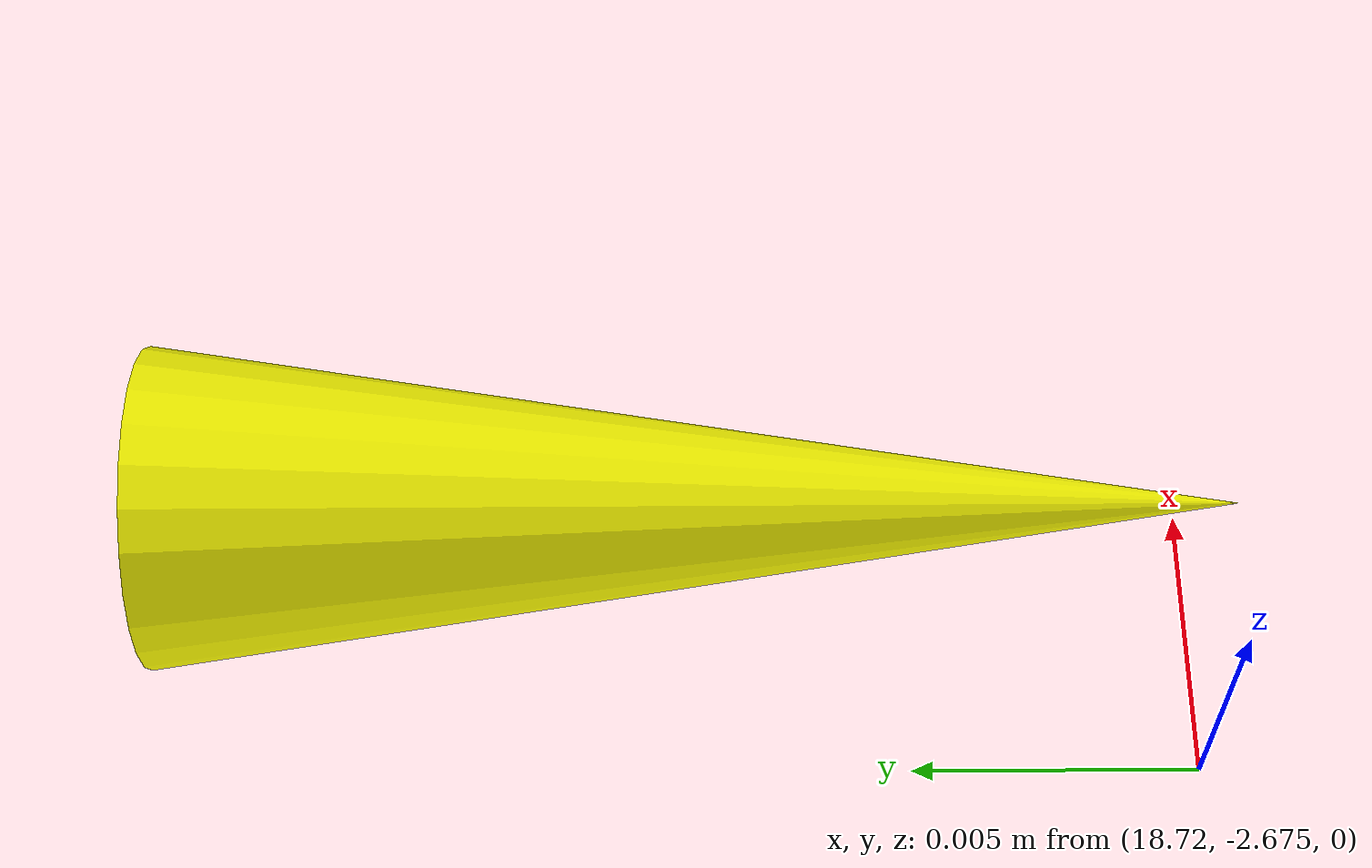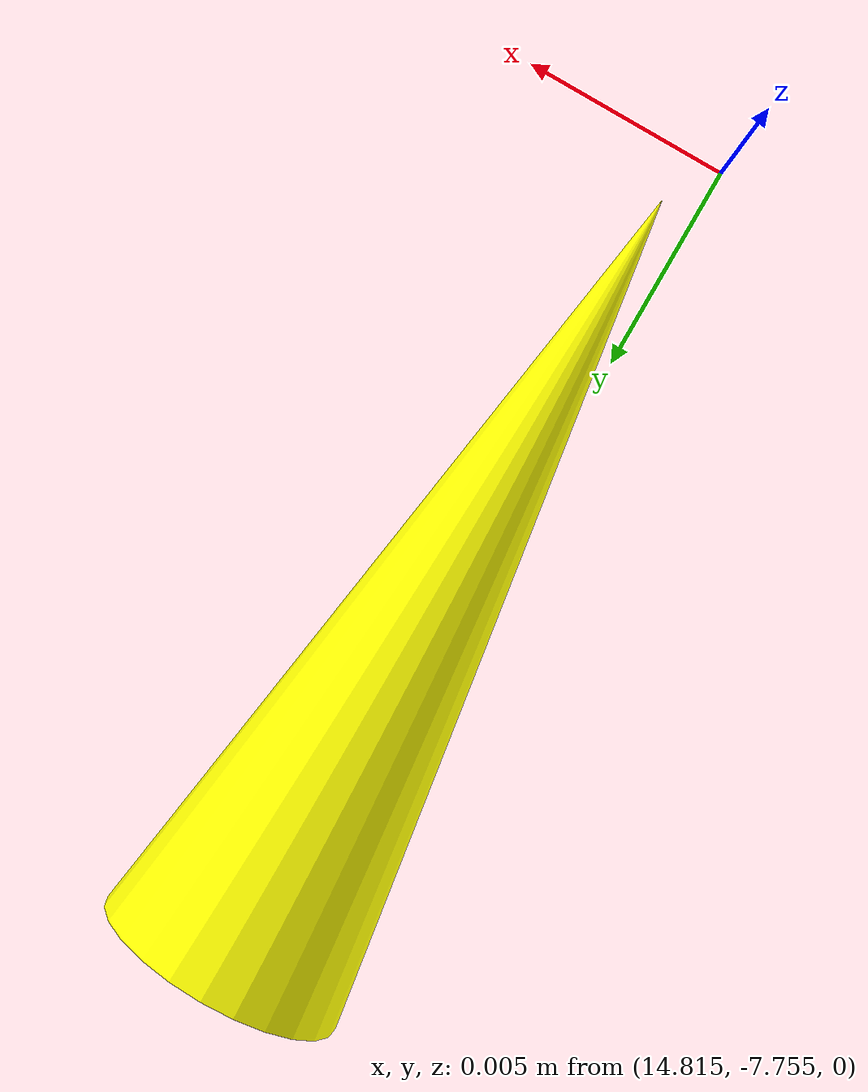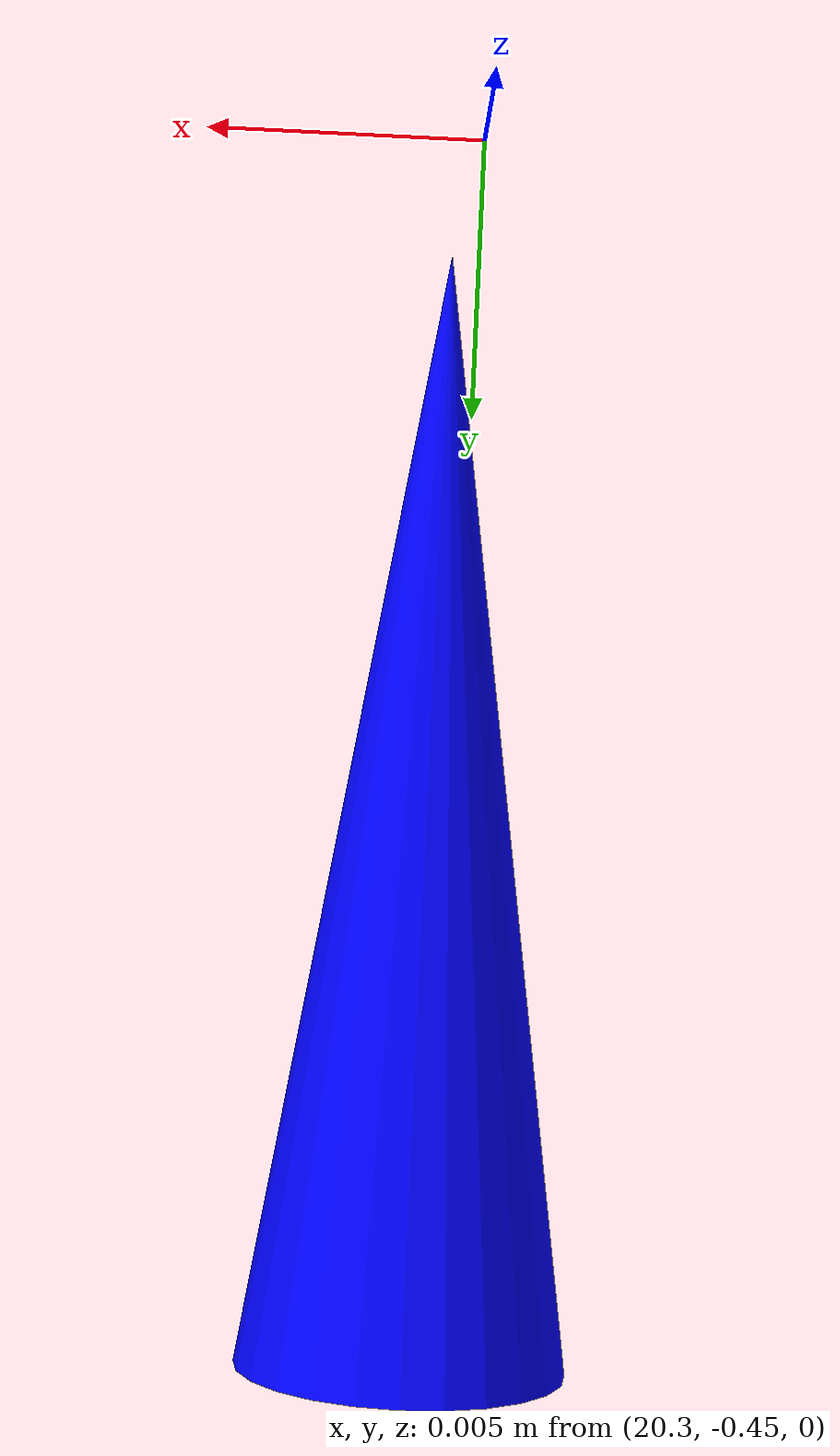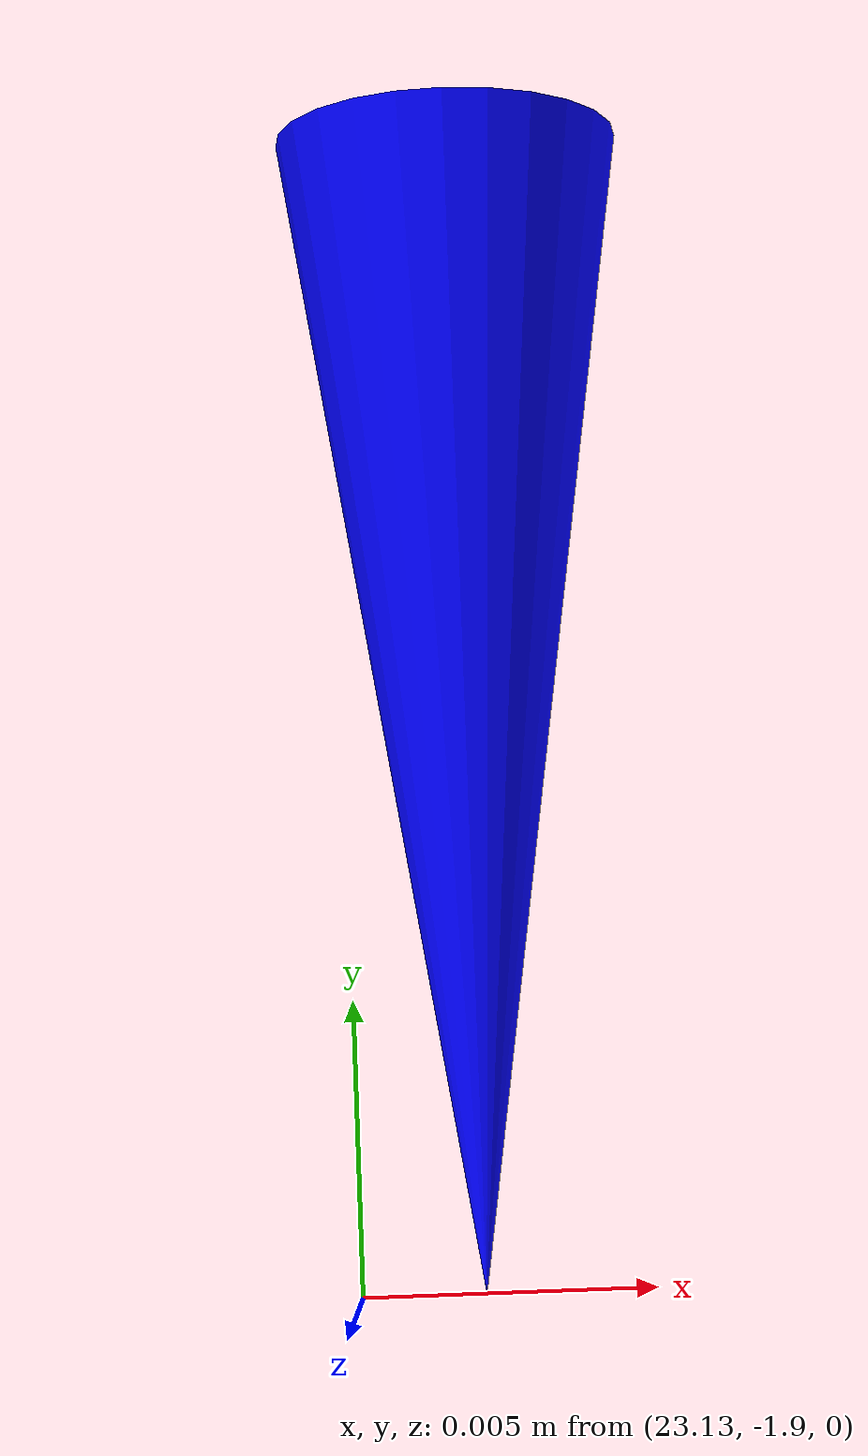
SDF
<?xml version="1.0"?>
  <sdf version='1.9'>
     <model name='cone_0'>
      <link name='cone_0_link'>
        <inertial>
			<mass>0</mass>
			<inertia>
			<ixx>0.166667</ixx>
			<ixy>0</ixy>
			<ixz>0</ixz>
			<iyy>0.166667</iyy>
			<iyz>0</iyz>
			<izz>0.166667</izz>
			</inertia>
		</inertial>
        <collision name='cone_0_collision'>
          <geometry>
            <mesh>
              <uri>/models/cone/meshes/cone.stl</uri>
              <scale>0.001 0.001 0.001</scale>
            </mesh>
          </geometry>
        </collision>
        <visual name='cone_0_visual'>
          <geometry>
            <mesh>
              <uri>/models/cone/meshes/cone.stl</uri>
              <scale>0.001 0.001 0.001</scale>
            </mesh>
          </geometry>
          <material>
            <ambient>1 1 0 1</ambient>
            <diffuse>1 1 0 1</diffuse>
            <specular>1 1 0 1</specular>
          </material>
        </visual>

        <enable_wind>false</enable_wind>
      </link>
      <pose>5.083841909114041 -6.596079596214825 0.0 1.57 0 0</pose>
      <static>true</static>
      </model>

     <model name='cone_1'>
      <link name='cone_1_link'>
        <inertial>
			<mass>0</mass>
			<inertia>
			<ixx>0.166667</ixx>
			<ixy>0</ixy>
			<ixz>0</ixz>
			<iyy>0.166667</iyy>
			<iyz>0</iyz>
			<izz>0.166667</izz>
			</inertia>
		</inertial>
        <collision name='cone_1_collision'>
          <geometry>
            <mesh>
              <uri>/models/cone/meshes/cone.stl</uri>
              <scale>0.001 0.001 0.001</scale>
            </mesh>
          </geometry>
        </collision>
        <visual name='cone_1_visual'>
          <geometry>
            <mesh>
              <uri>/models/cone/meshes/cone.stl</uri>
              <scale>0.001 0.001 0.001</scale>
            </mesh>
          </geometry>
          <material>
            <ambient>1 1 0 1</ambient>
            <diffuse>1 1 0 1</diffuse>
            <specular>1 1 0 1</specular>
          </material>
        </visual>

        <enable_wind>false</enable_wind>
      </link>
      <pose>6.2869284045135165 -6.598765560322338 0.0 1.57 0 0</pose>
      <static>true</static>
      </model>

     <model name='cone_2'>
      <link name='cone_2_link'>
        <inertial>
			<mass>0</mass>
			<inertia>
			<ixx>0.166667</ixx>
			<ixy>0</ixy>
			<ixz>0</ixz>
			<iyy>0.166667</iyy>
			<iyz>0</iyz>
			<izz>0.166667</izz>
			</inertia>
		</inertial>
        <collision name='cone_2_collision'>
          <geometry>
            <mesh>
              <uri>/models/cone/meshes/cone.stl</uri>
              <scale>0.001 0.001 0.001</scale>
            </mesh>
          </geometry>
        </collision>
        <visual name='cone_2_visual'>
          <geometry>
            <mesh>
              <uri>/models/cone/meshes/cone.stl</uri>
              <scale>0.001 0.001 0.001</scale>
            </mesh>
          </geometry>
          <material>
            <ambient>1 1 0 1</ambient>
            <diffuse>1 1 0 1</diffuse>
            <specular>1 1 0 1</specular>
          </material>
        </visual>

        <enable_wind>false</enable_wind>
      </link>
      <pose>7.3307375800048495 -6.584115573101574 0.0 1.57 0 0</pose>
      <static>true</static>
      </model>

     <model name='cone_3'>
      <link name='cone_3_link'>
        <inertial>
			<mass>0</mass>
			<inertia>
			<ixx>0.166667</ixx>
			<ixy>0</ixy>
			<ixz>0</ixz>
			<iyy>0.166667</iyy>
			<iyz>0</iyz>
			<izz>0.166667</izz>
			</inertia>
		</inertial>
        <collision name='cone_3_collision'>
          <geometry>
            <mesh>
              <uri>/models/cone/meshes/cone.stl</uri>
              <scale>0.001 0.001 0.001</scale>
            </mesh>
          </geometry>
        </collision>
        <visual name='cone_3_visual'>
          <geometry>
            <mesh>
              <uri>/models/cone/meshes/cone.stl</uri>
              <scale>0.001 0.001 0.001</scale>
            </mesh>
          </geometry>
          <material>
            <ambient>1 1 0 1</ambient>
            <diffuse>1 1 0 1</diffuse>
            <specular>1 1 0 1</specular>
          </material>
        </visual>

        <enable_wind>false</enable_wind>
      </link>
      <pose>8.517317761126677 -6.663014599018627 0.0 1.57 0 0</pose>
      <static>true</static>
      </model>

     <model name='cone_4'>
      <link name='cone_4_link'>
        <inertial>
			<mass>0</mass>
			<inertia>
			<ixx>0.166667</ixx>
			<ixy>0</ixy>
			<ixz>0</ixz>
			<iyy>0.166667</iyy>
			<iyz>0</iyz>
			<izz>0.166667</izz>
			</inertia>
		</inertial>
        <collision name='cone_4_collision'>
          <geometry>
            <mesh>
              <uri>/models/cone/meshes/cone.stl</uri>
              <scale>0.001 0.001 0.001</scale>
            </mesh>
          </geometry>
        </collision>
        <visual name='cone_4_visual'>
          <geometry>
            <mesh>
              <uri>/models/cone/meshes/cone.stl</uri>
              <scale>0.001 0.001 0.001</scale>
            </mesh>
          </geometry>
          <material>
            <ambient>1 1 0 1</ambient>
            <diffuse>1 1 0 1</diffuse>
            <specular>1 1 0 1</specular>
          </material>
        </visual>

        <enable_wind>false</enable_wind>
      </link>
      <pose>9.425399769488493 -6.678046115570599 0.0 1.57 0 0</pose>
      <static>true</static>
      </model>

     <model name='cone_5'>
      <link name='cone_5_link'>
        <inertial>
			<mass>0</mass>
			<inertia>
			<ixx>0.166667</ixx>
			<ixy>0</ixy>
			<ixz>0</ixz>
			<iyy>0.166667</iyy>
			<iyz>0</iyz>
			<izz>0.166667</izz>
			</inertia>
		</inertial>
        <collision name='cone_5_collision'>
          <geometry>
            <mesh>
              <uri>/models/cone/meshes/cone.stl</uri>
              <scale>0.001 0.001 0.001</scale>
            </mesh>
          </geometry>
        </collision>
        <visual name='cone_5_visual'>
          <geometry>
            <mesh>
              <uri>/models/cone/meshes/cone.stl</uri>
              <scale>0.001 0.001 0.001</scale>
            </mesh>
          </geometry>
          <material>
            <ambient>1 1 0 1</ambient>
            <diffuse>1 1 0 1</diffuse>
            <specular>1 1 0 1</specular>
          </material>
        </visual>

        <enable_wind>false</enable_wind>
      </link>
      <pose>11.0356006514465 -6.865875610046917 0.0 1.57 0 0</pose>
      <static>true</static>
      </model>

     <model name='cone_6'>
      <link name='cone_6_link'>
        <inertial>
			<mass>0</mass>
			<inertia>
			<ixx>0.166667</ixx>
			<ixy>0</ixy>
			<ixz>0</ixz>
			<iyy>0.166667</iyy>
			<iyz>0</iyz>
			<izz>0.166667</izz>
			</inertia>
		</inertial>
        <collision name='cone_6_collision'>
          <geometry>
            <mesh>
              <uri>/models/cone/meshes/cone.stl</uri>
              <scale>0.001 0.001 0.001</scale>
            </mesh>
          </geometry>
        </collision>
        <visual name='cone_6_visual'>
          <geometry>
            <mesh>
              <uri>/models/cone/meshes/cone.stl</uri>
              <scale>0.001 0.001 0.001</scale>
            </mesh>
          </geometry>
          <material>
            <ambient>1 1 0 1</ambient>
            <diffuse>1 1 0 1</diffuse>
            <specular>1 1 0 1</specular>
          </material>
        </visual>

        <enable_wind>false</enable_wind>
      </link>
      <pose>12.857014168444792 -7.232714095049435 0.0 1.57 0 0</pose>
      <static>true</static>
      </model>

     <model name='cone_7'>
      <link name='cone_7_link'>
        <inertial>
			<mass>0</mass>
			<inertia>
			<ixx>0.166667</ixx>
			<ixy>0</ixy>
			<ixz>0</ixz>
			<iyy>0.166667</iyy>
			<iyz>0</iyz>
			<izz>0.166667</izz>
			</inertia>
		</inertial>
        <collision name='cone_7_collision'>
          <geometry>
            <mesh>
              <uri>/models/cone/meshes/cone.stl</uri>
              <scale>0.001 0.001 0.001</scale>
            </mesh>
          </geometry>
        </collision>
        <visual name='cone_7_visual'>
          <geometry>
            <mesh>
              <uri>/models/cone/meshes/cone.stl</uri>
              <scale>0.001 0.001 0.001</scale>
            </mesh>
          </geometry>
          <material>
            <ambient>1 1 0 1</ambient>
            <diffuse>1 1 0 1</diffuse>
            <specular>1 1 0 1</specular>
          </material>
        </visual>

        <enable_wind>false</enable_wind>
      </link>
      <pose>14.815833557788054 -7.7338280909591255 0.0 1.57 0 0</pose>
      <static>true</static>
      </model>

     <model name='cone_8'>
      <link name='cone_8_link'>
        <inertial>
			<mass>0</mass>
			<inertia>
			<ixx>0.166667</ixx>
			<ixy>0</ixy>
			<ixz>0</ixz>
			<iyy>0.166667</iyy>
			<iyz>0</iyz>
			<izz>0.166667</izz>
			</inertia>
		</inertial>
        <collision name='cone_8_collision'>
          <geometry>
            <mesh>
              <uri>/models/cone/meshes/cone.stl</uri>
              <scale>0.001 0.001 0.001</scale>
            </mesh>
          </geometry>
        </collision>
        <visual name='cone_8_visual'>
          <geometry>
            <mesh>
              <uri>/models/cone/meshes/cone.stl</uri>
              <scale>0.001 0.001 0.001</scale>
            </mesh>
          </geometry>
          <material>
            <ambient>1 1 0 1</ambient>
            <diffuse>1 1 0 1</diffuse>
            <specular>1 1 0 1</specular>
          </material>
        </visual>

        <enable_wind>false</enable_wind>
      </link>
      <pose>16.570437897387663 -7.622138091259533 0.0 1.57 0 0</pose>
      <static>true</static>
      </model>

     <model name='cone_9'>
      <link name='cone_9_link'>
        <inertial>
			<mass>0</mass>
			<inertia>
			<ixx>0.166667</ixx>
			<ixy>0</ixy>
			<ixz>0</ixz>
			<iyy>0.166667</iyy>
			<iyz>0</iyz>
			<izz>0.166667</izz>
			</inertia>
		</inertial>
        <collision name='cone_9_collision'>
          <geometry>
            <mesh>
              <uri>/models/cone/meshes/cone.stl</uri>
              <scale>0.001 0.001 0.001</scale>
            </mesh>
          </geometry>
        </collision>
        <visual name='cone_9_visual'>
          <geometry>
            <mesh>
              <uri>/models/cone/meshes/cone.stl</uri>
              <scale>0.001 0.001 0.001</scale>
            </mesh>
          </geometry>
          <material>
            <ambient>1 1 0 1</ambient>
            <diffuse>1 1 0 1</diffuse>
            <specular>1 1 0 1</specular>
          </material>
        </visual>

        <enable_wind>false</enable_wind>
      </link>
      <pose>18.128659714404264 -7.356821589999729 0.0 1.57 0 0</pose>
      <static>true</static>
      </model>

     <model name='cone_10'>
      <link name='cone_10_link'>
        <inertial>
			<mass>0</mass>
			<inertia>
			<ixx>0.166667</ixx>
			<ixy>0</ixy>
			<ixz>0</ixz>
			<iyy>0.166667</iyy>
			<iyz>0</iyz>
			<izz>0.166667</izz>
			</inertia>
		</inertial>
        <collision name='cone_10_collision'>
          <geometry>
            <mesh>
              <uri>/models/cone/meshes/cone.stl</uri>
              <scale>0.001 0.001 0.001</scale>
            </mesh>
          </geometry>
        </collision>
        <visual name='cone_10_visual'>
          <geometry>
            <mesh>
              <uri>/models/cone/meshes/cone.stl</uri>
              <scale>0.001 0.001 0.001</scale>
            </mesh>
          </geometry>
          <material>
            <ambient>1 1 0 1</ambient>
            <diffuse>1 1 0 1</diffuse>
            <specular>1 1 0 1</specular>
          </material>
        </visual>

        <enable_wind>false</enable_wind>
      </link>
      <pose>19.756761063281218 -6.885007568531567 0.0 1.57 0 0</pose>
      <static>true</static>
      </model>

     <model name='cone_11'>
      <link name='cone_11_link'>
        <inertial>
			<mass>0</mass>
			<inertia>
			<ixx>0.166667</ixx>
			<ixy>0</ixy>
			<ixz>0</ixz>
			<iyy>0.166667</iyy>
			<iyz>0</iyz>
			<izz>0.166667</izz>
			</inertia>
		</inertial>
        <collision name='cone_11_collision'>
          <geometry>
            <mesh>
              <uri>/models/cone/meshes/cone.stl</uri>
              <scale>0.001 0.001 0.001</scale>
            </mesh>
          </geometry>
        </collision>
        <visual name='cone_11_visual'>
          <geometry>
            <mesh>
              <uri>/models/cone/meshes/cone.stl</uri>
              <scale>0.001 0.001 0.001</scale>
            </mesh>
          </geometry>
          <material>
            <ambient>1 1 0 1</ambient>
            <diffuse>1 1 0 1</diffuse>
            <specular>1 1 0 1</specular>
          </material>
        </visual>

        <enable_wind>false</enable_wind>
      </link>
      <pose>21.191152085009733 -6.198311098747784 0.0 1.57 0 0</pose>
      <static>true</static>
      </model>

     <model name='cone_12'>
      <link name='cone_12_link'>
        <inertial>
			<mass>0</mass>
			<inertia>
			<ixx>0.166667</ixx>
			<ixy>0</ixy>
			<ixz>0</ixz>
			<iyy>0.166667</iyy>
			<iyz>0</iyz>
			<izz>0.166667</izz>
			</inertia>
		</inertial>
        <collision name='cone_12_collision'>
          <geometry>
            <mesh>
              <uri>/models/cone/meshes/cone.stl</uri>
              <scale>0.001 0.001 0.001</scale>
            </mesh>
          </geometry>
        </collision>
        <visual name='cone_12_visual'>
          <geometry>
            <mesh>
              <uri>/models/cone/meshes/cone.stl</uri>
              <scale>0.001 0.001 0.001</scale>
            </mesh>
          </geometry>
          <material>
            <ambient>1 1 0 1</ambient>
            <diffuse>1 1 0 1</diffuse>
            <specular>1 1 0 1</specular>
          </material>
        </visual>

        <enable_wind>false</enable_wind>
      </link>
      <pose>22.31523465031735 -5.181595095329815 0.0 1.57 0 0</pose>
      <static>true</static>
      </model>

     <model name='cone_13'>
      <link name='cone_13_link'>
        <inertial>
			<mass>0</mass>
			<inertia>
			<ixx>0.166667</ixx>
			<ixy>0</ixy>
			<ixz>0</ixz>
			<iyy>0.166667</iyy>
			<iyz>0</iyz>
			<izz>0.166667</izz>
			</inertia>
		</inertial>
        <collision name='cone_13_collision'>
          <geometry>
            <mesh>
              <uri>/models/cone/meshes/cone.stl</uri>
              <scale>0.001 0.001 0.001</scale>
            </mesh>
          </geometry>
        </collision>
        <visual name='cone_13_visual'>
          <geometry>
            <mesh>
              <uri>/models/cone/meshes/cone.stl</uri>
              <scale>0.001 0.001 0.001</scale>
            </mesh>
          </geometry>
          <material>
            <ambient>1 1 0 1</ambient>
            <diffuse>1 1 0 1</diffuse>
            <specular>1 1 0 1</specular>
          </material>
        </visual>

        <enable_wind>false</enable_wind>
      </link>
      <pose>22.365138519946257 -4.2171731077962455 0.0 1.57 0 0</pose>
      <static>true</static>
      </model>

     <model name='cone_14'>
      <link name='cone_14_link'>
        <inertial>
			<mass>0</mass>
			<inertia>
			<ixx>0.166667</ixx>
			<ixy>0</ixy>
			<ixz>0</ixz>
			<iyy>0.166667</iyy>
			<iyz>0</iyz>
			<izz>0.166667</izz>
			</inertia>
		</inertial>
        <collision name='cone_14_collision'>
          <geometry>
            <mesh>
              <uri>/models/cone/meshes/cone.stl</uri>
              <scale>0.001 0.001 0.001</scale>
            </mesh>
          </geometry>
        </collision>
        <visual name='cone_14_visual'>
          <geometry>
            <mesh>
              <uri>/models/cone/meshes/cone.stl</uri>
              <scale>0.001 0.001 0.001</scale>
            </mesh>
          </geometry>
          <material>
            <ambient>1 1 0 1</ambient>
            <diffuse>1 1 0 1</diffuse>
            <specular>1 1 0 1</specular>
          </material>
        </visual>

        <enable_wind>false</enable_wind>
      </link>
      <pose>21.691356171313444 -3.0315461241536674 0.0 1.57 0 0</pose>
      <static>true</static>
      </model>

     <model name='cone_15'>
      <link name='cone_15_link'>
        <inertial>
			<mass>0</mass>
			<inertia>
			<ixx>0.166667</ixx>
			<ixy>0</ixy>
			<ixz>0</ixz>
			<iyy>0.166667</iyy>
			<iyz>0</iyz>
			<izz>0.166667</izz>
			</inertia>
		</inertial>
        <collision name='cone_15_collision'>
          <geometry>
            <mesh>
              <uri>/models/cone/meshes/cone.stl</uri>
              <scale>0.001 0.001 0.001</scale>
            </mesh>
          </geometry>
        </collision>
        <visual name='cone_15_visual'>
          <geometry>
            <mesh>
              <uri>/models/cone/meshes/cone.stl</uri>
              <scale>0.001 0.001 0.001</scale>
            </mesh>
          </geometry>
          <material>
            <ambient>1 1 0 1</ambient>
            <diffuse>1 1 0 1</diffuse>
            <specular>1 1 0 1</specular>
          </material>
        </visual>

        <enable_wind>false</enable_wind>
      </link>
      <pose>19.986562241259733 -2.4707508169942436 0.0 1.57 0 0</pose>
      <static>true</static>
      </model>

     <model name='cone_16'>
      <link name='cone_16_link'>
        <inertial>
			<mass>0</mass>
			<inertia>
			<ixx>0.166667</ixx>
			<ixy>0</ixy>
			<ixz>0</ixz>
			<iyy>0.166667</iyy>
			<iyz>0</iyz>
			<izz>0.166667</izz>
			</inertia>
		</inertial>
        <collision name='cone_16_collision'>
          <geometry>
            <mesh>
              <uri>/models/cone/meshes/cone.stl</uri>
              <scale>0.001 0.001 0.001</scale>
            </mesh>
          </geometry>
        </collision>
        <visual name='cone_16_visual'>
          <geometry>
            <mesh>
              <uri>/models/cone/meshes/cone.stl</uri>
              <scale>0.001 0.001 0.001</scale>
            </mesh>
          </geometry>
          <material>
            <ambient>1 1 0 1</ambient>
            <diffuse>1 1 0 1</diffuse>
            <specular>1 1 0 1</specular>
          </material>
        </visual>

        <enable_wind>false</enable_wind>
      </link>
      <pose>18.725324143115202 -2.6562624060445366 0.0 1.57 0 0</pose>
      <static>true</static>
      </model>

     <model name='cone_17'>
      <link name='cone_17_link'>
        <inertial>
			<mass>0</mass>
			<inertia>
			<ixx>0.166667</ixx>
			<ixy>0</ixy>
			<ixz>0</ixz>
			<iyy>0.166667</iyy>
			<iyz>0</iyz>
			<izz>0.166667</izz>
			</inertia>
		</inertial>
        <collision name='cone_17_collision'>
          <geometry>
            <mesh>
              <uri>/models/cone/meshes/cone.stl</uri>
              <scale>0.001 0.001 0.001</scale>
            </mesh>
          </geometry>
        </collision>
        <visual name='cone_17_visual'>
          <geometry>
            <mesh>
              <uri>/models/cone/meshes/cone.stl</uri>
              <scale>0.001 0.001 0.001</scale>
            </mesh>
          </geometry>
          <material>
            <ambient>1 1 0 1</ambient>
            <diffuse>1 1 0 1</diffuse>
            <specular>1 1 0 1</specular>
          </material>
        </visual>

        <enable_wind>false</enable_wind>
      </link>
      <pose>17.305813301745573 -2.9979462706380424 0.0 1.57 0 0</pose>
      <static>true</static>
      </model>

     <model name='cone_18'>
      <link name='cone_18_link'>
        <inertial>
			<mass>0</mass>
			<inertia>
			<ixx>0.166667</ixx>
			<ixy>0</ixy>
			<ixz>0</ixz>
			<iyy>0.166667</iyy>
			<iyz>0</iyz>
			<izz>0.166667</izz>
			</inertia>
		</inertial>
        <collision name='cone_18_collision'>
          <geometry>
            <mesh>
              <uri>/models/cone/meshes/cone.stl</uri>
              <scale>0.001 0.001 0.001</scale>
            </mesh>
          </geometry>
        </collision>
        <visual name='cone_18_visual'>
          <geometry>
            <mesh>
              <uri>/models/cone/meshes/cone.stl</uri>
              <scale>0.001 0.001 0.001</scale>
            </mesh>
          </geometry>
          <material>
            <ambient>1 1 0 1</ambient>
            <diffuse>1 1 0 1</diffuse>
            <specular>1 1 0 1</specular>
          </material>
        </visual>

        <enable_wind>false</enable_wind>
      </link>
      <pose>16.028248299304167 -3.435146816902691 0.0 1.57 0 0</pose>
      <static>true</static>
      </model>

     <model name='cone_19'>
      <link name='cone_19_link'>
        <inertial>
			<mass>0</mass>
			<inertia>
			<ixx>0.166667</ixx>
			<ixy>0</ixy>
			<ixz>0</ixz>
			<iyy>0.166667</iyy>
			<iyz>0</iyz>
			<izz>0.166667</izz>
			</inertia>
		</inertial>
        <collision name='cone_19_collision'>
          <geometry>
            <mesh>
              <uri>/models/cone/meshes/cone.stl</uri>
              <scale>0.001 0.001 0.001</scale>
            </mesh>
          </geometry>
        </collision>
        <visual name='cone_19_visual'>
          <geometry>
            <mesh>
              <uri>/models/cone/meshes/cone.stl</uri>
              <scale>0.001 0.001 0.001</scale>
            </mesh>
          </geometry>
          <material>
            <ambient>1 1 0 1</ambient>
            <diffuse>1 1 0 1</diffuse>
            <specular>1 1 0 1</specular>
          </material>
        </visual>

        <enable_wind>false</enable_wind>
      </link>
      <pose>14.642330635729948 -4.148195990257793 0.0 1.57 0 0</pose>
      <static>true</static>
      </model>

     <model name='cone_20'>
      <link name='cone_20_link'>
        <inertial>
			<mass>0</mass>
			<inertia>
			<ixx>0.166667</ixx>
			<ixy>0</ixy>
			<ixz>0</ixz>
			<iyy>0.166667</iyy>
			<iyz>0</iyz>
			<izz>0.166667</izz>
			</inertia>
		</inertial>
        <collision name='cone_20_collision'>
          <geometry>
            <mesh>
              <uri>/models/cone/meshes/cone.stl</uri>
              <scale>0.001 0.001 0.001</scale>
            </mesh>
          </geometry>
        </collision>
        <visual name='cone_20_visual'>
          <geometry>
            <mesh>
              <uri>/models/cone/meshes/cone.stl</uri>
              <scale>0.001 0.001 0.001</scale>
            </mesh>
          </geometry>
          <material>
            <ambient>1 1 0 1</ambient>
            <diffuse>1 1 0 1</diffuse>
            <specular>1 1 0 1</specular>
          </material>
        </visual>

        <enable_wind>false</enable_wind>
      </link>
      <pose>13.25863407963864 -4.577085026436382 0.0 1.57 0 0</pose>
      <static>true</static>
      </model>

     <model name='cone_21'>
      <link name='cone_21_link'>
        <inertial>
			<mass>0</mass>
			<inertia>
			<ixx>0.166667</ixx>
			<ixy>0</ixy>
			<ixz>0</ixz>
			<iyy>0.166667</iyy>
			<iyz>0</iyz>
			<izz>0.166667</izz>
			</inertia>
		</inertial>
        <collision name='cone_21_collision'>
          <geometry>
            <mesh>
              <uri>/models/cone/meshes/cone.stl</uri>
              <scale>0.001 0.001 0.001</scale>
            </mesh>
          </geometry>
        </collision>
        <visual name='cone_21_visual'>
          <geometry>
            <mesh>
              <uri>/models/cone/meshes/cone.stl</uri>
              <scale>0.001 0.001 0.001</scale>
            </mesh>
          </geometry>
          <material>
            <ambient>1 1 0 1</ambient>
            <diffuse>1 1 0 1</diffuse>
            <specular>1 1 0 1</specular>
          </material>
        </visual>

        <enable_wind>false</enable_wind>
      </link>
      <pose>12.139428604785124 -4.777493008308941 0.0 1.57 0 0</pose>
      <static>true</static>
      </model>

     <model name='cone_22'>
      <link name='cone_22_link'>
        <inertial>
			<mass>0</mass>
			<inertia>
			<ixx>0.166667</ixx>
			<ixy>0</ixy>
			<ixz>0</ixz>
			<iyy>0.166667</iyy>
			<iyz>0</iyz>
			<izz>0.166667</izz>
			</inertia>
		</inertial>
        <collision name='cone_22_collision'>
          <geometry>
            <mesh>
              <uri>/models/cone/meshes/cone.stl</uri>
              <scale>0.001 0.001 0.001</scale>
            </mesh>
          </geometry>
        </collision>
        <visual name='cone_22_visual'>
          <geometry>
            <mesh>
              <uri>/models/cone/meshes/cone.stl</uri>
              <scale>0.001 0.001 0.001</scale>
            </mesh>
          </geometry>
          <material>
            <ambient>1 1 0 1</ambient>
            <diffuse>1 1 0 1</diffuse>
            <specular>1 1 0 1</specular>
          </material>
        </visual>

        <enable_wind>false</enable_wind>
      </link>
      <pose>10.896600235644499 -4.560081013374859 0.0 1.57 0 0</pose>
      <static>true</static>
      </model>

     <model name='cone_23'>
      <link name='cone_23_link'>
        <inertial>
			<mass>0</mass>
			<inertia>
			<ixx>0.166667</ixx>
			<ixy>0</ixy>
			<ixz>0</ixz>
			<iyy>0.166667</iyy>
			<iyz>0</iyz>
			<izz>0.166667</izz>
			</inertia>
		</inertial>
        <collision name='cone_23_collision'>
          <geometry>
            <mesh>
              <uri>/models/cone/meshes/cone.stl</uri>
              <scale>0.001 0.001 0.001</scale>
            </mesh>
          </geometry>
        </collision>
        <visual name='cone_23_visual'>
          <geometry>
            <mesh>
              <uri>/models/cone/meshes/cone.stl</uri>
              <scale>0.001 0.001 0.001</scale>
            </mesh>
          </geometry>
          <material>
            <ambient>1 1 0 1</ambient>
            <diffuse>1 1 0 1</diffuse>
            <specular>1 1 0 1</specular>
          </material>
        </visual>

        <enable_wind>false</enable_wind>
      </link>
      <pose>9.48894881123654 -3.8427200400167045 0.0 1.57 0 0</pose>
      <static>true</static>
      </model>

     <model name='cone_24'>
      <link name='cone_24_link'>
        <inertial>
			<mass>0</mass>
			<inertia>
			<ixx>0.166667</ixx>
			<ixy>0</ixy>
			<ixz>0</ixz>
			<iyy>0.166667</iyy>
			<iyz>0</iyz>
			<izz>0.166667</izz>
			</inertia>
		</inertial>
        <collision name='cone_24_collision'>
          <geometry>
            <mesh>
              <uri>/models/cone/meshes/cone.stl</uri>
              <scale>0.001 0.001 0.001</scale>
            </mesh>
          </geometry>
        </collision>
        <visual name='cone_24_visual'>
          <geometry>
            <mesh>
              <uri>/models/cone/meshes/cone.stl</uri>
              <scale>0.001 0.001 0.001</scale>
            </mesh>
          </geometry>
          <material>
            <ambient>1 1 0 1</ambient>
            <diffuse>1 1 0 1</diffuse>
            <specular>1 1 0 1</specular>
          </material>
        </visual>

        <enable_wind>false</enable_wind>
      </link>
      <pose>8.133770931903044 -3.442943104439312 0.0 1.57 0 0</pose>
      <static>true</static>
      </model>

     <model name='cone_25'>
      <link name='cone_25_link'>
        <inertial>
			<mass>0</mass>
			<inertia>
			<ixx>0.166667</ixx>
			<ixy>0</ixy>
			<ixz>0</ixz>
			<iyy>0.166667</iyy>
			<iyz>0</iyz>
			<izz>0.166667</izz>
			</inertia>
		</inertial>
        <collision name='cone_25_collision'>
          <geometry>
            <mesh>
              <uri>/models/cone/meshes/cone.stl</uri>
              <scale>0.001 0.001 0.001</scale>
            </mesh>
          </geometry>
        </collision>
        <visual name='cone_25_visual'>
          <geometry>
            <mesh>
              <uri>/models/cone/meshes/cone.stl</uri>
              <scale>0.001 0.001 0.001</scale>
            </mesh>
          </geometry>
          <material>
            <ambient>1 1 0 1</ambient>
            <diffuse>1 1 0 1</diffuse>
            <specular>1 1 0 1</specular>
          </material>
        </visual>

        <enable_wind>false</enable_wind>
      </link>
      <pose>6.72853278035275 -2.885032185249859 0.0 1.57 0 0</pose>
      <static>true</static>
      </model>

     <model name='cone_26'>
      <link name='cone_26_link'>
        <inertial>
			<mass>0</mass>
			<inertia>
			<ixx>0.166667</ixx>
			<ixy>0</ixy>
			<ixz>0</ixz>
			<iyy>0.166667</iyy>
			<iyz>0</iyz>
			<izz>0.166667</izz>
			</inertia>
		</inertial>
        <collision name='cone_26_collision'>
          <geometry>
            <mesh>
              <uri>/models/cone/meshes/cone.stl</uri>
              <scale>0.001 0.001 0.001</scale>
            </mesh>
          </geometry>
        </collision>
        <visual name='cone_26_visual'>
          <geometry>
            <mesh>
              <uri>/models/cone/meshes/cone.stl</uri>
              <scale>0.001 0.001 0.001</scale>
            </mesh>
          </geometry>
          <material>
            <ambient>1 1 0 1</ambient>
            <diffuse>1 1 0 1</diffuse>
            <specular>1 1 0 1</specular>
          </material>
        </visual>

        <enable_wind>false</enable_wind>
      </link>
      <pose>5.089006890002408 -2.142495640450054 0.0 1.57 0 0</pose>
      <static>true</static>
      </model>

     <model name='cone_27'>
      <link name='cone_27_link'>
        <inertial>
			<mass>0</mass>
			<inertia>
			<ixx>0.166667</ixx>
			<ixy>0</ixy>
			<ixz>0</ixz>
			<iyy>0.166667</iyy>
			<iyz>0</iyz>
			<izz>0.166667</izz>
			</inertia>
		</inertial>
        <collision name='cone_27_collision'>
          <geometry>
            <mesh>
              <uri>/models/cone/meshes/cone.stl</uri>
              <scale>0.001 0.001 0.001</scale>
            </mesh>
          </geometry>
        </collision>
        <visual name='cone_27_visual'>
          <geometry>
            <mesh>
              <uri>/models/cone/meshes/cone.stl</uri>
              <scale>0.001 0.001 0.001</scale>
            </mesh>
          </geometry>
          <material>
            <ambient>1 1 0 1</ambient>
            <diffuse>1 1 0 1</diffuse>
            <specular>1 1 0 1</specular>
          </material>
        </visual>

        <enable_wind>false</enable_wind>
      </link>
      <pose>3.3193293497150327 -1.203063496285015 0.0 1.57 0 0</pose>
      <static>true</static>
      </model>

     <model name='cone_28'>
      <link name='cone_28_link'>
        <inertial>
			<mass>0</mass>
			<inertia>
			<ixx>0.166667</ixx>
			<ixy>0</ixy>
			<ixz>0</ixz>
			<iyy>0.166667</iyy>
			<iyz>0</iyz>
			<izz>0.166667</izz>
			</inertia>
		</inertial>
        <collision name='cone_28_collision'>
          <geometry>
            <mesh>
              <uri>/models/cone/meshes/cone.stl</uri>
              <scale>0.001 0.001 0.001</scale>
            </mesh>
          </geometry>
        </collision>
        <visual name='cone_28_visual'>
          <geometry>
            <mesh>
              <uri>/models/cone/meshes/cone.stl</uri>
              <scale>0.001 0.001 0.001</scale>
            </mesh>
          </geometry>
          <material>
            <ambient>1 1 0 1</ambient>
            <diffuse>1 1 0 1</diffuse>
            <specular>1 1 0 1</specular>
          </material>
        </visual>

        <enable_wind>false</enable_wind>
      </link>
      <pose>1.573376883212247 -0.0930972182088432 0.0 1.57 0 0</pose>
      <static>true</static>
      </model>

     <model name='cone_29'>
      <link name='cone_29_link'>
        <inertial>
			<mass>0</mass>
			<inertia>
			<ixx>0.166667</ixx>
			<ixy>0</ixy>
			<ixz>0</ixz>
			<iyy>0.166667</iyy>
			<iyz>0</iyz>
			<izz>0.166667</izz>
			</inertia>
		</inertial>
        <collision name='cone_29_collision'>
          <geometry>
            <mesh>
              <uri>/models/cone/meshes/cone.stl</uri>
              <scale>0.001 0.001 0.001</scale>
            </mesh>
          </geometry>
        </collision>
        <visual name='cone_29_visual'>
          <geometry>
            <mesh>
              <uri>/models/cone/meshes/cone.stl</uri>
              <scale>0.001 0.001 0.001</scale>
            </mesh>
          </geometry>
          <material>
            <ambient>1 1 0 1</ambient>
            <diffuse>1 1 0 1</diffuse>
            <specular>1 1 0 1</specular>
          </material>
        </visual>

        <enable_wind>false</enable_wind>
      </link>
      <pose>0.3173494231139804 0.9477825082010689 0.0 1.57 0 0</pose>
      <static>true</static>
      </model>

     <model name='cone_30'>
      <link name='cone_30_link'>
        <inertial>
			<mass>0</mass>
			<inertia>
			<ixx>0.166667</ixx>
			<ixy>0</ixy>
			<ixz>0</ixz>
			<iyy>0.166667</iyy>
			<iyz>0</iyz>
			<izz>0.166667</izz>
			</inertia>
		</inertial>
        <collision name='cone_30_collision'>
          <geometry>
            <mesh>
              <uri>/models/cone/meshes/cone.stl</uri>
              <scale>0.001 0.001 0.001</scale>
            </mesh>
          </geometry>
        </collision>
        <visual name='cone_30_visual'>
          <geometry>
            <mesh>
              <uri>/models/cone/meshes/cone.stl</uri>
              <scale>0.001 0.001 0.001</scale>
            </mesh>
          </geometry>
          <material>
            <ambient>1 1 0 1</ambient>
            <diffuse>1 1 0 1</diffuse>
            <specular>1 1 0 1</specular>
          </material>
        </visual>

        <enable_wind>false</enable_wind>
      </link>
      <pose>-0.9890613663757657 2.337016097373432 0.0 1.57 0 0</pose>
      <static>true</static>
      </model>

     <model name='cone_31'>
      <link name='cone_31_link'>
        <inertial>
			<mass>0</mass>
			<inertia>
			<ixx>0.166667</ixx>
			<ixy>0</ixy>
			<ixz>0</ixz>
			<iyy>0.166667</iyy>
			<iyz>0</iyz>
			<izz>0.166667</izz>
			</inertia>
		</inertial>
        <collision name='cone_31_collision'>
          <geometry>
            <mesh>
              <uri>/models/cone/meshes/cone.stl</uri>
              <scale>0.001 0.001 0.001</scale>
            </mesh>
          </geometry>
        </collision>
        <visual name='cone_31_visual'>
          <geometry>
            <mesh>
              <uri>/models/cone/meshes/cone.stl</uri>
              <scale>0.001 0.001 0.001</scale>
            </mesh>
          </geometry>
          <material>
            <ambient>1 1 0 1</ambient>
            <diffuse>1 1 0 1</diffuse>
            <specular>1 1 0 1</specular>
          </material>
        </visual>

        <enable_wind>false</enable_wind>
      </link>
      <pose>-1.9461131203735684 3.749796859092182 0.0 1.57 0 0</pose>
      <static>true</static>
      </model>

     <model name='cone_32'>
      <link name='cone_32_link'>
        <inertial>
			<mass>0</mass>
			<inertia>
			<ixx>0.166667</ixx>
			<ixy>0</ixy>
			<ixz>0</ixz>
			<iyy>0.166667</iyy>
			<iyz>0</iyz>
			<izz>0.166667</izz>
			</inertia>
		</inertial>
        <collision name='cone_32_collision'>
          <geometry>
            <mesh>
              <uri>/models/cone/meshes/cone.stl</uri>
              <scale>0.001 0.001 0.001</scale>
            </mesh>
          </geometry>
        </collision>
        <visual name='cone_32_visual'>
          <geometry>
            <mesh>
              <uri>/models/cone/meshes/cone.stl</uri>
              <scale>0.001 0.001 0.001</scale>
            </mesh>
          </geometry>
          <material>
            <ambient>1 1 0 1</ambient>
            <diffuse>1 1 0 1</diffuse>
            <specular>1 1 0 1</specular>
          </material>
        </visual>

        <enable_wind>false</enable_wind>
      </link>
      <pose>-2.5964188683594083 5.13265513545937 0.0 1.57 0 0</pose>
      <static>true</static>
      </model>

     <model name='cone_33'>
      <link name='cone_33_link'>
        <inertial>
			<mass>0</mass>
			<inertia>
			<ixx>0.166667</ixx>
			<ixy>0</ixy>
			<ixz>0</ixz>
			<iyy>0.166667</iyy>
			<iyz>0</iyz>
			<izz>0.166667</izz>
			</inertia>
		</inertial>
        <collision name='cone_33_collision'>
          <geometry>
            <mesh>
              <uri>/models/cone/meshes/cone.stl</uri>
              <scale>0.001 0.001 0.001</scale>
            </mesh>
          </geometry>
        </collision>
        <visual name='cone_33_visual'>
          <geometry>
            <mesh>
              <uri>/models/cone/meshes/cone.stl</uri>
              <scale>0.001 0.001 0.001</scale>
            </mesh>
          </geometry>
          <material>
            <ambient>1 1 0 1</ambient>
            <diffuse>1 1 0 1</diffuse>
            <specular>1 1 0 1</specular>
          </material>
        </visual>

        <enable_wind>false</enable_wind>
      </link>
      <pose>-2.4897294152344083 6.774883261985249 0.0 1.57 0 0</pose>
      <static>true</static>
      </model>

     <model name='cone_34'>
      <link name='cone_34_link'>
        <inertial>
			<mass>0</mass>
			<inertia>
			<ixx>0.166667</ixx>
			<ixy>0</ixy>
			<ixz>0</ixz>
			<iyy>0.166667</iyy>
			<iyz>0</iyz>
			<izz>0.166667</izz>
			</inertia>
		</inertial>
        <collision name='cone_34_collision'>
          <geometry>
            <mesh>
              <uri>/models/cone/meshes/cone.stl</uri>
              <scale>0.001 0.001 0.001</scale>
            </mesh>
          </geometry>
        </collision>
        <visual name='cone_34_visual'>
          <geometry>
            <mesh>
              <uri>/models/cone/meshes/cone.stl</uri>
              <scale>0.001 0.001 0.001</scale>
            </mesh>
          </geometry>
          <material>
            <ambient>1 1 0 1</ambient>
            <diffuse>1 1 0 1</diffuse>
            <specular>1 1 0 1</specular>
          </material>
        </visual>

        <enable_wind>false</enable_wind>
      </link>
      <pose>-2.0655775178039883 8.29559516078896 0.0 1.57 0 0</pose>
      <static>true</static>
      </model>

     <model name='cone_35'>
      <link name='cone_35_link'>
        <inertial>
			<mass>0</mass>
			<inertia>
			<ixx>0.166667</ixx>
			<ixy>0</ixy>
			<ixz>0</ixz>
			<iyy>0.166667</iyy>
			<iyz>0</iyz>
			<izz>0.166667</izz>
			</inertia>
		</inertial>
        <collision name='cone_35_collision'>
          <geometry>
            <mesh>
              <uri>/models/cone/meshes/cone.stl</uri>
              <scale>0.001 0.001 0.001</scale>
            </mesh>
          </geometry>
        </collision>
        <visual name='cone_35_visual'>
          <geometry>
            <mesh>
              <uri>/models/cone/meshes/cone.stl</uri>
              <scale>0.001 0.001 0.001</scale>
            </mesh>
          </geometry>
          <material>
            <ambient>1 1 0 1</ambient>
            <diffuse>1 1 0 1</diffuse>
            <specular>1 1 0 1</specular>
          </material>
        </visual>

        <enable_wind>false</enable_wind>
      </link>
      <pose>-1.7024917710388516 9.626074782676167 0.0 1.57 0 0</pose>
      <static>true</static>
      </model>

     <model name='cone_36'>
      <link name='cone_36_link'>
        <inertial>
			<mass>0</mass>
			<inertia>
			<ixx>0.166667</ixx>
			<ixy>0</ixy>
			<ixz>0</ixz>
			<iyy>0.166667</iyy>
			<iyz>0</iyz>
			<izz>0.166667</izz>
			</inertia>
		</inertial>
        <collision name='cone_36_collision'>
          <geometry>
            <mesh>
              <uri>/models/cone/meshes/cone.stl</uri>
              <scale>0.001 0.001 0.001</scale>
            </mesh>
          </geometry>
        </collision>
        <visual name='cone_36_visual'>
          <geometry>
            <mesh>
              <uri>/models/cone/meshes/cone.stl</uri>
              <scale>0.001 0.001 0.001</scale>
            </mesh>
          </geometry>
          <material>
            <ambient>1 1 0 1</ambient>
            <diffuse>1 1 0 1</diffuse>
            <specular>1 1 0 1</specular>
          </material>
        </visual>

        <enable_wind>false</enable_wind>
      </link>
      <pose>-1.3105526078308438 10.753558150596088 0.0 1.57 0 0</pose>
      <static>true</static>
      </model>

     <model name='cone_37'>
      <link name='cone_37_link'>
        <inertial>
			<mass>0</mass>
			<inertia>
			<ixx>0.166667</ixx>
			<ixy>0</ixy>
			<ixz>0</ixz>
			<iyy>0.166667</iyy>
			<iyz>0</iyz>
			<izz>0.166667</izz>
			</inertia>
		</inertial>
        <collision name='cone_37_collision'>
          <geometry>
            <mesh>
              <uri>/models/cone/meshes/cone.stl</uri>
              <scale>0.001 0.001 0.001</scale>
            </mesh>
          </geometry>
        </collision>
        <visual name='cone_37_visual'>
          <geometry>
            <mesh>
              <uri>/models/cone/meshes/cone.stl</uri>
              <scale>0.001 0.001 0.001</scale>
            </mesh>
          </geometry>
          <material>
            <ambient>1 1 0 1</ambient>
            <diffuse>1 1 0 1</diffuse>
            <specular>1 1 0 1</specular>
          </material>
        </visual>

        <enable_wind>false</enable_wind>
      </link>
      <pose>-0.6828706372345303 11.8598413384623 0.0 1.57 0 0</pose>
      <static>true</static>
      </model>

     <model name='cone_38'>
      <link name='cone_38_link'>
        <inertial>
			<mass>0</mass>
			<inertia>
			<ixx>0.166667</ixx>
			<ixy>0</ixy>
			<ixz>0</ixz>
			<iyy>0.166667</iyy>
			<iyz>0</iyz>
			<izz>0.166667</izz>
			</inertia>
		</inertial>
        <collision name='cone_38_collision'>
          <geometry>
            <mesh>
              <uri>/models/cone/meshes/cone.stl</uri>
              <scale>0.001 0.001 0.001</scale>
            </mesh>
          </geometry>
        </collision>
        <visual name='cone_38_visual'>
          <geometry>
            <mesh>
              <uri>/models/cone/meshes/cone.stl</uri>
              <scale>0.001 0.001 0.001</scale>
            </mesh>
          </geometry>
          <material>
            <ambient>1 1 0 1</ambient>
            <diffuse>1 1 0 1</diffuse>
            <specular>1 1 0 1</specular>
          </material>
        </visual>

        <enable_wind>false</enable_wind>
      </link>
      <pose>-0.26193071490176667 13.382267943686909 0.0 1.57 0 0</pose>
      <static>true</static>
      </model>

     <model name='cone_39'>
      <link name='cone_39_link'>
        <inertial>
			<mass>0</mass>
			<inertia>
			<ixx>0.166667</ixx>
			<ixy>0</ixy>
			<ixz>0</ixz>
			<iyy>0.166667</iyy>
			<iyz>0</iyz>
			<izz>0.166667</izz>
			</inertia>
		</inertial>
        <collision name='cone_39_collision'>
          <geometry>
            <mesh>
              <uri>/models/cone/meshes/cone.stl</uri>
              <scale>0.001 0.001 0.001</scale>
            </mesh>
          </geometry>
        </collision>
        <visual name='cone_39_visual'>
          <geometry>
            <mesh>
              <uri>/models/cone/meshes/cone.stl</uri>
              <scale>0.001 0.001 0.001</scale>
            </mesh>
          </geometry>
          <material>
            <ambient>1 1 0 1</ambient>
            <diffuse>1 1 0 1</diffuse>
            <specular>1 1 0 1</specular>
          </material>
        </visual>

        <enable_wind>false</enable_wind>
      </link>
      <pose>-1.0436387169922208 14.514712325400776 0.0 1.57 0 0</pose>
      <static>true</static>
      </model>

     <model name='cone_40'>
      <link name='cone_40_link'>
        <inertial>
			<mass>0</mass>
			<inertia>
			<ixx>0.166667</ixx>
			<ixy>0</ixy>
			<ixz>0</ixz>
			<iyy>0.166667</iyy>
			<iyz>0</iyz>
			<izz>0.166667</izz>
			</inertia>
		</inertial>
        <collision name='cone_40_collision'>
          <geometry>
            <mesh>
              <uri>/models/cone/meshes/cone.stl</uri>
              <scale>0.001 0.001 0.001</scale>
            </mesh>
          </geometry>
        </collision>
        <visual name='cone_40_visual'>
          <geometry>
            <mesh>
              <uri>/models/cone/meshes/cone.stl</uri>
              <scale>0.001 0.001 0.001</scale>
            </mesh>
          </geometry>
          <material>
            <ambient>1 1 0 1</ambient>
            <diffuse>1 1 0 1</diffuse>
            <specular>1 1 0 1</specular>
          </material>
        </visual>

        <enable_wind>false</enable_wind>
      </link>
      <pose>-2.08714104777225 14.92708872920937 0.0 1.57 0 0</pose>
      <static>true</static>
      </model>

     <model name='cone_41'>
      <link name='cone_41_link'>
        <inertial>
			<mass>0</mass>
			<inertia>
			<ixx>0.166667</ixx>
			<ixy>0</ixy>
			<ixz>0</ixz>
			<iyy>0.166667</iyy>
			<iyz>0</iyz>
			<izz>0.166667</izz>
			</inertia>
		</inertial>
        <collision name='cone_41_collision'>
          <geometry>
            <mesh>
              <uri>/models/cone/meshes/cone.stl</uri>
              <scale>0.001 0.001 0.001</scale>
            </mesh>
          </geometry>
        </collision>
        <visual name='cone_41_visual'>
          <geometry>
            <mesh>
              <uri>/models/cone/meshes/cone.stl</uri>
              <scale>0.001 0.001 0.001</scale>
            </mesh>
          </geometry>
          <material>
            <ambient>1 1 0 1</ambient>
            <diffuse>1 1 0 1</diffuse>
            <specular>1 1 0 1</specular>
          </material>
        </visual>

        <enable_wind>false</enable_wind>
      </link>
      <pose>-3.5501384842956876 14.696427336997456 0.0 1.57 0 0</pose>
      <static>true</static>
      </model>

     <model name='cone_42'>
      <link name='cone_42_link'>
        <inertial>
			<mass>0</mass>
			<inertia>
			<ixx>0.166667</ixx>
			<ixy>0</ixy>
			<ixz>0</ixz>
			<iyy>0.166667</iyy>
			<iyz>0</iyz>
			<izz>0.166667</izz>
			</inertia>
		</inertial>
        <collision name='cone_42_collision'>
          <geometry>
            <mesh>
              <uri>/models/cone/meshes/cone.stl</uri>
              <scale>0.001 0.001 0.001</scale>
            </mesh>
          </geometry>
        </collision>
        <visual name='cone_42_visual'>
          <geometry>
            <mesh>
              <uri>/models/cone/meshes/cone.stl</uri>
              <scale>0.001 0.001 0.001</scale>
            </mesh>
          </geometry>
          <material>
            <ambient>1 1 0 1</ambient>
            <diffuse>1 1 0 1</diffuse>
            <specular>1 1 0 1</specular>
          </material>
        </visual>

        <enable_wind>false</enable_wind>
      </link>
      <pose>-5.102440367993197 14.05944728023476 0.0 1.57 0 0</pose>
      <static>true</static>
      </model>

     <model name='cone_43'>
      <link name='cone_43_link'>
        <inertial>
			<mass>0</mass>
			<inertia>
			<ixx>0.166667</ixx>
			<ixy>0</ixy>
			<ixz>0</ixz>
			<iyy>0.166667</iyy>
			<iyz>0</iyz>
			<izz>0.166667</izz>
			</inertia>
		</inertial>
        <collision name='cone_43_collision'>
          <geometry>
            <mesh>
              <uri>/models/cone/meshes/cone.stl</uri>
              <scale>0.001 0.001 0.001</scale>
            </mesh>
          </geometry>
        </collision>
        <visual name='cone_43_visual'>
          <geometry>
            <mesh>
              <uri>/models/cone/meshes/cone.stl</uri>
              <scale>0.001 0.001 0.001</scale>
            </mesh>
          </geometry>
          <material>
            <ambient>1 1 0 1</ambient>
            <diffuse>1 1 0 1</diffuse>
            <specular>1 1 0 1</specular>
          </material>
        </visual>

        <enable_wind>false</enable_wind>
      </link>
      <pose>-6.4257769692505216 13.21424578792519 0.0 1.57 0 0</pose>
      <static>true</static>
      </model>

     <model name='cone_44'>
      <link name='cone_44_link'>
        <inertial>
			<mass>0</mass>
			<inertia>
			<ixx>0.166667</ixx>
			<ixy>0</ixy>
			<ixz>0</ixz>
			<iyy>0.166667</iyy>
			<iyz>0</iyz>
			<izz>0.166667</izz>
			</inertia>
		</inertial>
        <collision name='cone_44_collision'>
          <geometry>
            <mesh>
              <uri>/models/cone/meshes/cone.stl</uri>
              <scale>0.001 0.001 0.001</scale>
            </mesh>
          </geometry>
        </collision>
        <visual name='cone_44_visual'>
          <geometry>
            <mesh>
              <uri>/models/cone/meshes/cone.stl</uri>
              <scale>0.001 0.001 0.001</scale>
            </mesh>
          </geometry>
          <material>
            <ambient>1 1 0 1</ambient>
            <diffuse>1 1 0 1</diffuse>
            <specular>1 1 0 1</specular>
          </material>
        </visual>

        <enable_wind>false</enable_wind>
      </link>
      <pose>-7.6724505532348966 12.320706359214253 0.0 1.57 0 0</pose>
      <static>true</static>
      </model>

     <model name='cone_45'>
      <link name='cone_45_link'>
        <inertial>
			<mass>0</mass>
			<inertia>
			<ixx>0.166667</ixx>
			<ixy>0</ixy>
			<ixz>0</ixz>
			<iyy>0.166667</iyy>
			<iyz>0</iyz>
			<izz>0.166667</izz>
			</inertia>
		</inertial>
        <collision name='cone_45_collision'>
          <geometry>
            <mesh>
              <uri>/models/cone/meshes/cone.stl</uri>
              <scale>0.001 0.001 0.001</scale>
            </mesh>
          </geometry>
        </collision>
        <visual name='cone_45_visual'>
          <geometry>
            <mesh>
              <uri>/models/cone/meshes/cone.stl</uri>
              <scale>0.001 0.001 0.001</scale>
            </mesh>
          </geometry>
          <material>
            <ambient>1 1 0 1</ambient>
            <diffuse>1 1 0 1</diffuse>
            <specular>1 1 0 1</specular>
          </material>
        </visual>

        <enable_wind>false</enable_wind>
      </link>
      <pose>-8.823531638439974 11.475138655967182 0.0 1.57 0 0</pose>
      <static>true</static>
      </model>

     <model name='cone_46'>
      <link name='cone_46_link'>
        <inertial>
			<mass>0</mass>
			<inertia>
			<ixx>0.166667</ixx>
			<ixy>0</ixy>
			<ixz>0</ixz>
			<iyy>0.166667</iyy>
			<iyz>0</iyz>
			<izz>0.166667</izz>
			</inertia>
		</inertial>
        <collision name='cone_46_collision'>
          <geometry>
            <mesh>
              <uri>/models/cone/meshes/cone.stl</uri>
              <scale>0.001 0.001 0.001</scale>
            </mesh>
          </geometry>
        </collision>
        <visual name='cone_46_visual'>
          <geometry>
            <mesh>
              <uri>/models/cone/meshes/cone.stl</uri>
              <scale>0.001 0.001 0.001</scale>
            </mesh>
          </geometry>
          <material>
            <ambient>1 1 0 1</ambient>
            <diffuse>1 1 0 1</diffuse>
            <specular>1 1 0 1</specular>
          </material>
        </visual>

        <enable_wind>false</enable_wind>
      </link>
      <pose>-10.139441977795443 10.532406798667378 0.0 1.57 0 0</pose>
      <static>true</static>
      </model>

     <model name='cone_47'>
      <link name='cone_47_link'>
        <inertial>
			<mass>0</mass>
			<inertia>
			<ixx>0.166667</ixx>
			<ixy>0</ixy>
			<ixz>0</ixz>
			<iyy>0.166667</iyy>
			<iyz>0</iyz>
			<izz>0.166667</izz>
			</inertia>
		</inertial>
        <collision name='cone_47_collision'>
          <geometry>
            <mesh>
              <uri>/models/cone/meshes/cone.stl</uri>
              <scale>0.001 0.001 0.001</scale>
            </mesh>
          </geometry>
        </collision>
        <visual name='cone_47_visual'>
          <geometry>
            <mesh>
              <uri>/models/cone/meshes/cone.stl</uri>
              <scale>0.001 0.001 0.001</scale>
            </mesh>
          </geometry>
          <material>
            <ambient>1 1 0 1</ambient>
            <diffuse>1 1 0 1</diffuse>
            <specular>1 1 0 1</specular>
          </material>
        </visual>

        <enable_wind>false</enable_wind>
      </link>
      <pose>-11.41707850581058 9.566761962241596 0.0 1.57 0 0</pose>
      <static>true</static>
      </model>

     <model name='cone_48'>
      <link name='cone_48_link'>
        <inertial>
			<mass>0</mass>
			<inertia>
			<ixx>0.166667</ixx>
			<ixy>0</ixy>
			<ixz>0</ixz>
			<iyy>0.166667</iyy>
			<iyz>0</iyz>
			<izz>0.166667</izz>
			</inertia>
		</inertial>
        <collision name='cone_48_collision'>
          <geometry>
            <mesh>
              <uri>/models/cone/meshes/cone.stl</uri>
              <scale>0.001 0.001 0.001</scale>
            </mesh>
          </geometry>
        </collision>
        <visual name='cone_48_visual'>
          <geometry>
            <mesh>
              <uri>/models/cone/meshes/cone.stl</uri>
              <scale>0.001 0.001 0.001</scale>
            </mesh>
          </geometry>
          <material>
            <ambient>1 1 0 1</ambient>
            <diffuse>1 1 0 1</diffuse>
            <specular>1 1 0 1</specular>
          </material>
        </visual>

        <enable_wind>false</enable_wind>
      </link>
      <pose>-12.850298415478548 8.548464766807026 0.0 1.57 0 0</pose>
      <static>true</static>
      </model>

     <model name='cone_49'>
      <link name='cone_49_link'>
        <inertial>
			<mass>0</mass>
			<inertia>
			<ixx>0.166667</ixx>
			<ixy>0</ixy>
			<ixz>0</ixz>
			<iyy>0.166667</iyy>
			<iyz>0</iyz>
			<izz>0.166667</izz>
			</inertia>
		</inertial>
        <collision name='cone_49_collision'>
          <geometry>
            <mesh>
              <uri>/models/cone/meshes/cone.stl</uri>
              <scale>0.001 0.001 0.001</scale>
            </mesh>
          </geometry>
        </collision>
        <visual name='cone_49_visual'>
          <geometry>
            <mesh>
              <uri>/models/cone/meshes/cone.stl</uri>
              <scale>0.001 0.001 0.001</scale>
            </mesh>
          </geometry>
          <material>
            <ambient>1 1 0 1</ambient>
            <diffuse>1 1 0 1</diffuse>
            <specular>1 1 0 1</specular>
          </material>
        </visual>

        <enable_wind>false</enable_wind>
      </link>
      <pose>-14.233929168042025 7.443818084067768 0.0 1.57 0 0</pose>
      <static>true</static>
      </model>

     <model name='cone_50'>
      <link name='cone_50_link'>
        <inertial>
			<mass>0</mass>
			<inertia>
			<ixx>0.166667</ixx>
			<ixy>0</ixy>
			<ixz>0</ixz>
			<iyy>0.166667</iyy>
			<iyz>0</iyz>
			<izz>0.166667</izz>
			</inertia>
		</inertial>
        <collision name='cone_50_collision'>
          <geometry>
            <mesh>
              <uri>/models/cone/meshes/cone.stl</uri>
              <scale>0.001 0.001 0.001</scale>
            </mesh>
          </geometry>
        </collision>
        <visual name='cone_50_visual'>
          <geometry>
            <mesh>
              <uri>/models/cone/meshes/cone.stl</uri>
              <scale>0.001 0.001 0.001</scale>
            </mesh>
          </geometry>
          <material>
            <ambient>1 1 0 1</ambient>
            <diffuse>1 1 0 1</diffuse>
            <specular>1 1 0 1</specular>
          </material>
        </visual>

        <enable_wind>false</enable_wind>
      </link>
      <pose>-15.609589110668978 6.483412734336323 0.0 1.57 0 0</pose>
      <static>true</static>
      </model>

     <model name='cone_51'>
      <link name='cone_51_link'>
        <inertial>
			<mass>0</mass>
			<inertia>
			<ixx>0.166667</ixx>
			<ixy>0</ixy>
			<ixz>0</ixz>
			<iyy>0.166667</iyy>
			<iyz>0</iyz>
			<izz>0.166667</izz>
			</inertia>
		</inertial>
        <collision name='cone_51_collision'>
          <geometry>
            <mesh>
              <uri>/models/cone/meshes/cone.stl</uri>
              <scale>0.001 0.001 0.001</scale>
            </mesh>
          </geometry>
        </collision>
        <visual name='cone_51_visual'>
          <geometry>
            <mesh>
              <uri>/models/cone/meshes/cone.stl</uri>
              <scale>0.001 0.001 0.001</scale>
            </mesh>
          </geometry>
          <material>
            <ambient>1 1 0 1</ambient>
            <diffuse>1 1 0 1</diffuse>
            <specular>1 1 0 1</specular>
          </material>
        </visual>

        <enable_wind>false</enable_wind>
      </link>
      <pose>-17.096823226269564 5.212335578269428 0.0 1.57 0 0</pose>
      <static>true</static>
      </model>

     <model name='cone_52'>
      <link name='cone_52_link'>
        <inertial>
			<mass>0</mass>
			<inertia>
			<ixx>0.166667</ixx>
			<ixy>0</ixy>
			<ixz>0</ixz>
			<iyy>0.166667</iyy>
			<iyz>0</iyz>
			<izz>0.166667</izz>
			</inertia>
		</inertial>
        <collision name='cone_52_collision'>
          <geometry>
            <mesh>
              <uri>/models/cone/meshes/cone.stl</uri>
              <scale>0.001 0.001 0.001</scale>
            </mesh>
          </geometry>
        </collision>
        <visual name='cone_52_visual'>
          <geometry>
            <mesh>
              <uri>/models/cone/meshes/cone.stl</uri>
              <scale>0.001 0.001 0.001</scale>
            </mesh>
          </geometry>
          <material>
            <ambient>1 1 0 1</ambient>
            <diffuse>1 1 0 1</diffuse>
            <specular>1 1 0 1</specular>
          </material>
        </visual>

        <enable_wind>false</enable_wind>
      </link>
      <pose>-18.388699065502962 3.7262449181742134 0.0 1.57 0 0</pose>
      <static>true</static>
      </model>

     <model name='cone_53'>
      <link name='cone_53_link'>
        <inertial>
			<mass>0</mass>
			<inertia>
			<ixx>0.166667</ixx>
			<ixy>0</ixy>
			<ixz>0</ixz>
			<iyy>0.166667</iyy>
			<iyz>0</iyz>
			<izz>0.166667</izz>
			</inertia>
		</inertial>
        <collision name='cone_53_collision'>
          <geometry>
            <mesh>
              <uri>/models/cone/meshes/cone.stl</uri>
              <scale>0.001 0.001 0.001</scale>
            </mesh>
          </geometry>
        </collision>
        <visual name='cone_53_visual'>
          <geometry>
            <mesh>
              <uri>/models/cone/meshes/cone.stl</uri>
              <scale>0.001 0.001 0.001</scale>
            </mesh>
          </geometry>
          <material>
            <ambient>1 1 0 1</ambient>
            <diffuse>1 1 0 1</diffuse>
            <specular>1 1 0 1</specular>
          </material>
        </visual>

        <enable_wind>false</enable_wind>
      </link>
      <pose>-18.659365187939486 2.035795203513569 0.0 1.57 0 0</pose>
      <static>true</static>
      </model>

     <model name='cone_54'>
      <link name='cone_54_link'>
        <inertial>
			<mass>0</mass>
			<inertia>
			<ixx>0.166667</ixx>
			<ixy>0</ixy>
			<ixz>0</ixz>
			<iyy>0.166667</iyy>
			<iyz>0</iyz>
			<izz>0.166667</izz>
			</inertia>
		</inertial>
        <collision name='cone_54_collision'>
          <geometry>
            <mesh>
              <uri>/models/cone/meshes/cone.stl</uri>
              <scale>0.001 0.001 0.001</scale>
            </mesh>
          </geometry>
        </collision>
        <visual name='cone_54_visual'>
          <geometry>
            <mesh>
              <uri>/models/cone/meshes/cone.stl</uri>
              <scale>0.001 0.001 0.001</scale>
            </mesh>
          </geometry>
          <material>
            <ambient>1 1 0 1</ambient>
            <diffuse>1 1 0 1</diffuse>
            <specular>1 1 0 1</specular>
          </material>
        </visual>

        <enable_wind>false</enable_wind>
      </link>
      <pose>-18.22367907648929 0.4164523995584908 0.0 1.57 0 0</pose>
      <static>true</static>
      </model>

     <model name='cone_55'>
      <link name='cone_55_link'>
        <inertial>
			<mass>0</mass>
			<inertia>
			<ixx>0.166667</ixx>
			<ixy>0</ixy>
			<ixz>0</ixz>
			<iyy>0.166667</iyy>
			<iyz>0</iyz>
			<izz>0.166667</izz>
			</inertia>
		</inertial>
        <collision name='cone_55_collision'>
          <geometry>
            <mesh>
              <uri>/models/cone/meshes/cone.stl</uri>
              <scale>0.001 0.001 0.001</scale>
            </mesh>
          </geometry>
        </collision>
        <visual name='cone_55_visual'>
          <geometry>
            <mesh>
              <uri>/models/cone/meshes/cone.stl</uri>
              <scale>0.001 0.001 0.001</scale>
            </mesh>
          </geometry>
          <material>
            <ambient>1 1 0 1</ambient>
            <diffuse>1 1 0 1</diffuse>
            <specular>1 1 0 1</specular>
          </material>
        </visual>

        <enable_wind>false</enable_wind>
      </link>
      <pose>-17.315350066479525 -0.8752322279744682 0.0 1.57 0 0</pose>
      <static>true</static>
      </model>

     <model name='cone_56'>
      <link name='cone_56_link'>
        <inertial>
			<mass>0</mass>
			<inertia>
			<ixx>0.166667</ixx>
			<ixy>0</ixy>
			<ixz>0</ixz>
			<iyy>0.166667</iyy>
			<iyz>0</iyz>
			<izz>0.166667</izz>
			</inertia>
		</inertial>
        <collision name='cone_56_collision'>
          <geometry>
            <mesh>
              <uri>/models/cone/meshes/cone.stl</uri>
              <scale>0.001 0.001 0.001</scale>
            </mesh>
          </geometry>
        </collision>
        <visual name='cone_56_visual'>
          <geometry>
            <mesh>
              <uri>/models/cone/meshes/cone.stl</uri>
              <scale>0.001 0.001 0.001</scale>
            </mesh>
          </geometry>
          <material>
            <ambient>1 1 0 1</ambient>
            <diffuse>1 1 0 1</diffuse>
            <specular>1 1 0 1</specular>
          </material>
        </visual>

        <enable_wind>false</enable_wind>
      </link>
      <pose>-16.46356059199222 -2.3465414130025444 0.0 1.57 0 0</pose>
      <static>true</static>
      </model>

     <model name='cone_57'>
      <link name='cone_57_link'>
        <inertial>
			<mass>0</mass>
			<inertia>
			<ixx>0.166667</ixx>
			<ixy>0</ixy>
			<ixz>0</ixz>
			<iyy>0.166667</iyy>
			<iyz>0</iyz>
			<izz>0.166667</izz>
			</inertia>
		</inertial>
        <collision name='cone_57_collision'>
          <geometry>
            <mesh>
              <uri>/models/cone/meshes/cone.stl</uri>
              <scale>0.001 0.001 0.001</scale>
            </mesh>
          </geometry>
        </collision>
        <visual name='cone_57_visual'>
          <geometry>
            <mesh>
              <uri>/models/cone/meshes/cone.stl</uri>
              <scale>0.001 0.001 0.001</scale>
            </mesh>
          </geometry>
          <material>
            <ambient>1 1 0 1</ambient>
            <diffuse>1 1 0 1</diffuse>
            <specular>1 1 0 1</specular>
          </material>
        </visual>

        <enable_wind>false</enable_wind>
      </link>
      <pose>-15.0483517754639 -3.7295320116811332 0.0 1.57 0 0</pose>
      <static>true</static>
      </model>

     <model name='cone_58'>
      <link name='cone_58_link'>
        <inertial>
			<mass>0</mass>
			<inertia>
			<ixx>0.166667</ixx>
			<ixy>0</ixy>
			<ixz>0</ixz>
			<iyy>0.166667</iyy>
			<iyz>0</iyz>
			<izz>0.166667</izz>
			</inertia>
		</inertial>
        <collision name='cone_58_collision'>
          <geometry>
            <mesh>
              <uri>/models/cone/meshes/cone.stl</uri>
              <scale>0.001 0.001 0.001</scale>
            </mesh>
          </geometry>
        </collision>
        <visual name='cone_58_visual'>
          <geometry>
            <mesh>
              <uri>/models/cone/meshes/cone.stl</uri>
              <scale>0.001 0.001 0.001</scale>
            </mesh>
          </geometry>
          <material>
            <ambient>1 1 0 1</ambient>
            <diffuse>1 1 0 1</diffuse>
            <specular>1 1 0 1</specular>
          </material>
        </visual>

        <enable_wind>false</enable_wind>
      </link>
      <pose>-13.431934844311556 -4.989301689796978 0.0 1.57 0 0</pose>
      <static>true</static>
      </model>

     <model name='cone_59'>
      <link name='cone_59_link'>
        <inertial>
			<mass>0</mass>
			<inertia>
			<ixx>0.166667</ixx>
			<ixy>0</ixy>
			<ixz>0</ixz>
			<iyy>0.166667</iyy>
			<iyz>0</iyz>
			<izz>0.166667</izz>
			</inertia>
		</inertial>
        <collision name='cone_59_collision'>
          <geometry>
            <mesh>
              <uri>/models/cone/meshes/cone.stl</uri>
              <scale>0.001 0.001 0.001</scale>
            </mesh>
          </geometry>
        </collision>
        <visual name='cone_59_visual'>
          <geometry>
            <mesh>
              <uri>/models/cone/meshes/cone.stl</uri>
              <scale>0.001 0.001 0.001</scale>
            </mesh>
          </geometry>
          <material>
            <ambient>1 1 0 1</ambient>
            <diffuse>1 1 0 1</diffuse>
            <specular>1 1 0 1</specular>
          </material>
        </visual>

        <enable_wind>false</enable_wind>
      </link>
      <pose>-12.087401877697786 -6.455595620804363 0.0 1.57 0 0</pose>
      <static>true</static>
      </model>

     <model name='cone_60'>
      <link name='cone_60_link'>
        <inertial>
			<mass>0</mass>
			<inertia>
			<ixx>0.166667</ixx>
			<ixy>0</ixy>
			<ixz>0</ixz>
			<iyy>0.166667</iyy>
			<iyz>0</iyz>
			<izz>0.166667</izz>
			</inertia>
		</inertial>
        <collision name='cone_60_collision'>
          <geometry>
            <mesh>
              <uri>/models/cone/meshes/cone.stl</uri>
              <scale>0.001 0.001 0.001</scale>
            </mesh>
          </geometry>
        </collision>
        <visual name='cone_60_visual'>
          <geometry>
            <mesh>
              <uri>/models/cone/meshes/cone.stl</uri>
              <scale>0.001 0.001 0.001</scale>
            </mesh>
          </geometry>
          <material>
            <ambient>1 1 0 1</ambient>
            <diffuse>1 1 0 1</diffuse>
            <specular>1 1 0 1</specular>
          </material>
        </visual>

        <enable_wind>false</enable_wind>
      </link>
      <pose>-10.685830603894075 -7.640355587833458 0.0 1.57 0 0</pose>
      <static>true</static>
      </model>

     <model name='cone_61'>
      <link name='cone_61_link'>
        <inertial>
			<mass>0</mass>
			<inertia>
			<ixx>0.166667</ixx>
			<ixy>0</ixy>
			<ixz>0</ixz>
			<iyy>0.166667</iyy>
			<iyz>0</iyz>
			<izz>0.166667</izz>
			</inertia>
		</inertial>
        <collision name='cone_61_collision'>
          <geometry>
            <mesh>
              <uri>/models/cone/meshes/cone.stl</uri>
              <scale>0.001 0.001 0.001</scale>
            </mesh>
          </geometry>
        </collision>
        <visual name='cone_61_visual'>
          <geometry>
            <mesh>
              <uri>/models/cone/meshes/cone.stl</uri>
              <scale>0.001 0.001 0.001</scale>
            </mesh>
          </geometry>
          <material>
            <ambient>1 1 0 1</ambient>
            <diffuse>1 1 0 1</diffuse>
            <specular>1 1 0 1</specular>
          </material>
        </visual>

        <enable_wind>false</enable_wind>
      </link>
      <pose>-9.603736411389193 -8.716393598251873 0.0 1.57 0 0</pose>
      <static>true</static>
      </model>

     <model name='cone_62'>
      <link name='cone_62_link'>
        <inertial>
			<mass>0</mass>
			<inertia>
			<ixx>0.166667</ixx>
			<ixy>0</ixy>
			<ixz>0</ixz>
			<iyy>0.166667</iyy>
			<iyz>0</iyz>
			<izz>0.166667</izz>
			</inertia>
		</inertial>
        <collision name='cone_62_collision'>
          <geometry>
            <mesh>
              <uri>/models/cone/meshes/cone.stl</uri>
              <scale>0.001 0.001 0.001</scale>
            </mesh>
          </geometry>
        </collision>
        <visual name='cone_62_visual'>
          <geometry>
            <mesh>
              <uri>/models/cone/meshes/cone.stl</uri>
              <scale>0.001 0.001 0.001</scale>
            </mesh>
          </geometry>
          <material>
            <ambient>1 1 0 1</ambient>
            <diffuse>1 1 0 1</diffuse>
            <specular>1 1 0 1</specular>
          </material>
        </visual>

        <enable_wind>false</enable_wind>
      </link>
      <pose>-8.0929074395264 -8.694832571678692 0.0 1.57 0 0</pose>
      <static>true</static>
      </model>

     <model name='cone_63'>
      <link name='cone_63_link'>
        <inertial>
			<mass>0</mass>
			<inertia>
			<ixx>0.166667</ixx>
			<ixy>0</ixy>
			<ixz>0</ixz>
			<iyy>0.166667</iyy>
			<iyz>0</iyz>
			<izz>0.166667</izz>
			</inertia>
		</inertial>
        <collision name='cone_63_collision'>
          <geometry>
            <mesh>
              <uri>/models/cone/meshes/cone.stl</uri>
              <scale>0.001 0.001 0.001</scale>
            </mesh>
          </geometry>
        </collision>
        <visual name='cone_63_visual'>
          <geometry>
            <mesh>
              <uri>/models/cone/meshes/cone.stl</uri>
              <scale>0.001 0.001 0.001</scale>
            </mesh>
          </geometry>
          <material>
            <ambient>1 1 0 1</ambient>
            <diffuse>1 1 0 1</diffuse>
            <specular>1 1 0 1</specular>
          </material>
        </visual>

        <enable_wind>false</enable_wind>
      </link>
      <pose>-7.655337821301303 -7.427954585187965 0.0 1.57 0 0</pose>
      <static>true</static>
      </model>

     <model name='cone_64'>
      <link name='cone_64_link'>
        <inertial>
			<mass>0</mass>
			<inertia>
			<ixx>0.166667</ixx>
			<ixy>0</ixy>
			<ixz>0</ixz>
			<iyy>0.166667</iyy>
			<iyz>0</iyz>
			<izz>0.166667</izz>
			</inertia>
		</inertial>
        <collision name='cone_64_collision'>
          <geometry>
            <mesh>
              <uri>/models/cone/meshes/cone.stl</uri>
              <scale>0.001 0.001 0.001</scale>
            </mesh>
          </geometry>
        </collision>
        <visual name='cone_64_visual'>
          <geometry>
            <mesh>
              <uri>/models/cone/meshes/cone.stl</uri>
              <scale>0.001 0.001 0.001</scale>
            </mesh>
          </geometry>
          <material>
            <ambient>1 1 0 1</ambient>
            <diffuse>1 1 0 1</diffuse>
            <specular>1 1 0 1</specular>
          </material>
        </visual>

        <enable_wind>false</enable_wind>
      </link>
      <pose>-8.388211737927278 -5.897675641708904 0.0 1.57 0 0</pose>
      <static>true</static>
      </model>

     <model name='cone_65'>
      <link name='cone_65_link'>
        <inertial>
			<mass>0</mass>
			<inertia>
			<ixx>0.166667</ixx>
			<ixy>0</ixy>
			<ixz>0</ixz>
			<iyy>0.166667</iyy>
			<iyz>0</iyz>
			<izz>0.166667</izz>
			</inertia>
		</inertial>
        <collision name='cone_65_collision'>
          <geometry>
            <mesh>
              <uri>/models/cone/meshes/cone.stl</uri>
              <scale>0.001 0.001 0.001</scale>
            </mesh>
          </geometry>
        </collision>
        <visual name='cone_65_visual'>
          <geometry>
            <mesh>
              <uri>/models/cone/meshes/cone.stl</uri>
              <scale>0.001 0.001 0.001</scale>
            </mesh>
          </geometry>
          <material>
            <ambient>1 1 0 1</ambient>
            <diffuse>1 1 0 1</diffuse>
            <specular>1 1 0 1</specular>
          </material>
        </visual>

        <enable_wind>false</enable_wind>
      </link>
      <pose>-9.172536383923372 -4.737301119499737 0.0 1.57 0 0</pose>
      <static>true</static>
      </model>

     <model name='cone_66'>
      <link name='cone_66_link'>
        <inertial>
			<mass>0</mass>
			<inertia>
			<ixx>0.166667</ixx>
			<ixy>0</ixy>
			<ixz>0</ixz>
			<iyy>0.166667</iyy>
			<iyz>0</iyz>
			<izz>0.166667</izz>
			</inertia>
		</inertial>
        <collision name='cone_66_collision'>
          <geometry>
            <mesh>
              <uri>/models/cone/meshes/cone.stl</uri>
              <scale>0.001 0.001 0.001</scale>
            </mesh>
          </geometry>
        </collision>
        <visual name='cone_66_visual'>
          <geometry>
            <mesh>
              <uri>/models/cone/meshes/cone.stl</uri>
              <scale>0.001 0.001 0.001</scale>
            </mesh>
          </geometry>
          <material>
            <ambient>1 1 0 1</ambient>
            <diffuse>1 1 0 1</diffuse>
            <specular>1 1 0 1</specular>
          </material>
        </visual>

        <enable_wind>false</enable_wind>
      </link>
      <pose>-9.587378035839876 -3.273942001991802 0.0 1.57 0 0</pose>
      <static>true</static>
      </model>

     <model name='cone_67'>
      <link name='cone_67_link'>
        <inertial>
			<mass>0</mass>
			<inertia>
			<ixx>0.166667</ixx>
			<ixy>0</ixy>
			<ixz>0</ixz>
			<iyy>0.166667</iyy>
			<iyz>0</iyz>
			<izz>0.166667</izz>
			</inertia>
		</inertial>
        <collision name='cone_67_collision'>
          <geometry>
            <mesh>
              <uri>/models/cone/meshes/cone.stl</uri>
              <scale>0.001 0.001 0.001</scale>
            </mesh>
          </geometry>
        </collision>
        <visual name='cone_67_visual'>
          <geometry>
            <mesh>
              <uri>/models/cone/meshes/cone.stl</uri>
              <scale>0.001 0.001 0.001</scale>
            </mesh>
          </geometry>
          <material>
            <ambient>1 1 0 1</ambient>
            <diffuse>1 1 0 1</diffuse>
            <specular>1 1 0 1</specular>
          </material>
        </visual>

        <enable_wind>false</enable_wind>
      </link>
      <pose>-10.204932700451693 -1.485280522041851 0.0 1.57 0 0</pose>
      <static>true</static>
      </model>

     <model name='cone_68'>
      <link name='cone_68_link'>
        <inertial>
			<mass>0</mass>
			<inertia>
			<ixx>0.166667</ixx>
			<ixy>0</ixy>
			<ixz>0</ixz>
			<iyy>0.166667</iyy>
			<iyz>0</iyz>
			<izz>0.166667</izz>
			</inertia>
		</inertial>
        <collision name='cone_68_collision'>
          <geometry>
            <mesh>
              <uri>/models/cone/meshes/cone.stl</uri>
              <scale>0.001 0.001 0.001</scale>
            </mesh>
          </geometry>
        </collision>
        <visual name='cone_68_visual'>
          <geometry>
            <mesh>
              <uri>/models/cone/meshes/cone.stl</uri>
              <scale>0.001 0.001 0.001</scale>
            </mesh>
          </geometry>
          <material>
            <ambient>1 1 0 1</ambient>
            <diffuse>1 1 0 1</diffuse>
            <specular>1 1 0 1</specular>
          </material>
        </visual>

        <enable_wind>false</enable_wind>
      </link>
      <pose>-10.169711600598177 0.055460444755023985 0.0 1.57 0 0</pose>
      <static>true</static>
      </model>

     <model name='cone_69'>
      <link name='cone_69_link'>
        <inertial>
			<mass>0</mass>
			<inertia>
			<ixx>0.166667</ixx>
			<ixy>0</ixy>
			<ixz>0</ixz>
			<iyy>0.166667</iyy>
			<iyz>0</iyz>
			<izz>0.166667</izz>
			</inertia>
		</inertial>
        <collision name='cone_69_collision'>
          <geometry>
            <mesh>
              <uri>/models/cone/meshes/cone.stl</uri>
              <scale>0.001 0.001 0.001</scale>
            </mesh>
          </geometry>
        </collision>
        <visual name='cone_69_visual'>
          <geometry>
            <mesh>
              <uri>/models/cone/meshes/cone.stl</uri>
              <scale>0.001 0.001 0.001</scale>
            </mesh>
          </geometry>
          <material>
            <ambient>1 1 0 1</ambient>
            <diffuse>1 1 0 1</diffuse>
            <specular>1 1 0 1</specular>
          </material>
        </visual>

        <enable_wind>false</enable_wind>
      </link>
      <pose>-9.851991187390169 1.1375703728861275 0.0 1.57 0 0</pose>
      <static>true</static>
      </model>

     <model name='cone_70'>
      <link name='cone_70_link'>
        <inertial>
			<mass>0</mass>
			<inertia>
			<ixx>0.166667</ixx>
			<ixy>0</ixy>
			<ixz>0</ixz>
			<iyy>0.166667</iyy>
			<iyz>0</iyz>
			<izz>0.166667</izz>
			</inertia>
		</inertial>
        <collision name='cone_70_collision'>
          <geometry>
            <mesh>
              <uri>/models/cone/meshes/cone.stl</uri>
              <scale>0.001 0.001 0.001</scale>
            </mesh>
          </geometry>
        </collision>
        <visual name='cone_70_visual'>
          <geometry>
            <mesh>
              <uri>/models/cone/meshes/cone.stl</uri>
              <scale>0.001 0.001 0.001</scale>
            </mesh>
          </geometry>
          <material>
            <ambient>1 1 0 1</ambient>
            <diffuse>1 1 0 1</diffuse>
            <specular>1 1 0 1</specular>
          </material>
        </visual>

        <enable_wind>false</enable_wind>
      </link>
      <pose>-8.798394690808138 2.444841376609272 0.0 1.57 0 0</pose>
      <static>true</static>
      </model>

     <model name='cone_71'>
      <link name='cone_71_link'>
        <inertial>
			<mass>0</mass>
			<inertia>
			<ixx>0.166667</ixx>
			<ixy>0</ixy>
			<ixz>0</ixz>
			<iyy>0.166667</iyy>
			<iyz>0</iyz>
			<izz>0.166667</izz>
			</inertia>
		</inertial>
        <collision name='cone_71_collision'>
          <geometry>
            <mesh>
              <uri>/models/cone/meshes/cone.stl</uri>
              <scale>0.001 0.001 0.001</scale>
            </mesh>
          </geometry>
        </collision>
        <visual name='cone_71_visual'>
          <geometry>
            <mesh>
              <uri>/models/cone/meshes/cone.stl</uri>
              <scale>0.001 0.001 0.001</scale>
            </mesh>
          </geometry>
          <material>
            <ambient>1 1 0 1</ambient>
            <diffuse>1 1 0 1</diffuse>
            <specular>1 1 0 1</specular>
          </material>
        </visual>

        <enable_wind>false</enable_wind>
      </link>
      <pose>-7.195326339062533 2.3782768166727486 0.0 1.57 0 0</pose>
      <static>true</static>
      </model>

     <model name='cone_72'>
      <link name='cone_72_link'>
        <inertial>
			<mass>0</mass>
			<inertia>
			<ixx>0.166667</ixx>
			<ixy>0</ixy>
			<ixz>0</ixz>
			<iyy>0.166667</iyy>
			<iyz>0</iyz>
			<izz>0.166667</izz>
			</inertia>
		</inertial>
        <collision name='cone_72_collision'>
          <geometry>
            <mesh>
              <uri>/models/cone/meshes/cone.stl</uri>
              <scale>0.001 0.001 0.001</scale>
            </mesh>
          </geometry>
        </collision>
        <visual name='cone_72_visual'>
          <geometry>
            <mesh>
              <uri>/models/cone/meshes/cone.stl</uri>
              <scale>0.001 0.001 0.001</scale>
            </mesh>
          </geometry>
          <material>
            <ambient>1 1 0 1</ambient>
            <diffuse>1 1 0 1</diffuse>
            <specular>1 1 0 1</specular>
          </material>
        </visual>

        <enable_wind>false</enable_wind>
      </link>
      <pose>-5.5805573571289395 1.9021539605326119 0.0 1.57 0 0</pose>
      <static>true</static>
      </model>

     <model name='cone_73'>
      <link name='cone_73_link'>
        <inertial>
			<mass>0</mass>
			<inertia>
			<ixx>0.166667</ixx>
			<ixy>0</ixy>
			<ixz>0</ixz>
			<iyy>0.166667</iyy>
			<iyz>0</iyz>
			<izz>0.166667</izz>
			</inertia>
		</inertial>
        <collision name='cone_73_collision'>
          <geometry>
            <mesh>
              <uri>/models/cone/meshes/cone.stl</uri>
              <scale>0.001 0.001 0.001</scale>
            </mesh>
          </geometry>
        </collision>
        <visual name='cone_73_visual'>
          <geometry>
            <mesh>
              <uri>/models/cone/meshes/cone.stl</uri>
              <scale>0.001 0.001 0.001</scale>
            </mesh>
          </geometry>
          <material>
            <ambient>1 1 0 1</ambient>
            <diffuse>1 1 0 1</diffuse>
            <specular>1 1 0 1</specular>
          </material>
        </visual>

        <enable_wind>false</enable_wind>
      </link>
      <pose>-3.866150866803012 1.0396776116556588 0.0 1.57 0 0</pose>
      <static>true</static>
      </model>

     <model name='cone_74'>
      <link name='cone_74_link'>
        <inertial>
			<mass>0</mass>
			<inertia>
			<ixx>0.166667</ixx>
			<ixy>0</ixy>
			<ixz>0</ixz>
			<iyy>0.166667</iyy>
			<iyz>0</iyz>
			<izz>0.166667</izz>
			</inertia>
		</inertial>
        <collision name='cone_74_collision'>
          <geometry>
            <mesh>
              <uri>/models/cone/meshes/cone.stl</uri>
              <scale>0.001 0.001 0.001</scale>
            </mesh>
          </geometry>
        </collision>
        <visual name='cone_74_visual'>
          <geometry>
            <mesh>
              <uri>/models/cone/meshes/cone.stl</uri>
              <scale>0.001 0.001 0.001</scale>
            </mesh>
          </geometry>
          <material>
            <ambient>1 1 0 1</ambient>
            <diffuse>1 1 0 1</diffuse>
            <specular>1 1 0 1</specular>
          </material>
        </visual>

        <enable_wind>false</enable_wind>
      </link>
      <pose>-2.5311284173096036 -0.11898852222495648 0.0 1.57 0 0</pose>
      <static>true</static>
      </model>

     <model name='cone_75'>
      <link name='cone_75_link'>
        <inertial>
			<mass>0</mass>
			<inertia>
			<ixx>0.166667</ixx>
			<ixy>0</ixy>
			<ixz>0</ixz>
			<iyy>0.166667</iyy>
			<iyz>0</iyz>
			<izz>0.166667</izz>
			</inertia>
		</inertial>
        <collision name='cone_75_collision'>
          <geometry>
            <mesh>
              <uri>/models/cone/meshes/cone.stl</uri>
              <scale>0.001 0.001 0.001</scale>
            </mesh>
          </geometry>
        </collision>
        <visual name='cone_75_visual'>
          <geometry>
            <mesh>
              <uri>/models/cone/meshes/cone.stl</uri>
              <scale>0.001 0.001 0.001</scale>
            </mesh>
          </geometry>
          <material>
            <ambient>1 1 0 1</ambient>
            <diffuse>1 1 0 1</diffuse>
            <specular>1 1 0 1</specular>
          </material>
        </visual>

        <enable_wind>false</enable_wind>
      </link>
      <pose>-1.247910033520541 -1.0748295866780815 0.0 1.57 0 0</pose>
      <static>true</static>
      </model>

     <model name='cone_76'>
      <link name='cone_76_link'>
        <inertial>
			<mass>0</mass>
			<inertia>
			<ixx>0.166667</ixx>
			<ixy>0</ixy>
			<ixz>0</ixz>
			<iyy>0.166667</iyy>
			<iyz>0</iyz>
			<izz>0.166667</izz>
			</inertia>
		</inertial>
        <collision name='cone_76_collision'>
          <geometry>
            <mesh>
              <uri>/models/cone/meshes/cone.stl</uri>
              <scale>0.001 0.001 0.001</scale>
            </mesh>
          </geometry>
        </collision>
        <visual name='cone_76_visual'>
          <geometry>
            <mesh>
              <uri>/models/cone/meshes/cone.stl</uri>
              <scale>0.001 0.001 0.001</scale>
            </mesh>
          </geometry>
          <material>
            <ambient>1 1 0 1</ambient>
            <diffuse>1 1 0 1</diffuse>
            <specular>1 1 0 1</specular>
          </material>
        </visual>

        <enable_wind>false</enable_wind>
      </link>
      <pose>-0.4124486554230069 -2.444413193398052 0.0 1.57 0 0</pose>
      <static>true</static>
      </model>

     <model name='cone_77'>
      <link name='cone_77_link'>
        <inertial>
			<mass>0</mass>
			<inertia>
			<ixx>0.166667</ixx>
			<ixy>0</ixy>
			<ixz>0</ixz>
			<iyy>0.166667</iyy>
			<iyz>0</iyz>
			<izz>0.166667</izz>
			</inertia>
		</inertial>
        <collision name='cone_77_collision'>
          <geometry>
            <mesh>
              <uri>/models/cone/meshes/cone.stl</uri>
              <scale>0.001 0.001 0.001</scale>
            </mesh>
          </geometry>
        </collision>
        <visual name='cone_77_visual'>
          <geometry>
            <mesh>
              <uri>/models/cone/meshes/cone.stl</uri>
              <scale>0.001 0.001 0.001</scale>
            </mesh>
          </geometry>
          <material>
            <ambient>1 1 0 1</ambient>
            <diffuse>1 1 0 1</diffuse>
            <specular>1 1 0 1</specular>
          </material>
        </visual>

        <enable_wind>false</enable_wind>
      </link>
      <pose>0.3269793879424716 -3.88564754360252 0.0 1.57 0 0</pose>
      <static>true</static>
      </model>

     <model name='cone_78'>
      <link name='cone_78_link'>
        <inertial>
			<mass>0</mass>
			<inertia>
			<ixx>0.166667</ixx>
			<ixy>0</ixy>
			<ixz>0</ixz>
			<iyy>0.166667</iyy>
			<iyz>0</iyz>
			<izz>0.166667</izz>
			</inertia>
		</inertial>
        <collision name='cone_78_collision'>
          <geometry>
            <mesh>
              <uri>/models/cone/meshes/cone.stl</uri>
              <scale>0.001 0.001 0.001</scale>
            </mesh>
          </geometry>
        </collision>
        <visual name='cone_78_visual'>
          <geometry>
            <mesh>
              <uri>/models/cone/meshes/cone.stl</uri>
              <scale>0.001 0.001 0.001</scale>
            </mesh>
          </geometry>
          <material>
            <ambient>1 1 0 1</ambient>
            <diffuse>1 1 0 1</diffuse>
            <specular>1 1 0 1</specular>
          </material>
        </visual>

        <enable_wind>false</enable_wind>
      </link>
      <pose>1.0326158892547275 -5.2741961561971245 0.0 1.57 0 0</pose>
      <static>true</static>
      </model>

     <model name='cone_79'>
      <link name='cone_79_link'>
        <inertial>
			<mass>0</mass>
			<inertia>
			<ixx>0.166667</ixx>
			<ixy>0</ixy>
			<ixz>0</ixz>
			<iyy>0.166667</iyy>
			<iyz>0</iyz>
			<izz>0.166667</izz>
			</inertia>
		</inertial>
        <collision name='cone_79_collision'>
          <geometry>
            <mesh>
              <uri>/models/cone/meshes/cone.stl</uri>
              <scale>0.001 0.001 0.001</scale>
            </mesh>
          </geometry>
        </collision>
        <visual name='cone_79_visual'>
          <geometry>
            <mesh>
              <uri>/models/cone/meshes/cone.stl</uri>
              <scale>0.001 0.001 0.001</scale>
            </mesh>
          </geometry>
          <material>
            <ambient>1 1 0 1</ambient>
            <diffuse>1 1 0 1</diffuse>
            <specular>1 1 0 1</specular>
          </material>
        </visual>

        <enable_wind>false</enable_wind>
      </link>
      <pose>2.264483321849027 -6.543309100800091 0.0 1.57 0 0</pose>
      <static>true</static>
      </model>

     <model name='cone_80'>
      <link name='cone_80_link'>
        <inertial>
			<mass>0</mass>
			<inertia>
			<ixx>0.166667</ixx>
			<ixy>0</ixy>
			<ixz>0</ixz>
			<iyy>0.166667</iyy>
			<iyz>0</iyz>
			<izz>0.166667</izz>
			</inertia>
		</inertial>
        <collision name='cone_80_collision'>
          <geometry>
            <mesh>
              <uri>/models/cone/meshes/cone.stl</uri>
              <scale>0.001 0.001 0.001</scale>
            </mesh>
          </geometry>
        </collision>
        <visual name='cone_80_visual'>
          <geometry>
            <mesh>
              <uri>/models/cone/meshes/cone.stl</uri>
              <scale>0.001 0.001 0.001</scale>
            </mesh>
          </geometry>
          <material>
            <ambient>1 1 0 1</ambient>
            <diffuse>1 1 0 1</diffuse>
            <specular>1 1 0 1</specular>
          </material>
        </visual>

        <enable_wind>false</enable_wind>
      </link>
      <pose>4.131107855979123 -6.702243097954327 0.0 1.57 0 0</pose>
      <static>true</static>
      </model>

     <model name='cone_82'>
      <link name='cone_82_link'>
        <inertial>
			<mass>0</mass>
			<inertia>
			<ixx>0.166667</ixx>
			<ixy>0</ixy>
			<ixz>0</ixz>
			<iyy>0.166667</iyy>
			<iyz>0</iyz>
			<izz>0.166667</izz>
			</inertia>
		</inertial>
        <collision name='cone_82_collision'>
          <geometry>
            <mesh>
              <uri>/models/cone/meshes/cone.stl</uri>
              <scale>0.001 0.001 0.001</scale>
            </mesh>
          </geometry>
        </collision>
        <visual name='cone_82_visual'>
          <geometry>
            <mesh>
              <uri>/models/cone/meshes/cone.stl</uri>
              <scale>0.001 0.001 0.001</scale>
            </mesh>
          </geometry>
          <material>
            <ambient>0 0 1 1</ambient>
            <diffuse>0 0 1 1</diffuse>
            <specular>0 0 1 1</specular>
          </material>
        </visual>

        <enable_wind>false</enable_wind>
      </link>
      <pose>4.4079106998714535 -8.529238114641473 0.0 1.57 0 0</pose>
      <static>true</static>
      </model>

     <model name='cone_83'>
      <link name='cone_83_link'>
        <inertial>
			<mass>0</mass>
			<inertia>
			<ixx>0.166667</ixx>
			<ixy>0</ixy>
			<ixz>0</ixz>
			<iyy>0.166667</iyy>
			<iyz>0</iyz>
			<izz>0.166667</izz>
			</inertia>
		</inertial>
        <collision name='cone_83_collision'>
          <geometry>
            <mesh>
              <uri>/models/cone/meshes/cone.stl</uri>
              <scale>0.001 0.001 0.001</scale>
            </mesh>
          </geometry>
        </collision>
        <visual name='cone_83_visual'>
          <geometry>
            <mesh>
              <uri>/models/cone/meshes/cone.stl</uri>
              <scale>0.001 0.001 0.001</scale>
            </mesh>
          </geometry>
          <material>
            <ambient>0 0 1 1</ambient>
            <diffuse>0 0 1 1</diffuse>
            <specular>0 0 1 1</specular>
          </material>
        </visual>

        <enable_wind>false</enable_wind>
      </link>
      <pose>5.448612685230645 -8.432463059709832 0.0 1.57 0 0</pose>
      <static>true</static>
      </model>

     <model name='cone_84'>
      <link name='cone_84_link'>
        <inertial>
			<mass>0</mass>
			<inertia>
			<ixx>0.166667</ixx>
			<ixy>0</ixy>
			<ixz>0</ixz>
			<iyy>0.166667</iyy>
			<iyz>0</iyz>
			<izz>0.166667</izz>
			</inertia>
		</inertial>
        <collision name='cone_84_collision'>
          <geometry>
            <mesh>
              <uri>/models/cone/meshes/cone.stl</uri>
              <scale>0.001 0.001 0.001</scale>
            </mesh>
          </geometry>
        </collision>
        <visual name='cone_84_visual'>
          <geometry>
            <mesh>
              <uri>/models/cone/meshes/cone.stl</uri>
              <scale>0.001 0.001 0.001</scale>
            </mesh>
          </geometry>
          <material>
            <ambient>0 0 1 1</ambient>
            <diffuse>0 0 1 1</diffuse>
            <specular>0 0 1 1</specular>
          </material>
        </visual>

        <enable_wind>false</enable_wind>
      </link>
      <pose>6.486236805942926 -8.364270637319848 0.0 1.57 0 0</pose>
      <static>true</static>
      </model>

     <model name='cone_85'>
      <link name='cone_85_link'>
        <inertial>
			<mass>0</mass>
			<inertia>
			<ixx>0.166667</ixx>
			<ixy>0</ixy>
			<ixz>0</ixz>
			<iyy>0.166667</iyy>
			<iyz>0</iyz>
			<izz>0.166667</izz>
			</inertia>
		</inertial>
        <collision name='cone_85_collision'>
          <geometry>
            <mesh>
              <uri>/models/cone/meshes/cone.stl</uri>
              <scale>0.001 0.001 0.001</scale>
            </mesh>
          </geometry>
        </collision>
        <visual name='cone_85_visual'>
          <geometry>
            <mesh>
              <uri>/models/cone/meshes/cone.stl</uri>
              <scale>0.001 0.001 0.001</scale>
            </mesh>
          </geometry>
          <material>
            <ambient>0 0 1 1</ambient>
            <diffuse>0 0 1 1</diffuse>
            <specular>0 0 1 1</specular>
          </material>
        </visual>

        <enable_wind>false</enable_wind>
      </link>
      <pose>7.374817843464288 -8.470524559305474 0.0 1.57 0 0</pose>
      <static>true</static>
      </model>

     <model name='cone_86'>
      <link name='cone_86_link'>
        <inertial>
			<mass>0</mass>
			<inertia>
			<ixx>0.166667</ixx>
			<ixy>0</ixy>
			<ixz>0</ixz>
			<iyy>0.166667</iyy>
			<iyz>0</iyz>
			<izz>0.166667</izz>
			</inertia>
		</inertial>
        <collision name='cone_86_collision'>
          <geometry>
            <mesh>
              <uri>/models/cone/meshes/cone.stl</uri>
              <scale>0.001 0.001 0.001</scale>
            </mesh>
          </geometry>
        </collision>
        <visual name='cone_86_visual'>
          <geometry>
            <mesh>
              <uri>/models/cone/meshes/cone.stl</uri>
              <scale>0.001 0.001 0.001</scale>
            </mesh>
          </geometry>
          <material>
            <ambient>0 0 1 1</ambient>
            <diffuse>0 0 1 1</diffuse>
            <specular>0 0 1 1</specular>
          </material>
        </visual>

        <enable_wind>false</enable_wind>
      </link>
      <pose>8.608623499897394 -8.603994140909478 0.0 1.57 0 0</pose>
      <static>true</static>
      </model>

     <model name='cone_87'>
      <link name='cone_87_link'>
        <inertial>
			<mass>0</mass>
			<inertia>
			<ixx>0.166667</ixx>
			<ixy>0</ixy>
			<ixz>0</ixz>
			<iyy>0.166667</iyy>
			<iyz>0</iyz>
			<izz>0.166667</izz>
			</inertia>
		</inertial>
        <collision name='cone_87_collision'>
          <geometry>
            <mesh>
              <uri>/models/cone/meshes/cone.stl</uri>
              <scale>0.001 0.001 0.001</scale>
            </mesh>
          </geometry>
        </collision>
        <visual name='cone_87_visual'>
          <geometry>
            <mesh>
              <uri>/models/cone/meshes/cone.stl</uri>
              <scale>0.001 0.001 0.001</scale>
            </mesh>
          </geometry>
          <material>
            <ambient>0 0 1 1</ambient>
            <diffuse>0 0 1 1</diffuse>
            <specular>0 0 1 1</specular>
          </material>
        </visual>

        <enable_wind>false</enable_wind>
      </link>
      <pose>9.696737284687433 -8.70169211416082 0.0 1.57 0 0</pose>
      <static>true</static>
      </model>

     <model name='cone_88'>
      <link name='cone_88_link'>
        <inertial>
			<mass>0</mass>
			<inertia>
			<ixx>0.166667</ixx>
			<ixy>0</ixy>
			<ixz>0</ixz>
			<iyy>0.166667</iyy>
			<iyz>0</iyz>
			<izz>0.166667</izz>
			</inertia>
		</inertial>
        <collision name='cone_88_collision'>
          <geometry>
            <mesh>
              <uri>/models/cone/meshes/cone.stl</uri>
              <scale>0.001 0.001 0.001</scale>
            </mesh>
          </geometry>
        </collision>
        <visual name='cone_88_visual'>
          <geometry>
            <mesh>
              <uri>/models/cone/meshes/cone.stl</uri>
              <scale>0.001 0.001 0.001</scale>
            </mesh>
          </geometry>
          <material>
            <ambient>0 0 1 1</ambient>
            <diffuse>0 0 1 1</diffuse>
            <specular>0 0 1 1</specular>
          </material>
        </visual>

        <enable_wind>false</enable_wind>
      </link>
      <pose>11.038751597431574 -8.887443075464532 0.0 1.57 0 0</pose>
      <static>true</static>
      </model>

     <model name='cone_89'>
      <link name='cone_89_link'>
        <inertial>
			<mass>0</mass>
			<inertia>
			<ixx>0.166667</ixx>
			<ixy>0</ixy>
			<ixz>0</ixz>
			<iyy>0.166667</iyy>
			<iyz>0</iyz>
			<izz>0.166667</izz>
			</inertia>
		</inertial>
        <collision name='cone_89_collision'>
          <geometry>
            <mesh>
              <uri>/models/cone/meshes/cone.stl</uri>
              <scale>0.001 0.001 0.001</scale>
            </mesh>
          </geometry>
        </collision>
        <visual name='cone_89_visual'>
          <geometry>
            <mesh>
              <uri>/models/cone/meshes/cone.stl</uri>
              <scale>0.001 0.001 0.001</scale>
            </mesh>
          </geometry>
          <material>
            <ambient>0 0 1 1</ambient>
            <diffuse>0 0 1 1</diffuse>
            <specular>0 0 1 1</specular>
          </material>
        </visual>

        <enable_wind>false</enable_wind>
      </link>
      <pose>12.524483199146662 -9.196026096628472 0.0 1.57 0 0</pose>
      <static>true</static>
      </model>

     <model name='cone_90'>
      <link name='cone_90_link'>
        <inertial>
			<mass>0</mass>
			<inertia>
			<ixx>0.166667</ixx>
			<ixy>0</ixy>
			<ixz>0</ixz>
			<iyy>0.166667</iyy>
			<iyz>0</iyz>
			<izz>0.166667</izz>
			</inertia>
		</inertial>
        <collision name='cone_90_collision'>
          <geometry>
            <mesh>
              <uri>/models/cone/meshes/cone.stl</uri>
              <scale>0.001 0.001 0.001</scale>
            </mesh>
          </geometry>
        </collision>
        <visual name='cone_90_visual'>
          <geometry>
            <mesh>
              <uri>/models/cone/meshes/cone.stl</uri>
              <scale>0.001 0.001 0.001</scale>
            </mesh>
          </geometry>
          <material>
            <ambient>0 0 1 1</ambient>
            <diffuse>0 0 1 1</diffuse>
            <specular>0 0 1 1</specular>
          </material>
        </visual>

        <enable_wind>false</enable_wind>
      </link>
      <pose>14.100533003834162 -9.53554655103521 0.0 1.57 0 0</pose>
      <static>true</static>
      </model>

     <model name='cone_91'>
      <link name='cone_91_link'>
        <inertial>
			<mass>0</mass>
			<inertia>
			<ixx>0.166667</ixx>
			<ixy>0</ixy>
			<ixz>0</ixz>
			<iyy>0.166667</iyy>
			<iyz>0</iyz>
			<izz>0.166667</izz>
			</inertia>
		</inertial>
        <collision name='cone_91_collision'>
          <geometry>
            <mesh>
              <uri>/models/cone/meshes/cone.stl</uri>
              <scale>0.001 0.001 0.001</scale>
            </mesh>
          </geometry>
        </collision>
        <visual name='cone_91_visual'>
          <geometry>
            <mesh>
              <uri>/models/cone/meshes/cone.stl</uri>
              <scale>0.001 0.001 0.001</scale>
            </mesh>
          </geometry>
          <material>
            <ambient>0 0 1 1</ambient>
            <diffuse>0 0 1 1</diffuse>
            <specular>0 0 1 1</specular>
          </material>
        </visual>

        <enable_wind>false</enable_wind>
      </link>
      <pose>15.55000161650506 -9.670380602167413 0.0 1.57 0 0</pose>
      <static>true</static>
      </model>

     <model name='cone_92'>
      <link name='cone_92_link'>
        <inertial>
			<mass>0</mass>
			<inertia>
			<ixx>0.166667</ixx>
			<ixy>0</ixy>
			<ixz>0</ixz>
			<iyy>0.166667</iyy>
			<iyz>0</iyz>
			<izz>0.166667</izz>
			</inertia>
		</inertial>
        <collision name='cone_92_collision'>
          <geometry>
            <mesh>
              <uri>/models/cone/meshes/cone.stl</uri>
              <scale>0.001 0.001 0.001</scale>
            </mesh>
          </geometry>
        </collision>
        <visual name='cone_92_visual'>
          <geometry>
            <mesh>
              <uri>/models/cone/meshes/cone.stl</uri>
              <scale>0.001 0.001 0.001</scale>
            </mesh>
          </geometry>
          <material>
            <ambient>0 0 1 1</ambient>
            <diffuse>0 0 1 1</diffuse>
            <specular>0 0 1 1</specular>
          </material>
        </visual>

        <enable_wind>false</enable_wind>
      </link>
      <pose>17.278797621754084 -9.440922508524224 0.0 1.57 0 0</pose>
      <static>true</static>
      </model>

     <model name='cone_93'>
      <link name='cone_93_link'>
        <inertial>
			<mass>0</mass>
			<inertia>
			<ixx>0.166667</ixx>
			<ixy>0</ixy>
			<ixz>0</ixz>
			<iyy>0.166667</iyy>
			<iyz>0</iyz>
			<izz>0.166667</izz>
			</inertia>
		</inertial>
        <collision name='cone_93_collision'>
          <geometry>
            <mesh>
              <uri>/models/cone/meshes/cone.stl</uri>
              <scale>0.001 0.001 0.001</scale>
            </mesh>
          </geometry>
        </collision>
        <visual name='cone_93_visual'>
          <geometry>
            <mesh>
              <uri>/models/cone/meshes/cone.stl</uri>
              <scale>0.001 0.001 0.001</scale>
            </mesh>
          </geometry>
          <material>
            <ambient>0 0 1 1</ambient>
            <diffuse>0 0 1 1</diffuse>
            <specular>0 0 1 1</specular>
          </material>
        </visual>

        <enable_wind>false</enable_wind>
      </link>
      <pose>18.909642691639338 -9.113949070261285 0.0 1.57 0 0</pose>
      <static>true</static>
      </model>

     <model name='cone_94'>
      <link name='cone_94_link'>
        <inertial>
			<mass>0</mass>
			<inertia>
			<ixx>0.166667</ixx>
			<ixy>0</ixy>
			<ixz>0</ixz>
			<iyy>0.166667</iyy>
			<iyz>0</iyz>
			<izz>0.166667</izz>
			</inertia>
		</inertial>
        <collision name='cone_94_collision'>
          <geometry>
            <mesh>
              <uri>/models/cone/meshes/cone.stl</uri>
              <scale>0.001 0.001 0.001</scale>
            </mesh>
          </geometry>
        </collision>
        <visual name='cone_94_visual'>
          <geometry>
            <mesh>
              <uri>/models/cone/meshes/cone.stl</uri>
              <scale>0.001 0.001 0.001</scale>
            </mesh>
          </geometry>
          <material>
            <ambient>0 0 1 1</ambient>
            <diffuse>0 0 1 1</diffuse>
            <specular>0 0 1 1</specular>
          </material>
        </visual>

        <enable_wind>false</enable_wind>
      </link>
      <pose>20.267510886219416 -8.560387621210381 0.0 1.57 0 0</pose>
      <static>true</static>
      </model>

     <model name='cone_95'>
      <link name='cone_95_link'>
        <inertial>
			<mass>0</mass>
			<inertia>
			<ixx>0.166667</ixx>
			<ixy>0</ixy>
			<ixz>0</ixz>
			<iyy>0.166667</iyy>
			<iyz>0</iyz>
			<izz>0.166667</izz>
			</inertia>
		</inertial>
        <collision name='cone_95_collision'>
          <geometry>
            <mesh>
              <uri>/models/cone/meshes/cone.stl</uri>
              <scale>0.001 0.001 0.001</scale>
            </mesh>
          </geometry>
        </collision>
        <visual name='cone_95_visual'>
          <geometry>
            <mesh>
              <uri>/models/cone/meshes/cone.stl</uri>
              <scale>0.001 0.001 0.001</scale>
            </mesh>
          </geometry>
          <material>
            <ambient>0 0 1 1</ambient>
            <diffuse>0 0 1 1</diffuse>
            <specular>0 0 1 1</specular>
          </material>
        </visual>

        <enable_wind>false</enable_wind>
      </link>
      <pose>21.959037299183283 -7.860103110359474 0.0 1.57 0 0</pose>
      <static>true</static>
      </model>

     <model name='cone_96'>
      <link name='cone_96_link'>
        <inertial>
			<mass>0</mass>
			<inertia>
			<ixx>0.166667</ixx>
			<ixy>0</ixy>
			<ixz>0</ixz>
			<iyy>0.166667</iyy>
			<iyz>0</iyz>
			<izz>0.166667</izz>
			</inertia>
		</inertial>
        <collision name='cone_96_collision'>
          <geometry>
            <mesh>
              <uri>/models/cone/meshes/cone.stl</uri>
              <scale>0.001 0.001 0.001</scale>
            </mesh>
          </geometry>
        </collision>
        <visual name='cone_96_visual'>
          <geometry>
            <mesh>
              <uri>/models/cone/meshes/cone.stl</uri>
              <scale>0.001 0.001 0.001</scale>
            </mesh>
          </geometry>
          <material>
            <ambient>0 0 1 1</ambient>
            <diffuse>0 0 1 1</diffuse>
            <specular>0 0 1 1</specular>
          </material>
        </visual>

        <enable_wind>false</enable_wind>
      </link>
      <pose>23.568040366199885 -7.028946111486717 0.0 1.57 0 0</pose>
      <static>true</static>
      </model>

     <model name='cone_97'>
      <link name='cone_97_link'>
        <inertial>
			<mass>0</mass>
			<inertia>
			<ixx>0.166667</ixx>
			<ixy>0</ixy>
			<ixz>0</ixz>
			<iyy>0.166667</iyy>
			<iyz>0</iyz>
			<izz>0.166667</izz>
			</inertia>
		</inertial>
        <collision name='cone_97_collision'>
          <geometry>
            <mesh>
              <uri>/models/cone/meshes/cone.stl</uri>
              <scale>0.001 0.001 0.001</scale>
            </mesh>
          </geometry>
        </collision>
        <visual name='cone_97_visual'>
          <geometry>
            <mesh>
              <uri>/models/cone/meshes/cone.stl</uri>
              <scale>0.001 0.001 0.001</scale>
            </mesh>
          </geometry>
          <material>
            <ambient>0 0 1 1</ambient>
            <diffuse>0 0 1 1</diffuse>
            <specular>0 0 1 1</specular>
          </material>
        </visual>

        <enable_wind>false</enable_wind>
      </link>
      <pose>24.382934088734064 -5.503512153909965 0.0 1.57 0 0</pose>
      <static>true</static>
      </model>

     <model name='cone_98'>
      <link name='cone_98_link'>
        <inertial>
			<mass>0</mass>
			<inertia>
			<ixx>0.166667</ixx>
			<ixy>0</ixy>
			<ixz>0</ixz>
			<iyy>0.166667</iyy>
			<iyz>0</iyz>
			<izz>0.166667</izz>
			</inertia>
		</inertial>
        <collision name='cone_98_collision'>
          <geometry>
            <mesh>
              <uri>/models/cone/meshes/cone.stl</uri>
              <scale>0.001 0.001 0.001</scale>
            </mesh>
          </geometry>
        </collision>
        <visual name='cone_98_visual'>
          <geometry>
            <mesh>
              <uri>/models/cone/meshes/cone.stl</uri>
              <scale>0.001 0.001 0.001</scale>
            </mesh>
          </geometry>
          <material>
            <ambient>0 0 1 1</ambient>
            <diffuse>0 0 1 1</diffuse>
            <specular>0 0 1 1</specular>
          </material>
        </visual>

        <enable_wind>false</enable_wind>
      </link>
      <pose>24.16875218870965 -3.437914619730278 0.0 1.57 0 0</pose>
      <static>true</static>
      </model>

     <model name='cone_99'>
      <link name='cone_99_link'>
        <inertial>
			<mass>0</mass>
			<inertia>
			<ixx>0.166667</ixx>
			<ixy>0</ixy>
			<ixz>0</ixz>
			<iyy>0.166667</iyy>
			<iyz>0</iyz>
			<izz>0.166667</izz>
			</inertia>
		</inertial>
        <collision name='cone_99_collision'>
          <geometry>
            <mesh>
              <uri>/models/cone/meshes/cone.stl</uri>
              <scale>0.001 0.001 0.001</scale>
            </mesh>
          </geometry>
        </collision>
        <visual name='cone_99_visual'>
          <geometry>
            <mesh>
              <uri>/models/cone/meshes/cone.stl</uri>
              <scale>0.001 0.001 0.001</scale>
            </mesh>
          </geometry>
          <material>
            <ambient>0 0 1 1</ambient>
            <diffuse>0 0 1 1</diffuse>
            <specular>0 0 1 1</specular>
          </material>
        </visual>

        <enable_wind>false</enable_wind>
      </link>
      <pose>23.1320757818493 -1.8800058463080367 0.0 1.57 0 0</pose>
      <static>true</static>
      </model>

     <model name='cone_100'>
      <link name='cone_100_link'>
        <inertial>
			<mass>0</mass>
			<inertia>
			<ixx>0.166667</ixx>
			<ixy>0</ixy>
			<ixz>0</ixz>
			<iyy>0.166667</iyy>
			<iyz>0</iyz>
			<izz>0.166667</izz>
			</inertia>
		</inertial>
        <collision name='cone_100_collision'>
          <geometry>
            <mesh>
              <uri>/models/cone/meshes/cone.stl</uri>
              <scale>0.001 0.001 0.001</scale>
            </mesh>
          </geometry>
        </collision>
        <visual name='cone_100_visual'>
          <geometry>
            <mesh>
              <uri>/models/cone/meshes/cone.stl</uri>
              <scale>0.001 0.001 0.001</scale>
            </mesh>
          </geometry>
          <material>
            <ambient>0 0 1 1</ambient>
            <diffuse>0 0 1 1</diffuse>
            <specular>0 0 1 1</specular>
          </material>
        </visual>

        <enable_wind>false</enable_wind>
      </link>
      <pose>21.631328101185236 -0.7044925787909468 0.0 1.57 0 0</pose>
      <static>true</static>
      </model>

     <model name='cone_101'>
      <link name='cone_101_link'>
        <inertial>
			<mass>0</mass>
			<inertia>
			<ixx>0.166667</ixx>
			<ixy>0</ixy>
			<ixz>0</ixz>
			<iyy>0.166667</iyy>
			<iyz>0</iyz>
			<izz>0.166667</izz>
			</inertia>
		</inertial>
        <collision name='cone_101_collision'>
          <geometry>
            <mesh>
              <uri>/models/cone/meshes/cone.stl</uri>
              <scale>0.001 0.001 0.001</scale>
            </mesh>
          </geometry>
        </collision>
        <visual name='cone_101_visual'>
          <geometry>
            <mesh>
              <uri>/models/cone/meshes/cone.stl</uri>
              <scale>0.001 0.001 0.001</scale>
            </mesh>
          </geometry>
          <material>
            <ambient>0 0 1 1</ambient>
            <diffuse>0 0 1 1</diffuse>
            <specular>0 0 1 1</specular>
          </material>
        </visual>

        <enable_wind>false</enable_wind>
      </link>
      <pose>20.300464148548517 -0.42789984731511677 0.0 1.57 0 0</pose>
      <static>true</static>
      </model>

     <model name='cone_102'>
      <link name='cone_102_link'>
        <inertial>
			<mass>0</mass>
			<inertia>
			<ixx>0.166667</ixx>
			<ixy>0</ixy>
			<ixz>0</ixz>
			<iyy>0.166667</iyy>
			<iyz>0</iyz>
			<izz>0.166667</izz>
			</inertia>
		</inertial>
        <collision name='cone_102_collision'>
          <geometry>
            <mesh>
              <uri>/models/cone/meshes/cone.stl</uri>
              <scale>0.001 0.001 0.001</scale>
            </mesh>
          </geometry>
        </collision>
        <visual name='cone_102_visual'>
          <geometry>
            <mesh>
              <uri>/models/cone/meshes/cone.stl</uri>
              <scale>0.001 0.001 0.001</scale>
            </mesh>
          </geometry>
          <material>
            <ambient>0 0 1 1</ambient>
            <diffuse>0 0 1 1</diffuse>
            <specular>0 0 1 1</specular>
          </material>
        </visual>

        <enable_wind>false</enable_wind>
      </link>
      <pose>18.285456175831232 -0.7568326094611129 0.0 1.57 0 0</pose>
      <static>true</static>
      </model>

     <model name='cone_103'>
      <link name='cone_103_link'>
        <inertial>
			<mass>0</mass>
			<inertia>
			<ixx>0.166667</ixx>
			<ixy>0</ixy>
			<ixz>0</ixz>
			<iyy>0.166667</iyy>
			<iyz>0</iyz>
			<izz>0.166667</izz>
			</inertia>
		</inertial>
        <collision name='cone_103_collision'>
          <geometry>
            <mesh>
              <uri>/models/cone/meshes/cone.stl</uri>
              <scale>0.001 0.001 0.001</scale>
            </mesh>
          </geometry>
        </collision>
        <visual name='cone_103_visual'>
          <geometry>
            <mesh>
              <uri>/models/cone/meshes/cone.stl</uri>
              <scale>0.001 0.001 0.001</scale>
            </mesh>
          </geometry>
          <material>
            <ambient>0 0 1 1</ambient>
            <diffuse>0 0 1 1</diffuse>
            <specular>0 0 1 1</specular>
          </material>
        </visual>

        <enable_wind>false</enable_wind>
      </link>
      <pose>16.89851998808709 -1.1881575682623824 0.0 1.57 0 0</pose>
      <static>true</static>
      </model>

     <model name='cone_104'>
      <link name='cone_104_link'>
        <inertial>
			<mass>0</mass>
			<inertia>
			<ixx>0.166667</ixx>
			<ixy>0</ixy>
			<ixz>0</ixz>
			<iyy>0.166667</iyy>
			<iyz>0</iyz>
			<izz>0.166667</izz>
			</inertia>
		</inertial>
        <collision name='cone_104_collision'>
          <geometry>
            <mesh>
              <uri>/models/cone/meshes/cone.stl</uri>
              <scale>0.001 0.001 0.001</scale>
            </mesh>
          </geometry>
        </collision>
        <visual name='cone_104_visual'>
          <geometry>
            <mesh>
              <uri>/models/cone/meshes/cone.stl</uri>
              <scale>0.001 0.001 0.001</scale>
            </mesh>
          </geometry>
          <material>
            <ambient>0 0 1 1</ambient>
            <diffuse>0 0 1 1</diffuse>
            <specular>0 0 1 1</specular>
          </material>
        </visual>

        <enable_wind>false</enable_wind>
      </link>
      <pose>15.658336157825861 -1.7028784850104293 0.0 1.57 0 0</pose>
      <static>true</static>
      </model>

     <model name='cone_105'>
      <link name='cone_105_link'>
        <inertial>
			<mass>0</mass>
			<inertia>
			<ixx>0.166667</ixx>
			<ixy>0</ixy>
			<ixz>0</ixz>
			<iyy>0.166667</iyy>
			<iyz>0</iyz>
			<izz>0.166667</izz>
			</inertia>
		</inertial>
        <collision name='cone_105_collision'>
          <geometry>
            <mesh>
              <uri>/models/cone/meshes/cone.stl</uri>
              <scale>0.001 0.001 0.001</scale>
            </mesh>
          </geometry>
        </collision>
        <visual name='cone_105_visual'>
          <geometry>
            <mesh>
              <uri>/models/cone/meshes/cone.stl</uri>
              <scale>0.001 0.001 0.001</scale>
            </mesh>
          </geometry>
          <material>
            <ambient>0 0 1 1</ambient>
            <diffuse>0 0 1 1</diffuse>
            <specular>0 0 1 1</specular>
          </material>
        </visual>

        <enable_wind>false</enable_wind>
      </link>
      <pose>13.844935889271174 -2.329915056513115 0.0 1.57 0 0</pose>
      <static>true</static>
      </model>

     <model name='cone_106'>
      <link name='cone_106_link'>
        <inertial>
			<mass>0</mass>
			<inertia>
			<ixx>0.166667</ixx>
			<ixy>0</ixy>
			<ixz>0</ixz>
			<iyy>0.166667</iyy>
			<iyz>0</iyz>
			<izz>0.166667</izz>
			</inertia>
		</inertial>
        <collision name='cone_106_collision'>
          <geometry>
            <mesh>
              <uri>/models/cone/meshes/cone.stl</uri>
              <scale>0.001 0.001 0.001</scale>
            </mesh>
          </geometry>
        </collision>
        <visual name='cone_106_visual'>
          <geometry>
            <mesh>
              <uri>/models/cone/meshes/cone.stl</uri>
              <scale>0.001 0.001 0.001</scale>
            </mesh>
          </geometry>
          <material>
            <ambient>0 0 1 1</ambient>
            <diffuse>0 0 1 1</diffuse>
            <specular>0 0 1 1</specular>
          </material>
        </visual>

        <enable_wind>false</enable_wind>
      </link>
      <pose>12.630322928455744 -2.586504946039482 0.0 1.57 0 0</pose>
      <static>true</static>
      </model>

     <model name='cone_107'>
      <link name='cone_107_link'>
        <inertial>
			<mass>0</mass>
			<inertia>
			<ixx>0.166667</ixx>
			<ixy>0</ixy>
			<ixz>0</ixz>
			<iyy>0.166667</iyy>
			<iyz>0</iyz>
			<izz>0.166667</izz>
			</inertia>
		</inertial>
        <collision name='cone_107_collision'>
          <geometry>
            <mesh>
              <uri>/models/cone/meshes/cone.stl</uri>
              <scale>0.001 0.001 0.001</scale>
            </mesh>
          </geometry>
        </collision>
        <visual name='cone_107_visual'>
          <geometry>
            <mesh>
              <uri>/models/cone/meshes/cone.stl</uri>
              <scale>0.001 0.001 0.001</scale>
            </mesh>
          </geometry>
          <material>
            <ambient>0 0 1 1</ambient>
            <diffuse>0 0 1 1</diffuse>
            <specular>0 0 1 1</specular>
          </material>
        </visual>

        <enable_wind>false</enable_wind>
      </link>
      <pose>11.35734033110467 -2.5160060027106246 0.0 1.57 0 0</pose>
      <static>true</static>
      </model>

     <model name='cone_108'>
      <link name='cone_108_link'>
        <inertial>
			<mass>0</mass>
			<inertia>
			<ixx>0.166667</ixx>
			<ixy>0</ixy>
			<ixz>0</ixz>
			<iyy>0.166667</iyy>
			<iyz>0</iyz>
			<izz>0.166667</izz>
			</inertia>
		</inertial>
        <collision name='cone_108_collision'>
          <geometry>
            <mesh>
              <uri>/models/cone/meshes/cone.stl</uri>
              <scale>0.001 0.001 0.001</scale>
            </mesh>
          </geometry>
        </collision>
        <visual name='cone_108_visual'>
          <geometry>
            <mesh>
              <uri>/models/cone/meshes/cone.stl</uri>
              <scale>0.001 0.001 0.001</scale>
            </mesh>
          </geometry>
          <material>
            <ambient>0 0 1 1</ambient>
            <diffuse>0 0 1 1</diffuse>
            <specular>0 0 1 1</specular>
          </material>
        </visual>

        <enable_wind>false</enable_wind>
      </link>
      <pose>10.205165381458674 -2.049454698847099 0.0 1.57 0 0</pose>
      <static>true</static>
      </model>

     <model name='cone_109'>
      <link name='cone_109_link'>
        <inertial>
			<mass>0</mass>
			<inertia>
			<ixx>0.166667</ixx>
			<ixy>0</ixy>
			<ixz>0</ixz>
			<iyy>0.166667</iyy>
			<iyz>0</iyz>
			<izz>0.166667</izz>
			</inertia>
		</inertial>
        <collision name='cone_109_collision'>
          <geometry>
            <mesh>
              <uri>/models/cone/meshes/cone.stl</uri>
              <scale>0.001 0.001 0.001</scale>
            </mesh>
          </geometry>
        </collision>
        <visual name='cone_109_visual'>
          <geometry>
            <mesh>
              <uri>/models/cone/meshes/cone.stl</uri>
              <scale>0.001 0.001 0.001</scale>
            </mesh>
          </geometry>
          <material>
            <ambient>0 0 1 1</ambient>
            <diffuse>0 0 1 1</diffuse>
            <specular>0 0 1 1</specular>
          </material>
        </visual>

        <enable_wind>false</enable_wind>
      </link>
      <pose>8.582478041675959 -1.5231962302191695 0.0 1.57 0 0</pose>
      <static>true</static>
      </model>

     <model name='cone_110'>
      <link name='cone_110_link'>
        <inertial>
			<mass>0</mass>
			<inertia>
			<ixx>0.166667</ixx>
			<ixy>0</ixy>
			<ixz>0</ixz>
			<iyy>0.166667</iyy>
			<iyz>0</iyz>
			<izz>0.166667</izz>
			</inertia>
		</inertial>
        <collision name='cone_110_collision'>
          <geometry>
            <mesh>
              <uri>/models/cone/meshes/cone.stl</uri>
              <scale>0.001 0.001 0.001</scale>
            </mesh>
          </geometry>
        </collision>
        <visual name='cone_110_visual'>
          <geometry>
            <mesh>
              <uri>/models/cone/meshes/cone.stl</uri>
              <scale>0.001 0.001 0.001</scale>
            </mesh>
          </geometry>
          <material>
            <ambient>0 0 1 1</ambient>
            <diffuse>0 0 1 1</diffuse>
            <specular>0 0 1 1</specular>
          </material>
        </visual>

        <enable_wind>false</enable_wind>
      </link>
      <pose>7.2796373319896786 -1.0946111777289351 0.0 1.57 0 0</pose>
      <static>true</static>
      </model>

     <model name='cone_111'>
      <link name='cone_111_link'>
        <inertial>
			<mass>0</mass>
			<inertia>
			<ixx>0.166667</ixx>
			<ixy>0</ixy>
			<ixz>0</ixz>
			<iyy>0.166667</iyy>
			<iyz>0</iyz>
			<izz>0.166667</izz>
			</inertia>
		</inertial>
        <collision name='cone_111_collision'>
          <geometry>
            <mesh>
              <uri>/models/cone/meshes/cone.stl</uri>
              <scale>0.001 0.001 0.001</scale>
            </mesh>
          </geometry>
        </collision>
        <visual name='cone_111_visual'>
          <geometry>
            <mesh>
              <uri>/models/cone/meshes/cone.stl</uri>
              <scale>0.001 0.001 0.001</scale>
            </mesh>
          </geometry>
          <material>
            <ambient>0 0 1 1</ambient>
            <diffuse>0 0 1 1</diffuse>
            <specular>0 0 1 1</specular>
          </material>
        </visual>

        <enable_wind>false</enable_wind>
      </link>
      <pose>5.6535997343334286 -0.3657574751837691 0.0 1.57 0 0</pose>
      <static>true</static>
      </model>

     <model name='cone_112'>
      <link name='cone_112_link'>
        <inertial>
			<mass>0</mass>
			<inertia>
			<ixx>0.166667</ixx>
			<ixy>0</ixy>
			<ixz>0</ixz>
			<iyy>0.166667</iyy>
			<iyz>0</iyz>
			<izz>0.166667</izz>
			</inertia>
		</inertial>
        <collision name='cone_112_collision'>
          <geometry>
            <mesh>
              <uri>/models/cone/meshes/cone.stl</uri>
              <scale>0.001 0.001 0.001</scale>
            </mesh>
          </geometry>
        </collision>
        <visual name='cone_112_visual'>
          <geometry>
            <mesh>
              <uri>/models/cone/meshes/cone.stl</uri>
              <scale>0.001 0.001 0.001</scale>
            </mesh>
          </geometry>
          <material>
            <ambient>0 0 1 1</ambient>
            <diffuse>0 0 1 1</diffuse>
            <specular>0 0 1 1</specular>
          </material>
        </visual>

        <enable_wind>false</enable_wind>
      </link>
      <pose>4.043804223564538 0.4101962945000688 0.0 1.57 0 0</pose>
      <static>true</static>
      </model>

     <model name='cone_113'>
      <link name='cone_113_link'>
        <inertial>
			<mass>0</mass>
			<inertia>
			<ixx>0.166667</ixx>
			<ixy>0</ixy>
			<ixz>0</ixz>
			<iyy>0.166667</iyy>
			<iyz>0</iyz>
			<izz>0.166667</izz>
			</inertia>
		</inertial>
        <collision name='cone_113_collision'>
          <geometry>
            <mesh>
              <uri>/models/cone/meshes/cone.stl</uri>
              <scale>0.001 0.001 0.001</scale>
            </mesh>
          </geometry>
        </collision>
        <visual name='cone_113_visual'>
          <geometry>
            <mesh>
              <uri>/models/cone/meshes/cone.stl</uri>
              <scale>0.001 0.001 0.001</scale>
            </mesh>
          </geometry>
          <material>
            <ambient>0 0 1 1</ambient>
            <diffuse>0 0 1 1</diffuse>
            <specular>0 0 1 1</specular>
          </material>
        </visual>

        <enable_wind>false</enable_wind>
      </link>
      <pose>2.560426230457696 1.4311690232293168 0.0 1.57 0 0</pose>
      <static>true</static>
      </model>

     <model name='cone_114'>
      <link name='cone_114_link'>
        <inertial>
			<mass>0</mass>
			<inertia>
			<ixx>0.166667</ixx>
			<ixy>0</ixy>
			<ixz>0</ixz>
			<iyy>0.166667</iyy>
			<iyz>0</iyz>
			<izz>0.166667</izz>
			</inertia>
		</inertial>
        <collision name='cone_114_collision'>
          <geometry>
            <mesh>
              <uri>/models/cone/meshes/cone.stl</uri>
              <scale>0.001 0.001 0.001</scale>
            </mesh>
          </geometry>
        </collision>
        <visual name='cone_114_visual'>
          <geometry>
            <mesh>
              <uri>/models/cone/meshes/cone.stl</uri>
              <scale>0.001 0.001 0.001</scale>
            </mesh>
          </geometry>
          <material>
            <ambient>0 0 1 1</ambient>
            <diffuse>0 0 1 1</diffuse>
            <specular>0 0 1 1</specular>
          </material>
        </visual>

        <enable_wind>false</enable_wind>
      </link>
      <pose>1.383362765339288 2.7262759110466996 0.0 1.57 0 0</pose>
      <static>true</static>
      </model>

     <model name='cone_115'>
      <link name='cone_115_link'>
        <inertial>
			<mass>0</mass>
			<inertia>
			<ixx>0.166667</ixx>
			<ixy>0</ixy>
			<ixz>0</ixz>
			<iyy>0.166667</iyy>
			<iyz>0</iyz>
			<izz>0.166667</izz>
			</inertia>
		</inertial>
        <collision name='cone_115_collision'>
          <geometry>
            <mesh>
              <uri>/models/cone/meshes/cone.stl</uri>
              <scale>0.001 0.001 0.001</scale>
            </mesh>
          </geometry>
        </collision>
        <visual name='cone_115_visual'>
          <geometry>
            <mesh>
              <uri>/models/cone/meshes/cone.stl</uri>
              <scale>0.001 0.001 0.001</scale>
            </mesh>
          </geometry>
          <material>
            <ambient>0 0 1 1</ambient>
            <diffuse>0 0 1 1</diffuse>
            <specular>0 0 1 1</specular>
          </material>
        </visual>

        <enable_wind>false</enable_wind>
      </link>
      <pose>0.28116631033745687 4.094405641271309 0.0 1.57 0 0</pose>
      <static>true</static>
      </model>

     <model name='cone_116'>
      <link name='cone_116_link'>
        <inertial>
			<mass>0</mass>
			<inertia>
			<ixx>0.166667</ixx>
			<ixy>0</ixy>
			<ixz>0</ixz>
			<iyy>0.166667</iyy>
			<iyz>0</iyz>
			<izz>0.166667</izz>
			</inertia>
		</inertial>
        <collision name='cone_116_collision'>
          <geometry>
            <mesh>
              <uri>/models/cone/meshes/cone.stl</uri>
              <scale>0.001 0.001 0.001</scale>
            </mesh>
          </geometry>
        </collision>
        <visual name='cone_116_visual'>
          <geometry>
            <mesh>
              <uri>/models/cone/meshes/cone.stl</uri>
              <scale>0.001 0.001 0.001</scale>
            </mesh>
          </geometry>
          <material>
            <ambient>0 0 1 1</ambient>
            <diffuse>0 0 1 1</diffuse>
            <specular>0 0 1 1</specular>
          </material>
        </visual>

        <enable_wind>false</enable_wind>
      </link>
      <pose>-0.5764837312427433 5.685651292516426 0.0 1.57 0 0</pose>
      <static>true</static>
      </model>

     <model name='cone_117'>
      <link name='cone_117_link'>
        <inertial>
			<mass>0</mass>
			<inertia>
			<ixx>0.166667</ixx>
			<ixy>0</ixy>
			<ixz>0</ixz>
			<iyy>0.166667</iyy>
			<iyz>0</iyz>
			<izz>0.166667</izz>
			</inertia>
		</inertial>
        <collision name='cone_117_collision'>
          <geometry>
            <mesh>
              <uri>/models/cone/meshes/cone.stl</uri>
              <scale>0.001 0.001 0.001</scale>
            </mesh>
          </geometry>
        </collision>
        <visual name='cone_117_visual'>
          <geometry>
            <mesh>
              <uri>/models/cone/meshes/cone.stl</uri>
              <scale>0.001 0.001 0.001</scale>
            </mesh>
          </geometry>
          <material>
            <ambient>0 0 1 1</ambient>
            <diffuse>0 0 1 1</diffuse>
            <specular>0 0 1 1</specular>
          </material>
        </visual>

        <enable_wind>false</enable_wind>
      </link>
      <pose>-0.47504878518256266 7.35598610849543 0.0 1.57 0 0</pose>
      <static>true</static>
      </model>

     <model name='cone_118'>
      <link name='cone_118_link'>
        <inertial>
			<mass>0</mass>
			<inertia>
			<ixx>0.166667</ixx>
			<ixy>0</ixy>
			<ixz>0</ixz>
			<iyy>0.166667</iyy>
			<iyz>0</iyz>
			<izz>0.166667</izz>
			</inertia>
		</inertial>
        <collision name='cone_118_collision'>
          <geometry>
            <mesh>
              <uri>/models/cone/meshes/cone.stl</uri>
              <scale>0.001 0.001 0.001</scale>
            </mesh>
          </geometry>
        </collision>
        <visual name='cone_118_visual'>
          <geometry>
            <mesh>
              <uri>/models/cone/meshes/cone.stl</uri>
              <scale>0.001 0.001 0.001</scale>
            </mesh>
          </geometry>
          <material>
            <ambient>0 0 1 1</ambient>
            <diffuse>0 0 1 1</diffuse>
            <specular>0 0 1 1</specular>
          </material>
        </visual>

        <enable_wind>false</enable_wind>
      </link>
      <pose>0.009966845539483238 8.813812722875312 0.0 1.57 0 0</pose>
      <static>true</static>
      </model>

     <model name='cone_119'>
      <link name='cone_119_link'>
        <inertial>
			<mass>0</mass>
			<inertia>
			<ixx>0.166667</ixx>
			<ixy>0</ixy>
			<ixz>0</ixz>
			<iyy>0.166667</iyy>
			<iyz>0</iyz>
			<izz>0.166667</izz>
			</inertia>
		</inertial>
        <collision name='cone_119_collision'>
          <geometry>
            <mesh>
              <uri>/models/cone/meshes/cone.stl</uri>
              <scale>0.001 0.001 0.001</scale>
            </mesh>
          </geometry>
        </collision>
        <visual name='cone_119_visual'>
          <geometry>
            <mesh>
              <uri>/models/cone/meshes/cone.stl</uri>
              <scale>0.001 0.001 0.001</scale>
            </mesh>
          </geometry>
          <material>
            <ambient>0 0 1 1</ambient>
            <diffuse>0 0 1 1</diffuse>
            <specular>0 0 1 1</specular>
          </material>
        </visual>

        <enable_wind>false</enable_wind>
      </link>
      <pose>0.7937841367992489 9.962400903417304 0.0 1.57 0 0</pose>
      <static>true</static>
      </model>

     <model name='cone_120'>
      <link name='cone_120_link'>
        <inertial>
			<mass>0</mass>
			<inertia>
			<ixx>0.166667</ixx>
			<ixy>0</ixy>
			<ixz>0</ixz>
			<iyy>0.166667</iyy>
			<iyz>0</iyz>
			<izz>0.166667</izz>
			</inertia>
		</inertial>
        <collision name='cone_120_collision'>
          <geometry>
            <mesh>
              <uri>/models/cone/meshes/cone.stl</uri>
              <scale>0.001 0.001 0.001</scale>
            </mesh>
          </geometry>
        </collision>
        <visual name='cone_120_visual'>
          <geometry>
            <mesh>
              <uri>/models/cone/meshes/cone.stl</uri>
              <scale>0.001 0.001 0.001</scale>
            </mesh>
          </geometry>
          <material>
            <ambient>0 0 1 1</ambient>
            <diffuse>0 0 1 1</diffuse>
            <specular>0 0 1 1</specular>
          </material>
        </visual>

        <enable_wind>false</enable_wind>
      </link>
      <pose>1.657654757526788 11.48102044077082 0.0 1.57 0 0</pose>
      <static>true</static>
      </model>

     <model name='cone_121'>
      <link name='cone_121_link'>
        <inertial>
			<mass>0</mass>
			<inertia>
			<ixx>0.166667</ixx>
			<ixy>0</ixy>
			<ixz>0</ixz>
			<iyy>0.166667</iyy>
			<iyz>0</iyz>
			<izz>0.166667</izz>
			</inertia>
		</inertial>
        <collision name='cone_121_collision'>
          <geometry>
            <mesh>
              <uri>/models/cone/meshes/cone.stl</uri>
              <scale>0.001 0.001 0.001</scale>
            </mesh>
          </geometry>
        </collision>
        <visual name='cone_121_visual'>
          <geometry>
            <mesh>
              <uri>/models/cone/meshes/cone.stl</uri>
              <scale>0.001 0.001 0.001</scale>
            </mesh>
          </geometry>
          <material>
            <ambient>0 0 1 1</ambient>
            <diffuse>0 0 1 1</diffuse>
            <specular>0 0 1 1</specular>
          </material>
        </visual>

        <enable_wind>false</enable_wind>
      </link>
      <pose>1.982025260952386 12.992001046849921 0.0 1.57 0 0</pose>
      <static>true</static>
      </model>

     <model name='cone_122'>
      <link name='cone_122_link'>
        <inertial>
			<mass>0</mass>
			<inertia>
			<ixx>0.166667</ixx>
			<ixy>0</ixy>
			<ixz>0</ixz>
			<iyy>0.166667</iyy>
			<iyz>0</iyz>
			<izz>0.166667</izz>
			</inertia>
		</inertial>
        <collision name='cone_122_collision'>
          <geometry>
            <mesh>
              <uri>/models/cone/meshes/cone.stl</uri>
              <scale>0.001 0.001 0.001</scale>
            </mesh>
          </geometry>
        </collision>
        <visual name='cone_122_visual'>
          <geometry>
            <mesh>
              <uri>/models/cone/meshes/cone.stl</uri>
              <scale>0.001 0.001 0.001</scale>
            </mesh>
          </geometry>
          <material>
            <ambient>0 0 1 1</ambient>
            <diffuse>0 0 1 1</diffuse>
            <specular>0 0 1 1</specular>
          </material>
        </visual>

        <enable_wind>false</enable_wind>
      </link>
      <pose>1.7061212015422909 14.293800821019843 0.0 1.57 0 0</pose>
      <static>true</static>
      </model>

     <model name='cone_123'>
      <link name='cone_123_link'>
        <inertial>
			<mass>0</mass>
			<inertia>
			<ixx>0.166667</ixx>
			<ixy>0</ixy>
			<ixz>0</ixz>
			<iyy>0.166667</iyy>
			<iyz>0</iyz>
			<izz>0.166667</izz>
			</inertia>
		</inertial>
        <collision name='cone_123_collision'>
          <geometry>
            <mesh>
              <uri>/models/cone/meshes/cone.stl</uri>
              <scale>0.001 0.001 0.001</scale>
            </mesh>
          </geometry>
        </collision>
        <visual name='cone_123_visual'>
          <geometry>
            <mesh>
              <uri>/models/cone/meshes/cone.stl</uri>
              <scale>0.001 0.001 0.001</scale>
            </mesh>
          </geometry>
          <material>
            <ambient>0 0 1 1</ambient>
            <diffuse>0 0 1 1</diffuse>
            <specular>0 0 1 1</specular>
          </material>
        </visual>

        <enable_wind>false</enable_wind>
      </link>
      <pose>0.6823573065075008 15.788918008519843 0.0 1.57 0 0</pose>
      <static>true</static>
      </model>

     <model name='cone_124'>
      <link name='cone_124_link'>
        <inertial>
			<mass>0</mass>
			<inertia>
			<ixx>0.166667</ixx>
			<ixy>0</ixy>
			<ixz>0</ixz>
			<iyy>0.166667</iyy>
			<iyz>0</iyz>
			<izz>0.166667</izz>
			</inertia>
		</inertial>
        <collision name='cone_124_collision'>
          <geometry>
            <mesh>
              <uri>/models/cone/meshes/cone.stl</uri>
              <scale>0.001 0.001 0.001</scale>
            </mesh>
          </geometry>
        </collision>
        <visual name='cone_124_visual'>
          <geometry>
            <mesh>
              <uri>/models/cone/meshes/cone.stl</uri>
              <scale>0.001 0.001 0.001</scale>
            </mesh>
          </geometry>
          <material>
            <ambient>0 0 1 1</ambient>
            <diffuse>0 0 1 1</diffuse>
            <specular>0 0 1 1</specular>
          </material>
        </visual>

        <enable_wind>false</enable_wind>
      </link>
      <pose>-0.3145363378253849 17.177572717382148 0.0 1.57 0 0</pose>
      <static>true</static>
      </model>

     <model name='cone_125'>
      <link name='cone_125_link'>
        <inertial>
			<mass>0</mass>
			<inertia>
			<ixx>0.166667</ixx>
			<ixy>0</ixy>
			<ixz>0</ixz>
			<iyy>0.166667</iyy>
			<iyz>0</iyz>
			<izz>0.166667</izz>
			</inertia>
		</inertial>
        <collision name='cone_125_collision'>
          <geometry>
            <mesh>
              <uri>/models/cone/meshes/cone.stl</uri>
              <scale>0.001 0.001 0.001</scale>
            </mesh>
          </geometry>
        </collision>
        <visual name='cone_125_visual'>
          <geometry>
            <mesh>
              <uri>/models/cone/meshes/cone.stl</uri>
              <scale>0.001 0.001 0.001</scale>
            </mesh>
          </geometry>
          <material>
            <ambient>0 0 1 1</ambient>
            <diffuse>0 0 1 1</diffuse>
            <specular>0 0 1 1</specular>
          </material>
        </visual>

        <enable_wind>false</enable_wind>
      </link>
      <pose>-1.6169271516528996 17.769800653173164 0.0 1.57 0 0</pose>
      <static>true</static>
      </model>

     <model name='cone_126'>
      <link name='cone_126_link'>
        <inertial>
			<mass>0</mass>
			<inertia>
			<ixx>0.166667</ixx>
			<ixy>0</ixy>
			<ixz>0</ixz>
			<iyy>0.166667</iyy>
			<iyz>0</iyz>
			<izz>0.166667</izz>
			</inertia>
		</inertial>
        <collision name='cone_126_collision'>
          <geometry>
            <mesh>
              <uri>/models/cone/meshes/cone.stl</uri>
              <scale>0.001 0.001 0.001</scale>
            </mesh>
          </geometry>
        </collision>
        <visual name='cone_126_visual'>
          <geometry>
            <mesh>
              <uri>/models/cone/meshes/cone.stl</uri>
              <scale>0.001 0.001 0.001</scale>
            </mesh>
          </geometry>
          <material>
            <ambient>0 0 1 1</ambient>
            <diffuse>0 0 1 1</diffuse>
            <specular>0 0 1 1</specular>
          </material>
        </visual>

        <enable_wind>false</enable_wind>
      </link>
      <pose>-3.1686854409900578 17.318508615209296 0.0 1.57 0 0</pose>
      <static>true</static>
      </model>

     <model name='cone_127'>
      <link name='cone_127_link'>
        <inertial>
			<mass>0</mass>
			<inertia>
			<ixx>0.166667</ixx>
			<ixy>0</ixy>
			<ixz>0</ixz>
			<iyy>0.166667</iyy>
			<iyz>0</iyz>
			<izz>0.166667</izz>
			</inertia>
		</inertial>
        <collision name='cone_127_collision'>
          <geometry>
            <mesh>
              <uri>/models/cone/meshes/cone.stl</uri>
              <scale>0.001 0.001 0.001</scale>
            </mesh>
          </geometry>
        </collision>
        <visual name='cone_127_visual'>
          <geometry>
            <mesh>
              <uri>/models/cone/meshes/cone.stl</uri>
              <scale>0.001 0.001 0.001</scale>
            </mesh>
          </geometry>
          <material>
            <ambient>0 0 1 1</ambient>
            <diffuse>0 0 1 1</diffuse>
            <specular>0 0 1 1</specular>
          </material>
        </visual>

        <enable_wind>false</enable_wind>
      </link>
      <pose>-4.685899262401191 16.65783165903254 0.0 1.57 0 0</pose>
      <static>true</static>
      </model>

     <model name='cone_128'>
      <link name='cone_128_link'>
        <inertial>
			<mass>0</mass>
			<inertia>
			<ixx>0.166667</ixx>
			<ixy>0</ixy>
			<ixz>0</ixz>
			<iyy>0.166667</iyy>
			<iyz>0</iyz>
			<izz>0.166667</izz>
			</inertia>
		</inertial>
        <collision name='cone_128_collision'>
          <geometry>
            <mesh>
              <uri>/models/cone/meshes/cone.stl</uri>
              <scale>0.001 0.001 0.001</scale>
            </mesh>
          </geometry>
        </collision>
        <visual name='cone_128_visual'>
          <geometry>
            <mesh>
              <uri>/models/cone/meshes/cone.stl</uri>
              <scale>0.001 0.001 0.001</scale>
            </mesh>
          </geometry>
          <material>
            <ambient>0 0 1 1</ambient>
            <diffuse>0 0 1 1</diffuse>
            <specular>0 0 1 1</specular>
          </material>
        </visual>

        <enable_wind>false</enable_wind>
      </link>
      <pose>-5.975111489268866 15.835627069188789 0.0 1.57 0 0</pose>
      <static>true</static>
      </model>

     <model name='cone_129'>
      <link name='cone_129_link'>
        <inertial>
			<mass>0</mass>
			<inertia>
			<ixx>0.166667</ixx>
			<ixy>0</ixy>
			<ixz>0</ixz>
			<iyy>0.166667</iyy>
			<iyz>0</iyz>
			<izz>0.166667</izz>
			</inertia>
		</inertial>
        <collision name='cone_129_collision'>
          <geometry>
            <mesh>
              <uri>/models/cone/meshes/cone.stl</uri>
              <scale>0.001 0.001 0.001</scale>
            </mesh>
          </geometry>
        </collision>
        <visual name='cone_129_visual'>
          <geometry>
            <mesh>
              <uri>/models/cone/meshes/cone.stl</uri>
              <scale>0.001 0.001 0.001</scale>
            </mesh>
          </geometry>
          <material>
            <ambient>0 0 1 1</ambient>
            <diffuse>0 0 1 1</diffuse>
            <specular>0 0 1 1</specular>
          </material>
        </visual>

        <enable_wind>false</enable_wind>
      </link>
      <pose>-7.409222130748359 14.980982293798164 0.0 1.57 0 0</pose>
      <static>true</static>
      </model>

     <model name='cone_130'>
      <link name='cone_130_link'>
        <inertial>
			<mass>0</mass>
			<inertia>
			<ixx>0.166667</ixx>
			<ixy>0</ixy>
			<ixz>0</ixz>
			<iyy>0.166667</iyy>
			<iyz>0</iyz>
			<izz>0.166667</izz>
			</inertia>
		</inertial>
        <collision name='cone_130_collision'>
          <geometry>
            <mesh>
              <uri>/models/cone/meshes/cone.stl</uri>
              <scale>0.001 0.001 0.001</scale>
            </mesh>
          </geometry>
        </collision>
        <visual name='cone_130_visual'>
          <geometry>
            <mesh>
              <uri>/models/cone/meshes/cone.stl</uri>
              <scale>0.001 0.001 0.001</scale>
            </mesh>
          </geometry>
          <material>
            <ambient>0 0 1 1</ambient>
            <diffuse>0 0 1 1</diffuse>
            <specular>0 0 1 1</specular>
          </material>
        </visual>

        <enable_wind>false</enable_wind>
      </link>
      <pose>-8.689095025035467 13.97839592905207 0.0 1.57 0 0</pose>
      <static>true</static>
      </model>

     <model name='cone_131'>
      <link name='cone_131_link'>
        <inertial>
			<mass>0</mass>
			<inertia>
			<ixx>0.166667</ixx>
			<ixy>0</ixy>
			<ixz>0</ixz>
			<iyy>0.166667</iyy>
			<iyz>0</iyz>
			<izz>0.166667</izz>
			</inertia>
		</inertial>
        <collision name='cone_131_collision'>
          <geometry>
            <mesh>
              <uri>/models/cone/meshes/cone.stl</uri>
              <scale>0.001 0.001 0.001</scale>
            </mesh>
          </geometry>
        </collision>
        <visual name='cone_131_visual'>
          <geometry>
            <mesh>
              <uri>/models/cone/meshes/cone.stl</uri>
              <scale>0.001 0.001 0.001</scale>
            </mesh>
          </geometry>
          <material>
            <ambient>0 0 1 1</ambient>
            <diffuse>0 0 1 1</diffuse>
            <specular>0 0 1 1</specular>
          </material>
        </visual>

        <enable_wind>false</enable_wind>
      </link>
      <pose>-10.055627350780096 12.884861459447578 0.0 1.57 0 0</pose>
      <static>true</static>
      </model>

     <model name='cone_132'>
      <link name='cone_132_link'>
        <inertial>
			<mass>0</mass>
			<inertia>
			<ixx>0.166667</ixx>
			<ixy>0</ixy>
			<ixz>0</ixz>
			<iyy>0.166667</iyy>
			<iyz>0</iyz>
			<izz>0.166667</izz>
			</inertia>
		</inertial>
        <collision name='cone_132_collision'>
          <geometry>
            <mesh>
              <uri>/models/cone/meshes/cone.stl</uri>
              <scale>0.001 0.001 0.001</scale>
            </mesh>
          </geometry>
        </collision>
        <visual name='cone_132_visual'>
          <geometry>
            <mesh>
              <uri>/models/cone/meshes/cone.stl</uri>
              <scale>0.001 0.001 0.001</scale>
            </mesh>
          </geometry>
          <material>
            <ambient>0 0 1 1</ambient>
            <diffuse>0 0 1 1</diffuse>
            <specular>0 0 1 1</specular>
          </material>
        </visual>

        <enable_wind>false</enable_wind>
      </link>
      <pose>-11.427225594493475 11.955896844579414 0.0 1.57 0 0</pose>
      <static>true</static>
      </model>

     <model name='cone_133'>
      <link name='cone_133_link'>
        <inertial>
			<mass>0</mass>
			<inertia>
			<ixx>0.166667</ixx>
			<ixy>0</ixy>
			<ixz>0</ixz>
			<iyy>0.166667</iyy>
			<iyz>0</iyz>
			<izz>0.166667</izz>
			</inertia>
		</inertial>
        <collision name='cone_133_collision'>
          <geometry>
            <mesh>
              <uri>/models/cone/meshes/cone.stl</uri>
              <scale>0.001 0.001 0.001</scale>
            </mesh>
          </geometry>
        </collision>
        <visual name='cone_133_visual'>
          <geometry>
            <mesh>
              <uri>/models/cone/meshes/cone.stl</uri>
              <scale>0.001 0.001 0.001</scale>
            </mesh>
          </geometry>
          <material>
            <ambient>0 0 1 1</ambient>
            <diffuse>0 0 1 1</diffuse>
            <specular>0 0 1 1</specular>
          </material>
        </visual>

        <enable_wind>false</enable_wind>
      </link>
      <pose>-12.822020058604803 11.055035104467109 0.0 1.57 0 0</pose>
      <static>true</static>
      </model>

     <model name='cone_134'>
      <link name='cone_134_link'>
        <inertial>
			<mass>0</mass>
			<inertia>
			<ixx>0.166667</ixx>
			<ixy>0</ixy>
			<ixz>0</ixz>
			<iyy>0.166667</iyy>
			<iyz>0</iyz>
			<izz>0.166667</izz>
			</inertia>
		</inertial>
        <collision name='cone_134_collision'>
          <geometry>
            <mesh>
              <uri>/models/cone/meshes/cone.stl</uri>
              <scale>0.001 0.001 0.001</scale>
            </mesh>
          </geometry>
        </collision>
        <visual name='cone_134_visual'>
          <geometry>
            <mesh>
              <uri>/models/cone/meshes/cone.stl</uri>
              <scale>0.001 0.001 0.001</scale>
            </mesh>
          </geometry>
          <material>
            <ambient>0 0 1 1</ambient>
            <diffuse>0 0 1 1</diffuse>
            <specular>0 0 1 1</specular>
          </material>
        </visual>

        <enable_wind>false</enable_wind>
      </link>
      <pose>-14.189974312755194 10.126091470433906 0.0 1.57 0 0</pose>
      <static>true</static>
      </model>

     <model name='cone_135'>
      <link name='cone_135_link'>
        <inertial>
			<mass>0</mass>
			<inertia>
			<ixx>0.166667</ixx>
			<ixy>0</ixy>
			<ixz>0</ixz>
			<iyy>0.166667</iyy>
			<iyz>0</iyz>
			<izz>0.166667</izz>
			</inertia>
		</inertial>
        <collision name='cone_135_collision'>
          <geometry>
            <mesh>
              <uri>/models/cone/meshes/cone.stl</uri>
              <scale>0.001 0.001 0.001</scale>
            </mesh>
          </geometry>
        </collision>
        <visual name='cone_135_visual'>
          <geometry>
            <mesh>
              <uri>/models/cone/meshes/cone.stl</uri>
              <scale>0.001 0.001 0.001</scale>
            </mesh>
          </geometry>
          <material>
            <ambient>0 0 1 1</ambient>
            <diffuse>0 0 1 1</diffuse>
            <specular>0 0 1 1</specular>
          </material>
        </visual>

        <enable_wind>false</enable_wind>
      </link>
      <pose>-15.576254372569647 9.244829644872382 0.0 1.57 0 0</pose>
      <static>true</static>
      </model>

     <model name='cone_136'>
      <link name='cone_136_link'>
        <inertial>
			<mass>0</mass>
			<inertia>
			<ixx>0.166667</ixx>
			<ixy>0</ixy>
			<ixz>0</ixz>
			<iyy>0.166667</iyy>
			<iyz>0</iyz>
			<izz>0.166667</izz>
			</inertia>
		</inertial>
        <collision name='cone_136_collision'>
          <geometry>
            <mesh>
              <uri>/models/cone/meshes/cone.stl</uri>
              <scale>0.001 0.001 0.001</scale>
            </mesh>
          </geometry>
        </collision>
        <visual name='cone_136_visual'>
          <geometry>
            <mesh>
              <uri>/models/cone/meshes/cone.stl</uri>
              <scale>0.001 0.001 0.001</scale>
            </mesh>
          </geometry>
          <material>
            <ambient>0 0 1 1</ambient>
            <diffuse>0 0 1 1</diffuse>
            <specular>0 0 1 1</specular>
          </material>
        </visual>

        <enable_wind>false</enable_wind>
      </link>
      <pose>-16.084623818370428 8.953743447972968 0.0 1.57 0 0</pose>
      <static>true</static>
      </model>

     <model name='cone_137'>
      <link name='cone_137_link'>
        <inertial>
			<mass>0</mass>
			<inertia>
			<ixx>0.166667</ixx>
			<ixy>0</ixy>
			<ixz>0</ixz>
			<iyy>0.166667</iyy>
			<iyz>0</iyz>
			<izz>0.166667</izz>
			</inertia>
		</inertial>
        <collision name='cone_137_collision'>
          <geometry>
            <mesh>
              <uri>/models/cone/meshes/cone.stl</uri>
              <scale>0.001 0.001 0.001</scale>
            </mesh>
          </geometry>
        </collision>
        <visual name='cone_137_visual'>
          <geometry>
            <mesh>
              <uri>/models/cone/meshes/cone.stl</uri>
              <scale>0.001 0.001 0.001</scale>
            </mesh>
          </geometry>
          <material>
            <ambient>0 0 1 1</ambient>
            <diffuse>0 0 1 1</diffuse>
            <specular>0 0 1 1</specular>
          </material>
        </visual>

        <enable_wind>false</enable_wind>
      </link>
      <pose>-16.923799996348944 8.234153260900214 0.0 1.57 0 0</pose>
      <static>true</static>
      </model>

     <model name='cone_138'>
      <link name='cone_138_link'>
        <inertial>
			<mass>0</mass>
			<inertia>
			<ixx>0.166667</ixx>
			<ixy>0</ixy>
			<ixz>0</ixz>
			<iyy>0.166667</iyy>
			<iyz>0</iyz>
			<izz>0.166667</izz>
			</inertia>
		</inertial>
        <collision name='cone_138_collision'>
          <geometry>
            <mesh>
              <uri>/models/cone/meshes/cone.stl</uri>
              <scale>0.001 0.001 0.001</scale>
            </mesh>
          </geometry>
        </collision>
        <visual name='cone_138_visual'>
          <geometry>
            <mesh>
              <uri>/models/cone/meshes/cone.stl</uri>
              <scale>0.001 0.001 0.001</scale>
            </mesh>
          </geometry>
          <material>
            <ambient>0 0 1 1</ambient>
            <diffuse>0 0 1 1</diffuse>
            <specular>0 0 1 1</specular>
          </material>
        </visual>

        <enable_wind>false</enable_wind>
      </link>
      <pose>-18.379698281261053 7.1124520203606645 0.0 1.57 0 0</pose>
      <static>true</static>
      </model>

     <model name='cone_139'>
      <link name='cone_139_link'>
        <inertial>
			<mass>0</mass>
			<inertia>
			<ixx>0.166667</ixx>
			<ixy>0</ixy>
			<ixz>0</ixz>
			<iyy>0.166667</iyy>
			<iyz>0</iyz>
			<izz>0.166667</izz>
			</inertia>
		</inertial>
        <collision name='cone_139_collision'>
          <geometry>
            <mesh>
              <uri>/models/cone/meshes/cone.stl</uri>
              <scale>0.001 0.001 0.001</scale>
            </mesh>
          </geometry>
        </collision>
        <visual name='cone_139_visual'>
          <geometry>
            <mesh>
              <uri>/models/cone/meshes/cone.stl</uri>
              <scale>0.001 0.001 0.001</scale>
            </mesh>
          </geometry>
          <material>
            <ambient>0 0 1 1</ambient>
            <diffuse>0 0 1 1</diffuse>
            <specular>0 0 1 1</specular>
          </material>
        </visual>

        <enable_wind>false</enable_wind>
      </link>
      <pose>-19.82871103760871 5.851303567601875 0.0 1.57 0 0</pose>
      <static>true</static>
      </model>

     <model name='cone_140'>
      <link name='cone_140_link'>
        <inertial>
			<mass>0</mass>
			<inertia>
			<ixx>0.166667</ixx>
			<ixy>0</ixy>
			<ixz>0</ixz>
			<iyy>0.166667</iyy>
			<iyz>0</iyz>
			<izz>0.166667</izz>
			</inertia>
		</inertial>
        <collision name='cone_140_collision'>
          <geometry>
            <mesh>
              <uri>/models/cone/meshes/cone.stl</uri>
              <scale>0.001 0.001 0.001</scale>
            </mesh>
          </geometry>
        </collision>
        <visual name='cone_140_visual'>
          <geometry>
            <mesh>
              <uri>/models/cone/meshes/cone.stl</uri>
              <scale>0.001 0.001 0.001</scale>
            </mesh>
          </geometry>
          <material>
            <ambient>0 0 1 1</ambient>
            <diffuse>0 0 1 1</diffuse>
            <specular>0 0 1 1</specular>
          </material>
        </visual>

        <enable_wind>false</enable_wind>
      </link>
      <pose>-20.8100686120716 4.174960603429512 0.0 1.57 0 0</pose>
      <static>true</static>
      </model>

     <model name='cone_141'>
      <link name='cone_141_link'>
        <inertial>
			<mass>0</mass>
			<inertia>
			<ixx>0.166667</ixx>
			<ixy>0</ixy>
			<ixz>0</ixz>
			<iyy>0.166667</iyy>
			<iyz>0</iyz>
			<izz>0.166667</izz>
			</inertia>
		</inertial>
        <collision name='cone_141_collision'>
          <geometry>
            <mesh>
              <uri>/models/cone/meshes/cone.stl</uri>
              <scale>0.001 0.001 0.001</scale>
            </mesh>
          </geometry>
        </collision>
        <visual name='cone_141_visual'>
          <geometry>
            <mesh>
              <uri>/models/cone/meshes/cone.stl</uri>
              <scale>0.001 0.001 0.001</scale>
            </mesh>
          </geometry>
          <material>
            <ambient>0 0 1 1</ambient>
            <diffuse>0 0 1 1</diffuse>
            <specular>0 0 1 1</specular>
          </material>
        </visual>

        <enable_wind>false</enable_wind>
      </link>
      <pose>-20.995769982310858 2.359760751439766 0.0 1.57 0 0</pose>
      <static>true</static>
      </model>

     <model name='cone_142'>
      <link name='cone_142_link'>
        <inertial>
			<mass>0</mass>
			<inertia>
			<ixx>0.166667</ixx>
			<ixy>0</ixy>
			<ixz>0</ixz>
			<iyy>0.166667</iyy>
			<iyz>0</iyz>
			<izz>0.166667</izz>
			</inertia>
		</inertial>
        <collision name='cone_142_collision'>
          <geometry>
            <mesh>
              <uri>/models/cone/meshes/cone.stl</uri>
              <scale>0.001 0.001 0.001</scale>
            </mesh>
          </geometry>
        </collision>
        <visual name='cone_142_visual'>
          <geometry>
            <mesh>
              <uri>/models/cone/meshes/cone.stl</uri>
              <scale>0.001 0.001 0.001</scale>
            </mesh>
          </geometry>
          <material>
            <ambient>0 0 1 1</ambient>
            <diffuse>0 0 1 1</diffuse>
            <specular>0 0 1 1</specular>
          </material>
        </visual>

        <enable_wind>false</enable_wind>
      </link>
      <pose>-20.958124642345037 0.4699230095879594 0.0 1.57 0 0</pose>
      <static>true</static>
      </model>

     <model name='cone_143'>
      <link name='cone_143_link'>
        <inertial>
			<mass>0</mass>
			<inertia>
			<ixx>0.166667</ixx>
			<ixy>0</ixy>
			<ixz>0</ixz>
			<iyy>0.166667</iyy>
			<iyz>0</iyz>
			<izz>0.166667</izz>
			</inertia>
		</inertial>
        <collision name='cone_143_collision'>
          <geometry>
            <mesh>
              <uri>/models/cone/meshes/cone.stl</uri>
              <scale>0.001 0.001 0.001</scale>
            </mesh>
          </geometry>
        </collision>
        <visual name='cone_143_visual'>
          <geometry>
            <mesh>
              <uri>/models/cone/meshes/cone.stl</uri>
              <scale>0.001 0.001 0.001</scale>
            </mesh>
          </geometry>
          <material>
            <ambient>0 0 1 1</ambient>
            <diffuse>0 0 1 1</diffuse>
            <specular>0 0 1 1</specular>
          </material>
        </visual>

        <enable_wind>false</enable_wind>
      </link>
      <pose>-20.041470055553045 -0.9154200652106246 0.0 1.57 0 0</pose>
      <static>true</static>
      </model>

     <model name='cone_144'>
      <link name='cone_144_link'>
        <inertial>
			<mass>0</mass>
			<inertia>
			<ixx>0.166667</ixx>
			<ixy>0</ixy>
			<ixz>0</ixz>
			<iyy>0.166667</iyy>
			<iyz>0</iyz>
			<izz>0.166667</izz>
			</inertia>
		</inertial>
        <collision name='cone_144_collision'>
          <geometry>
            <mesh>
              <uri>/models/cone/meshes/cone.stl</uri>
              <scale>0.001 0.001 0.001</scale>
            </mesh>
          </geometry>
        </collision>
        <visual name='cone_144_visual'>
          <geometry>
            <mesh>
              <uri>/models/cone/meshes/cone.stl</uri>
              <scale>0.001 0.001 0.001</scale>
            </mesh>
          </geometry>
          <material>
            <ambient>0 0 1 1</ambient>
            <diffuse>0 0 1 1</diffuse>
            <specular>0 0 1 1</specular>
          </material>
        </visual>

        <enable_wind>false</enable_wind>
      </link>
      <pose>-19.26545954224738 -2.1534409621222457 0.0 1.57 0 0</pose>
      <static>true</static>
      </model>

     <model name='cone_145'>
      <link name='cone_145_link'>
        <inertial>
			<mass>0</mass>
			<inertia>
			<ixx>0.166667</ixx>
			<ixy>0</ixy>
			<ixz>0</ixz>
			<iyy>0.166667</iyy>
			<iyz>0</iyz>
			<izz>0.166667</izz>
			</inertia>
		</inertial>
        <collision name='cone_145_collision'>
          <geometry>
            <mesh>
              <uri>/models/cone/meshes/cone.stl</uri>
              <scale>0.001 0.001 0.001</scale>
            </mesh>
          </geometry>
        </collision>
        <visual name='cone_145_visual'>
          <geometry>
            <mesh>
              <uri>/models/cone/meshes/cone.stl</uri>
              <scale>0.001 0.001 0.001</scale>
            </mesh>
          </geometry>
          <material>
            <ambient>0 0 1 1</ambient>
            <diffuse>0 0 1 1</diffuse>
            <specular>0 0 1 1</specular>
          </material>
        </visual>

        <enable_wind>false</enable_wind>
      </link>
      <pose>-18.229609017345037 -3.6325905421240767 0.0 1.57 0 0</pose>
      <static>true</static>
      </model>

     <model name='cone_146'>
      <link name='cone_146_link'>
        <inertial>
			<mass>0</mass>
			<inertia>
			<ixx>0.166667</ixx>
			<ixy>0</ixy>
			<ixz>0</ixz>
			<iyy>0.166667</iyy>
			<iyz>0</iyz>
			<izz>0.166667</izz>
			</inertia>
		</inertial>
        <collision name='cone_146_collision'>
          <geometry>
            <mesh>
              <uri>/models/cone/meshes/cone.stl</uri>
              <scale>0.001 0.001 0.001</scale>
            </mesh>
          </geometry>
        </collision>
        <visual name='cone_146_visual'>
          <geometry>
            <mesh>
              <uri>/models/cone/meshes/cone.stl</uri>
              <scale>0.001 0.001 0.001</scale>
            </mesh>
          </geometry>
          <material>
            <ambient>0 0 1 1</ambient>
            <diffuse>0 0 1 1</diffuse>
            <specular>0 0 1 1</specular>
          </material>
        </visual>

        <enable_wind>false</enable_wind>
      </link>
      <pose>-16.953049187633123 -4.837241182611748 0.0 1.57 0 0</pose>
      <static>true</static>
      </model>

     <model name='cone_147'>
      <link name='cone_147_link'>
        <inertial>
			<mass>0</mass>
			<inertia>
			<ixx>0.166667</ixx>
			<ixy>0</ixy>
			<ixz>0</ixz>
			<iyy>0.166667</iyy>
			<iyz>0</iyz>
			<izz>0.166667</izz>
			</inertia>
		</inertial>
        <collision name='cone_147_collision'>
          <geometry>
            <mesh>
              <uri>/models/cone/meshes/cone.stl</uri>
              <scale>0.001 0.001 0.001</scale>
            </mesh>
          </geometry>
        </collision>
        <visual name='cone_147_visual'>
          <geometry>
            <mesh>
              <uri>/models/cone/meshes/cone.stl</uri>
              <scale>0.001 0.001 0.001</scale>
            </mesh>
          </geometry>
          <material>
            <ambient>0 0 1 1</ambient>
            <diffuse>0 0 1 1</diffuse>
            <specular>0 0 1 1</specular>
          </material>
        </visual>

        <enable_wind>false</enable_wind>
      </link>
      <pose>-15.770996575328436 -5.675674090669914 0.0 1.57 0 0</pose>
      <static>true</static>
      </model>

     <model name='cone_148'>
      <link name='cone_148_link'>
        <inertial>
			<mass>0</mass>
			<inertia>
			<ixx>0.166667</ixx>
			<ixy>0</ixy>
			<ixz>0</ixz>
			<iyy>0.166667</iyy>
			<iyz>0</iyz>
			<izz>0.166667</izz>
			</inertia>
		</inertial>
        <collision name='cone_148_collision'>
          <geometry>
            <mesh>
              <uri>/models/cone/meshes/cone.stl</uri>
              <scale>0.001 0.001 0.001</scale>
            </mesh>
          </geometry>
        </collision>
        <visual name='cone_148_visual'>
          <geometry>
            <mesh>
              <uri>/models/cone/meshes/cone.stl</uri>
              <scale>0.001 0.001 0.001</scale>
            </mesh>
          </geometry>
          <material>
            <ambient>0 0 1 1</ambient>
            <diffuse>0 0 1 1</diffuse>
            <specular>0 0 1 1</specular>
          </material>
        </visual>

        <enable_wind>false</enable_wind>
      </link>
      <pose>-14.328735833140936 -6.872008095072075 0.0 1.57 0 0</pose>
      <static>true</static>
      </model>

     <model name='cone_149'>
      <link name='cone_149_link'>
        <inertial>
			<mass>0</mass>
			<inertia>
			<ixx>0.166667</ixx>
			<ixy>0</ixy>
			<ixz>0</ixz>
			<iyy>0.166667</iyy>
			<iyz>0</iyz>
			<izz>0.166667</izz>
			</inertia>
		</inertial>
        <collision name='cone_149_collision'>
          <geometry>
            <mesh>
              <uri>/models/cone/meshes/cone.stl</uri>
              <scale>0.001 0.001 0.001</scale>
            </mesh>
          </geometry>
        </collision>
        <visual name='cone_149_visual'>
          <geometry>
            <mesh>
              <uri>/models/cone/meshes/cone.stl</uri>
              <scale>0.001 0.001 0.001</scale>
            </mesh>
          </geometry>
          <material>
            <ambient>0 0 1 1</ambient>
            <diffuse>0 0 1 1</diffuse>
            <specular>0 0 1 1</specular>
          </material>
        </visual>

        <enable_wind>false</enable_wind>
      </link>
      <pose>-13.066837792369451 -7.915655116127296 0.0 1.57 0 0</pose>
      <static>true</static>
      </model>

     <model name='cone_150'>
      <link name='cone_150_link'>
        <inertial>
			<mass>0</mass>
			<inertia>
			<ixx>0.166667</ixx>
			<ixy>0</ixy>
			<ixz>0</ixz>
			<iyy>0.166667</iyy>
			<iyz>0</iyz>
			<izz>0.166667</izz>
			</inertia>
		</inertial>
        <collision name='cone_150_collision'>
          <geometry>
            <mesh>
              <uri>/models/cone/meshes/cone.stl</uri>
              <scale>0.001 0.001 0.001</scale>
            </mesh>
          </geometry>
        </collision>
        <visual name='cone_150_visual'>
          <geometry>
            <mesh>
              <uri>/models/cone/meshes/cone.stl</uri>
              <scale>0.001 0.001 0.001</scale>
            </mesh>
          </geometry>
          <material>
            <ambient>0 0 1 1</ambient>
            <diffuse>0 0 1 1</diffuse>
            <specular>0 0 1 1</specular>
          </material>
        </visual>

        <enable_wind>false</enable_wind>
      </link>
      <pose>-11.811114792796698 -9.219217667864129 0.0 1.57 0 0</pose>
      <static>true</static>
      </model>

     <model name='cone_151'>
      <link name='cone_151_link'>
        <inertial>
			<mass>0</mass>
			<inertia>
			<ixx>0.166667</ixx>
			<ixy>0</ixy>
			<ixz>0</ixz>
			<iyy>0.166667</iyy>
			<iyz>0</iyz>
			<izz>0.166667</izz>
			</inertia>
		</inertial>
        <collision name='cone_151_collision'>
          <geometry>
            <mesh>
              <uri>/models/cone/meshes/cone.stl</uri>
              <scale>0.001 0.001 0.001</scale>
            </mesh>
          </geometry>
        </collision>
        <visual name='cone_151_visual'>
          <geometry>
            <mesh>
              <uri>/models/cone/meshes/cone.stl</uri>
              <scale>0.001 0.001 0.001</scale>
            </mesh>
          </geometry>
          <material>
            <ambient>0 0 1 1</ambient>
            <diffuse>0 0 1 1</diffuse>
            <specular>0 0 1 1</specular>
          </material>
        </visual>

        <enable_wind>false</enable_wind>
      </link>
      <pose>-10.213846688243475 -10.157833586023614 0.0 1.57 0 0</pose>
      <static>true</static>
      </model>

     <model name='cone_152'>
      <link name='cone_152_link'>
        <inertial>
			<mass>0</mass>
			<inertia>
			<ixx>0.166667</ixx>
			<ixy>0</ixy>
			<ixz>0</ixz>
			<iyy>0.166667</iyy>
			<iyz>0</iyz>
			<izz>0.166667</izz>
			</inertia>
		</inertial>
        <collision name='cone_152_collision'>
          <geometry>
            <mesh>
              <uri>/models/cone/meshes/cone.stl</uri>
              <scale>0.001 0.001 0.001</scale>
            </mesh>
          </geometry>
        </collision>
        <visual name='cone_152_visual'>
          <geometry>
            <mesh>
              <uri>/models/cone/meshes/cone.stl</uri>
              <scale>0.001 0.001 0.001</scale>
            </mesh>
          </geometry>
          <material>
            <ambient>0 0 1 1</ambient>
            <diffuse>0 0 1 1</diffuse>
            <specular>0 0 1 1</specular>
          </material>
        </visual>

        <enable_wind>false</enable_wind>
      </link>
      <pose>-8.66018724915656 -10.517958650873467 0.0 1.57 0 0</pose>
      <static>true</static>
      </model>

     <model name='cone_153'>
      <link name='cone_153_link'>
        <inertial>
			<mass>0</mass>
			<inertia>
			<ixx>0.166667</ixx>
			<ixy>0</ixy>
			<ixz>0</ixz>
			<iyy>0.166667</iyy>
			<iyz>0</iyz>
			<izz>0.166667</izz>
			</inertia>
		</inertial>
        <collision name='cone_153_collision'>
          <geometry>
            <mesh>
              <uri>/models/cone/meshes/cone.stl</uri>
              <scale>0.001 0.001 0.001</scale>
            </mesh>
          </geometry>
        </collision>
        <visual name='cone_153_visual'>
          <geometry>
            <mesh>
              <uri>/models/cone/meshes/cone.stl</uri>
              <scale>0.001 0.001 0.001</scale>
            </mesh>
          </geometry>
          <material>
            <ambient>0 0 1 1</ambient>
            <diffuse>0 0 1 1</diffuse>
            <specular>0 0 1 1</specular>
          </material>
        </visual>

        <enable_wind>false</enable_wind>
      </link>
      <pose>-6.646322731944648 -10.40437961606817 0.0 1.57 0 0</pose>
      <static>true</static>
      </model>

     <model name='cone_154'>
      <link name='cone_154_link'>
        <inertial>
			<mass>0</mass>
			<inertia>
			<ixx>0.166667</ixx>
			<ixy>0</ixy>
			<ixz>0</ixz>
			<iyy>0.166667</iyy>
			<iyz>0</iyz>
			<izz>0.166667</izz>
			</inertia>
		</inertial>
        <collision name='cone_154_collision'>
          <geometry>
            <mesh>
              <uri>/models/cone/meshes/cone.stl</uri>
              <scale>0.001 0.001 0.001</scale>
            </mesh>
          </geometry>
        </collision>
        <visual name='cone_154_visual'>
          <geometry>
            <mesh>
              <uri>/models/cone/meshes/cone.stl</uri>
              <scale>0.001 0.001 0.001</scale>
            </mesh>
          </geometry>
          <material>
            <ambient>0 0 1 1</ambient>
            <diffuse>0 0 1 1</diffuse>
            <specular>0 0 1 1</specular>
          </material>
        </visual>

        <enable_wind>false</enable_wind>
      </link>
      <pose>-5.66762590882453 -9.213712106035516 0.0 1.57 0 0</pose>
      <static>true</static>
      </model>

     <model name='cone_155'>
      <link name='cone_155_link'>
        <inertial>
			<mass>0</mass>
			<inertia>
			<ixx>0.166667</ixx>
			<ixy>0</ixy>
			<ixz>0</ixz>
			<iyy>0.166667</iyy>
			<iyz>0</iyz>
			<izz>0.166667</izz>
			</inertia>
		</inertial>
        <collision name='cone_155_collision'>
          <geometry>
            <mesh>
              <uri>/models/cone/meshes/cone.stl</uri>
              <scale>0.001 0.001 0.001</scale>
            </mesh>
          </geometry>
        </collision>
        <visual name='cone_155_visual'>
          <geometry>
            <mesh>
              <uri>/models/cone/meshes/cone.stl</uri>
              <scale>0.001 0.001 0.001</scale>
            </mesh>
          </geometry>
          <material>
            <ambient>0 0 1 1</ambient>
            <diffuse>0 0 1 1</diffuse>
            <specular>0 0 1 1</specular>
          </material>
        </visual>

        <enable_wind>false</enable_wind>
      </link>
      <pose>-5.185478692027655 -7.803890625522896 0.0 1.57 0 0</pose>
      <static>true</static>
      </model>

     <model name='cone_156'>
      <link name='cone_156_link'>
        <inertial>
			<mass>0</mass>
			<inertia>
			<ixx>0.166667</ixx>
			<ixy>0</ixy>
			<ixz>0</ixz>
			<iyy>0.166667</iyy>
			<iyz>0</iyz>
			<izz>0.166667</izz>
			</inertia>
		</inertial>
        <collision name='cone_156_collision'>
          <geometry>
            <mesh>
              <uri>/models/cone/meshes/cone.stl</uri>
              <scale>0.001 0.001 0.001</scale>
            </mesh>
          </geometry>
        </collision>
        <visual name='cone_156_visual'>
          <geometry>
            <mesh>
              <uri>/models/cone/meshes/cone.stl</uri>
              <scale>0.001 0.001 0.001</scale>
            </mesh>
          </geometry>
          <material>
            <ambient>0 0 1 1</ambient>
            <diffuse>0 0 1 1</diffuse>
            <specular>0 0 1 1</specular>
          </material>
        </visual>

        <enable_wind>false</enable_wind>
      </link>
      <pose>-5.650128846141425 -6.306514630602165 0.0 1.57 0 0</pose>
      <static>true</static>
      </model>

     <model name='cone_157'>
      <link name='cone_157_link'>
        <inertial>
			<mass>0</mass>
			<inertia>
			<ixx>0.166667</ixx>
			<ixy>0</ixy>
			<ixz>0</ixz>
			<iyy>0.166667</iyy>
			<iyz>0</iyz>
			<izz>0.166667</izz>
			</inertia>
		</inertial>
        <collision name='cone_157_collision'>
          <geometry>
            <mesh>
              <uri>/models/cone/meshes/cone.stl</uri>
              <scale>0.001 0.001 0.001</scale>
            </mesh>
          </geometry>
        </collision>
        <visual name='cone_157_visual'>
          <geometry>
            <mesh>
              <uri>/models/cone/meshes/cone.stl</uri>
              <scale>0.001 0.001 0.001</scale>
            </mesh>
          </geometry>
          <material>
            <ambient>0 0 1 1</ambient>
            <diffuse>0 0 1 1</diffuse>
            <specular>0 0 1 1</specular>
          </material>
        </visual>

        <enable_wind>false</enable_wind>
      </link>
      <pose>-6.534445290538398 -4.652771721170708 0.0 1.57 0 0</pose>
      <static>true</static>
      </model>

     <model name='cone_158'>
      <link name='cone_158_link'>
        <inertial>
			<mass>0</mass>
			<inertia>
			<ixx>0.166667</ixx>
			<ixy>0</ixy>
			<ixz>0</ixz>
			<iyy>0.166667</iyy>
			<iyz>0</iyz>
			<izz>0.166667</izz>
			</inertia>
		</inertial>
        <collision name='cone_158_collision'>
          <geometry>
            <mesh>
              <uri>/models/cone/meshes/cone.stl</uri>
              <scale>0.001 0.001 0.001</scale>
            </mesh>
          </geometry>
        </collision>
        <visual name='cone_158_visual'>
          <geometry>
            <mesh>
              <uri>/models/cone/meshes/cone.stl</uri>
              <scale>0.001 0.001 0.001</scale>
            </mesh>
          </geometry>
          <material>
            <ambient>0 0 1 1</ambient>
            <diffuse>0 0 1 1</diffuse>
            <specular>0 0 1 1</specular>
          </material>
        </visual>

        <enable_wind>false</enable_wind>
      </link>
      <pose>-7.556761269542304 -2.5253510573370894 0.0 1.57 0 0</pose>
      <static>true</static>
      </model>

     <model name='cone_159'>
      <link name='cone_159_link'>
        <inertial>
			<mass>0</mass>
			<inertia>
			<ixx>0.166667</ixx>
			<ixy>0</ixy>
			<ixz>0</ixz>
			<iyy>0.166667</iyy>
			<iyz>0</iyz>
			<izz>0.166667</izz>
			</inertia>
		</inertial>
        <collision name='cone_159_collision'>
          <geometry>
            <mesh>
              <uri>/models/cone/meshes/cone.stl</uri>
              <scale>0.001 0.001 0.001</scale>
            </mesh>
          </geometry>
        </collision>
        <visual name='cone_159_visual'>
          <geometry>
            <mesh>
              <uri>/models/cone/meshes/cone.stl</uri>
              <scale>0.001 0.001 0.001</scale>
            </mesh>
          </geometry>
          <material>
            <ambient>0 0 1 1</ambient>
            <diffuse>0 0 1 1</diffuse>
            <specular>0 0 1 1</specular>
          </material>
        </visual>

        <enable_wind>false</enable_wind>
      </link>
      <pose>-7.895436768504706 -1.1094575026495894 0.0 1.57 0 0</pose>
      <static>true</static>
      </model>

     <model name='cone_160'>
      <link name='cone_160_link'>
        <inertial>
			<mass>0</mass>
			<inertia>
			<ixx>0.166667</ixx>
			<ixy>0</ixy>
			<ixz>0</ixz>
			<iyy>0.166667</iyy>
			<iyz>0</iyz>
			<izz>0.166667</izz>
			</inertia>
		</inertial>
        <collision name='cone_160_collision'>
          <geometry>
            <mesh>
              <uri>/models/cone/meshes/cone.stl</uri>
              <scale>0.001 0.001 0.001</scale>
            </mesh>
          </geometry>
        </collision>
        <visual name='cone_160_visual'>
          <geometry>
            <mesh>
              <uri>/models/cone/meshes/cone.stl</uri>
              <scale>0.001 0.001 0.001</scale>
            </mesh>
          </geometry>
          <material>
            <ambient>0 0 1 1</ambient>
            <diffuse>0 0 1 1</diffuse>
            <specular>0 0 1 1</specular>
          </material>
        </visual>

        <enable_wind>false</enable_wind>
      </link>
      <pose>-7.136221413585273 0.20212792368097698 0.0 1.57 0 0</pose>
      <static>true</static>
      </model>

     <model name='cone_161'>
      <link name='cone_161_link'>
        <inertial>
			<mass>0</mass>
			<inertia>
			<ixx>0.166667</ixx>
			<ixy>0</ixy>
			<ixz>0</ixz>
			<iyy>0.166667</iyy>
			<iyz>0</iyz>
			<izz>0.166667</izz>
			</inertia>
		</inertial>
        <collision name='cone_161_collision'>
          <geometry>
            <mesh>
              <uri>/models/cone/meshes/cone.stl</uri>
              <scale>0.001 0.001 0.001</scale>
            </mesh>
          </geometry>
        </collision>
        <visual name='cone_161_visual'>
          <geometry>
            <mesh>
              <uri>/models/cone/meshes/cone.stl</uri>
              <scale>0.001 0.001 0.001</scale>
            </mesh>
          </geometry>
          <material>
            <ambient>0 0 1 1</ambient>
            <diffuse>0 0 1 1</diffuse>
            <specular>0 0 1 1</specular>
          </material>
        </visual>

        <enable_wind>false</enable_wind>
      </link>
      <pose>-5.992537026378241 0.08649157495661175 0.0 1.57 0 0</pose>
      <static>true</static>
      </model>

     <model name='cone_162'>
      <link name='cone_162_link'>
        <inertial>
			<mass>0</mass>
			<inertia>
			<ixx>0.166667</ixx>
			<ixy>0</ixy>
			<ixz>0</ixz>
			<iyy>0.166667</iyy>
			<iyz>0</iyz>
			<izz>0.166667</izz>
			</inertia>
		</inertial>
        <collision name='cone_162_collision'>
          <geometry>
            <mesh>
              <uri>/models/cone/meshes/cone.stl</uri>
              <scale>0.001 0.001 0.001</scale>
            </mesh>
          </geometry>
        </collision>
        <visual name='cone_162_visual'>
          <geometry>
            <mesh>
              <uri>/models/cone/meshes/cone.stl</uri>
              <scale>0.001 0.001 0.001</scale>
            </mesh>
          </geometry>
          <material>
            <ambient>0 0 1 1</ambient>
            <diffuse>0 0 1 1</diffuse>
            <specular>0 0 1 1</specular>
          </material>
        </visual>

        <enable_wind>false</enable_wind>
      </link>
      <pose>-4.395290379497138 -0.9454646208746871 0.0 1.57 0 0</pose>
      <static>true</static>
      </model>

     <model name='cone_163'>
      <link name='cone_163_link'>
        <inertial>
			<mass>0</mass>
			<inertia>
			<ixx>0.166667</ixx>
			<ixy>0</ixy>
			<ixz>0</ixz>
			<iyy>0.166667</iyy>
			<iyz>0</iyz>
			<izz>0.166667</izz>
			</inertia>
		</inertial>
        <collision name='cone_163_collision'>
          <geometry>
            <mesh>
              <uri>/models/cone/meshes/cone.stl</uri>
              <scale>0.001 0.001 0.001</scale>
            </mesh>
          </geometry>
        </collision>
        <visual name='cone_163_visual'>
          <geometry>
            <mesh>
              <uri>/models/cone/meshes/cone.stl</uri>
              <scale>0.001 0.001 0.001</scale>
            </mesh>
          </geometry>
          <material>
            <ambient>0 0 1 1</ambient>
            <diffuse>0 0 1 1</diffuse>
            <specular>0 0 1 1</specular>
          </material>
        </visual>

        <enable_wind>false</enable_wind>
      </link>
      <pose>-3.1633729982105168 -1.9831023314459761 0.0 1.57 0 0</pose>
      <static>true</static>
      </model>

     <model name='cone_164'>
      <link name='cone_164_link'>
        <inertial>
			<mass>0</mass>
			<inertia>
			<ixx>0.166667</ixx>
			<ixy>0</ixy>
			<ixz>0</ixz>
			<iyy>0.166667</iyy>
			<iyz>0</iyz>
			<izz>0.166667</izz>
			</inertia>
		</inertial>
        <collision name='cone_164_collision'>
          <geometry>
            <mesh>
              <uri>/models/cone/meshes/cone.stl</uri>
              <scale>0.001 0.001 0.001</scale>
            </mesh>
          </geometry>
        </collision>
        <visual name='cone_164_visual'>
          <geometry>
            <mesh>
              <uri>/models/cone/meshes/cone.stl</uri>
              <scale>0.001 0.001 0.001</scale>
            </mesh>
          </geometry>
          <material>
            <ambient>0 0 1 1</ambient>
            <diffuse>0 0 1 1</diffuse>
            <specular>0 0 1 1</specular>
          </material>
        </visual>

        <enable_wind>false</enable_wind>
      </link>
      <pose>-2.2702121782031925 -3.1890330412848433 0.0 1.57 0 0</pose>
      <static>true</static>
      </model>

     <model name='cone_165'>
      <link name='cone_165_link'>
        <inertial>
			<mass>0</mass>
			<inertia>
			<ixx>0.166667</ixx>
			<ixy>0</ixy>
			<ixz>0</ixz>
			<iyy>0.166667</iyy>
			<iyz>0</iyz>
			<izz>0.166667</izz>
			</inertia>
		</inertial>
        <collision name='cone_165_collision'>
          <geometry>
            <mesh>
              <uri>/models/cone/meshes/cone.stl</uri>
              <scale>0.001 0.001 0.001</scale>
            </mesh>
          </geometry>
        </collision>
        <visual name='cone_165_visual'>
          <geometry>
            <mesh>
              <uri>/models/cone/meshes/cone.stl</uri>
              <scale>0.001 0.001 0.001</scale>
            </mesh>
          </geometry>
          <material>
            <ambient>0 0 1 1</ambient>
            <diffuse>0 0 1 1</diffuse>
            <specular>0 0 1 1</specular>
          </material>
        </visual>

        <enable_wind>false</enable_wind>
      </link>
      <pose>-1.6384434747424992 -4.1836340525610884 0.0 1.57 0 0</pose>
      <static>true</static>
      </model>

     <model name='cone_166'>
      <link name='cone_166_link'>
        <inertial>
			<mass>0</mass>
			<inertia>
			<ixx>0.166667</ixx>
			<ixy>0</ixy>
			<ixz>0</ixz>
			<iyy>0.166667</iyy>
			<iyz>0</iyz>
			<izz>0.166667</izz>
			</inertia>
		</inertial>
        <collision name='cone_166_collision'>
          <geometry>
            <mesh>
              <uri>/models/cone/meshes/cone.stl</uri>
              <scale>0.001 0.001 0.001</scale>
            </mesh>
          </geometry>
        </collision>
        <visual name='cone_166_visual'>
          <geometry>
            <mesh>
              <uri>/models/cone/meshes/cone.stl</uri>
              <scale>0.001 0.001 0.001</scale>
            </mesh>
          </geometry>
          <material>
            <ambient>0 0 1 1</ambient>
            <diffuse>0 0 1 1</diffuse>
            <specular>0 0 1 1</specular>
          </material>
        </visual>

        <enable_wind>false</enable_wind>
      </link>
      <pose>-1.1146340417591007 -5.360150585459038 0.0 1.57 0 0</pose>
      <static>true</static>
      </model>

     <model name='cone_167'>
      <link name='cone_167_link'>
        <inertial>
			<mass>0</mass>
			<inertia>
			<ixx>0.166667</ixx>
			<ixy>0</ixy>
			<ixz>0</ixz>
			<iyy>0.166667</iyy>
			<iyz>0</iyz>
			<izz>0.166667</izz>
			</inertia>
		</inertial>
        <collision name='cone_167_collision'>
          <geometry>
            <mesh>
              <uri>/models/cone/meshes/cone.stl</uri>
              <scale>0.001 0.001 0.001</scale>
            </mesh>
          </geometry>
        </collision>
        <visual name='cone_167_visual'>
          <geometry>
            <mesh>
              <uri>/models/cone/meshes/cone.stl</uri>
              <scale>0.001 0.001 0.001</scale>
            </mesh>
          </geometry>
          <material>
            <ambient>0 0 1 1</ambient>
            <diffuse>0 0 1 1</diffuse>
            <specular>0 0 1 1</specular>
          </material>
        </visual>

        <enable_wind>false</enable_wind>
      </link>
      <pose>-0.25876927849921305 -6.764088104055687 0.0 1.57 0 0</pose>
      <static>true</static>
      </model>

     <model name='cone_168'>
      <link name='cone_168_link'>
        <inertial>
			<mass>0</mass>
			<inertia>
			<ixx>0.166667</ixx>
			<ixy>0</ixy>
			<ixz>0</ixz>
			<iyy>0.166667</iyy>
			<iyz>0</iyz>
			<izz>0.166667</izz>
			</inertia>
		</inertial>
        <collision name='cone_168_collision'>
          <geometry>
            <mesh>
              <uri>/models/cone/meshes/cone.stl</uri>
              <scale>0.001 0.001 0.001</scale>
            </mesh>
          </geometry>
        </collision>
        <visual name='cone_168_visual'>
          <geometry>
            <mesh>
              <uri>/models/cone/meshes/cone.stl</uri>
              <scale>0.001 0.001 0.001</scale>
            </mesh>
          </geometry>
          <material>
            <ambient>0 0 1 1</ambient>
            <diffuse>0 0 1 1</diffuse>
            <specular>0 0 1 1</specular>
          </material>
        </visual>

        <enable_wind>false</enable_wind>
      </link>
      <pose>1.1751623106273739 -8.141306588934228 0.0 1.57 0 0</pose>
      <static>true</static>
      </model>

     <model name='cone_169'>
      <link name='cone_169_link'>
        <inertial>
			<mass>0</mass>
			<inertia>
			<ixx>0.166667</ixx>
			<ixy>0</ixy>
			<ixz>0</ixz>
			<iyy>0.166667</iyy>
			<iyz>0</iyz>
			<izz>0.166667</izz>
			</inertia>
		</inertial>
        <collision name='cone_169_collision'>
          <geometry>
            <mesh>
              <uri>/models/cone/meshes/cone.stl</uri>
              <scale>0.001 0.001 0.001</scale>
            </mesh>
          </geometry>
        </collision>
        <visual name='cone_169_visual'>
          <geometry>
            <mesh>
              <uri>/models/cone/meshes/cone.stl</uri>
              <scale>0.001 0.001 0.001</scale>
            </mesh>
          </geometry>
          <material>
            <ambient>0 0 1 1</ambient>
            <diffuse>0 0 1 1</diffuse>
            <specular>0 0 1 1</specular>
          </material>
        </visual>

        <enable_wind>false</enable_wind>
      </link>
      <pose>2.902979726818475 -8.523064623163506 0.0 1.57 0 0</pose>
      <static>true</static>
      </model>
    </sdf>
